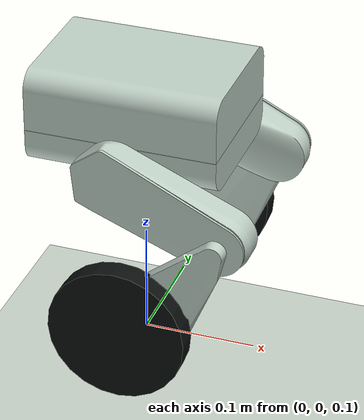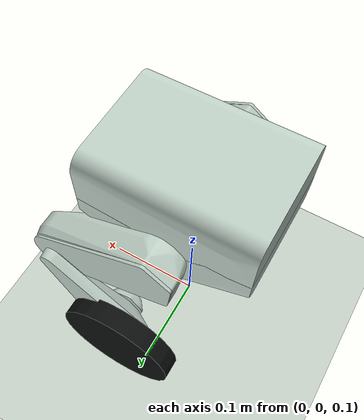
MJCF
<mujoco model="clanky_v2_drivetrain_cad_armature"><compiler angle="radian" autolimits="true" inertiafromgeom="false" /><option timestep="0.00025" integrator="RK4" iterations="100" tolerance="1e-10" gravity="0 0 -9.81"><flag energy="enable" /></option><default><joint damping=".0001" frictionloss=".001" /><geom friction="0.8 0.002 0.0001" solref="0.003 1" solimp=".95 .99 .001" contype="2" conaffinity="1" mass="0" /></default><asset><mesh name="D435i_native_front_face_outer" vertex="0.07755 -0.032 0.0216 0.07815 -0.032 0.0216 0.07755 0.042 0.0216 0.07815 0.042 0.0216 0.07815 0.0425903677 0.02162209 0.07815 0.0443285659 0.0219509748 0.07815 0.0448861941 0.0221460974 0.07815 0.04595 0.0226583993 0.07815 0.0464502285 0.0229727137 0.07815 0.0469255694 0.0233235313 0.07815 0.0473733646 0.0237088902 0.07815 0.0477911098 0.0241266354 0.07815 0.0495490252 0.0271714341 0.07815 0.0497019305 0.0277420846 0.07815 0.0498117635 0.0283225661 0.07815 0.04987791 0.0289096323 0.07815 0.0499 0.0295 0.07755 0.0425903677 0.02162209 0.07755 0.0431774339 0.0216882365 0.07755 0.0437579154 0.0217980695 0.07755 0.0448861941 0.0221460974 0.07755 0.0454276815 0.0223823459 0.07755 0.04595 0.0226583993 0.07755 0.0464502285 0.0229727137 0.07755 0.0473733646 0.0237088902 0.07755 0.0477911098 0.0241266354 0.07755 0.0481764687 0.0245744306 0.07755 0.0485272863 0.0250497715 0.07755 0.0491176541 0.0260723185 0.07755 0.0493539026 0.0266138059 0.07755 0.04987791 0.0289096323 0.07755 0.0499 0.0295 0.07755 0.0499 0.0385 0.07815 0.0499 0.0385 0.07815 0.04987791 0.0390903677 0.07815 0.0495490252 0.0408285659 0.07815 0.0493539026 0.0413861941 0.07815 0.0491176541 0.0419276815 0.07815 0.0488416007 0.04245 0.07815 0.0485272863 0.0429502285 0.07815 0.0477911098 0.0438733646 0.07815 0.0473733646 0.0442911098 0.07815 0.0464502285 0.0450272863 0.07815 0.04595 0.0453416007 0.07815 0.0454276815 0.0456176541 0.07815 0.0448861941 0.0458539026 0.07815 0.0437579154 0.0462019305 0.07815 0.0431774339 0.0463117635 0.07815 0.0425903677 0.04637791 0.07815 0.042 0.0464 0.07755 0.0497019305 0.0402579154 0.07755 0.0495490252 0.0408285659 0.07755 0.0491176541 0.0419276815 0.07755 0.0481764687 0.0434255694 0.07755 0.0477911098 0.0438733646 0.07755 0.0473733646 0.0442911098 0.07755 0.0464502285 0.0450272863 0.07755 0.0448861941 0.0458539026 0.07755 0.0443285659 0.0460490252 0.07755 0.0425903677 0.04637791 0.07755 0.042 0.0464 0.07755 -0.032 0.0464 0.07815 -0.032 0.0464 0.07815 -0.0325903677 0.04637791 0.07815 -0.0331774339 0.0463117635 0.07815 -0.0337579154 0.0462019305 0.07815 -0.0343285659 0.0460490252 0.07815 -0.0348861941 0.0458539026 0.07815 -0.0354276815 0.0456176541 0.07815 -0.03595 0.0453416007 0.07815 -0.0364502285 0.0450272863 0.07815 -0.0369255694 0.0446764687 0.07815 -0.0373733646 0.0442911098 0.07815 -0.0377911098 0.0438733646 0.07815 -0.0381764687 0.0434255694 0.07815 -0.0385272863 0.0429502285 0.07815 -0.0388416007 0.04245 0.07815 -0.0391176541 0.0419276815 0.07815 -0.0393539026 0.0413861941 0.07815 -0.0395490252 0.0408285659 0.07815 -0.0397019305 0.0402579154 0.07815 -0.0398117635 0.0396774339 0.07815 -0.03987791 0.0390903677 0.07815 -0.0399 0.0385 0.07755 -0.0399 0.0385 0.07755 -0.0337579154 0.0462019305 0.07755 -0.0343285659 0.0460490252 0.07755 -0.0348861941 0.0458539026 0.07755 -0.0354276815 0.0456176541 0.07755 -0.0364502285 0.0450272863 0.07755 -0.0377911098 0.0438733646 0.07755 -0.0381764687 0.0434255694 0.07755 -0.0388416007 0.04245 0.07755 -0.0391176541 0.0419276815 0.07755 -0.0397019305 0.0402579154 0.07755 -0.0398117635 0.0396774339 0.07755 -0.03987791 0.0390903677 0.07755 -0.0399 0.0295 0.07815 -0.0399 0.0295 0.07815 -0.03987791 0.0289096323 0.07815 -0.0395490252 0.0271714341 0.07815 -0.0393539026 0.0266138059 0.07815 -0.0391176541 0.0260723185 0.07815 -0.0388416007 0.02555 0.07815 -0.0381764687 0.0245744306 0.07815 -0.0377911098 0.0241266354 0.07815 -0.0373733646 0.0237088902 0.07815 -0.0364502285 0.0229727137 0.07815 -0.03595 0.0226583993 0.07815 -0.0354276815 0.0223823459 0.07815 -0.0348861941 0.0221460974 0.07815 -0.0343285659 0.0219509748 0.07815 -0.0337579154 0.0217980695 0.07815 -0.0331774339 0.0216882365 0.07815 -0.0325903677 0.02162209 0.07755 -0.0398117635 0.0283225661 0.07755 -0.0395490252 0.0271714341 0.07755 -0.0393539026 0.0266138059 0.07755 -0.0391176541 0.0260723185 0.07755 -0.0381764687 0.0245744306 0.07755 -0.0377911098 0.0241266354 0.07755 -0.0369255694 0.0233235313 0.07755 -0.03595 0.0226583993 0.07755 -0.0325903677 0.02162209 0.07755 0.0443285659 0.0219509748 0.07755 0.0469255694 0.0233235313 0.07755 0.0488416007 0.02555 0.07755 0.0495490252 0.0271714341 0.07755 0.0497019305 0.0277420846 0.07755 0.0498117635 0.0283225661 0.07755 0.04987791 0.0390903677 0.07755 0.0498117635 0.0396774339 0.07755 0.0493539026 0.0413861941 0.07755 0.0488416007 0.04245 0.07755 0.0485272863 0.0429502285 0.07755 0.0469255694 0.0446764687 0.07755 0.04595 0.0453416007 0.07755 0.0454276815 0.0456176541 0.07755 0.0437579154 0.0462019305 0.07755 0.0431774339 0.0463117635 0.07755 -0.0325903677 0.04637791 0.07755 -0.0331774339 0.0463117635 0.07755 -0.03595 0.0453416007 0.07755 -0.0369255694 0.0446764687 0.07755 -0.0373733646 0.0442911098 0.07755 -0.0385272863 0.0429502285 0.07755 -0.0393539026 0.0413861941 0.07755 -0.0395490252 0.0408285659 0.07755 -0.03987791 0.0289096323 0.07755 -0.0397019305 0.0277420846 0.07755 -0.0388416007 0.02555 0.07755 -0.0385272863 0.0250497715 0.07755 -0.0373733646 0.0237088902 0.07755 -0.0364502285 0.0229727137 0.07755 -0.0354276815 0.0223823459 0.07755 -0.0348861941 0.0221460974 0.07755 -0.0343285659 0.0219509748 0.07755 -0.0337579154 0.0217980695 0.07755 -0.0331774339 0.0216882365 0.07815 0.0431774339 0.0216882365 0.07815 0.0437579154 0.0217980695 0.07815 0.0454276815 0.0223823459 0.07815 0.0481764687 0.0245744306 0.07815 0.0485272863 0.0250497715 0.07815 0.0488416007 0.02555 0.07815 0.0491176541 0.0260723185 0.07815 0.0493539026 0.0266138059 0.07815 0.0498117635 0.0396774339 0.07815 0.0497019305 0.0402579154 0.07815 0.0481764687 0.0434255694 0.07815 0.0469255694 0.0446764687 0.07815 0.0443285659 0.0460490252 0.07815 -0.0398117635 0.0283225661 0.07815 -0.0397019305 0.0277420846 0.07815 -0.0385272863 0.0250497715 0.07815 -0.0369255694 0.0233235313" /><mesh name="left_drive_encoder_service_cap_outer" vertex="0.1128322389 0.0635 0.044 0.1138784603 0.0635 0.0439608532 0.1149188307 0.0635 0.0438436316 0.1169588114 0.0635 0.0433780193 0.1179470133 0.0635 0.0430322325 0.1189066113 0.0635 0.0426135642 0.1198322389 0.0635 0.0421243557 0.1215610962 0.0635 0.0409456408 0.1223546573 0.0635 0.0402627262 0.1230949651 0.0635 0.0395224183 0.1258644714 0.0635 0.0351147743 0.1262102582 0.0635 0.0341265724 0.1264812297 0.0635 0.0331152931 0.1267930921 0.0635 0.0310462213 0.1268322389 0.0635 0.03 0.1267930921 0.0635 0.0289537787 0.1266758705 0.0635 0.0279134083 0.1264812297 0.0635 0.0268847069 0.1262102582 0.0635 0.0258734276 0.1258644714 0.0635 0.0248852257 0.1254458031 0.0635 0.0239256277 0.1249565946 0.0635 0.023 0.1243995818 0.0635 0.0221135192 0.1237778797 0.0635 0.0212711428 0.1215610962 0.0635 0.0190543592 0.1198322389 0.0635 0.0178756443 0.1169588114 0.0635 0.0166219807 0.115947532 0.0635 0.0163510092 0.1138784603 0.0635 0.0160391468 0.1128322389 0.0635 0.016 0.1107456472 0.0635 0.0161563684 0.1097169459 0.0635 0.0163510092 0.1087056665 0.0635 0.0166219807 0.1077174646 0.0635 0.0169677675 0.1067578666 0.0635 0.0173864358 0.1041033817 0.0635 0.0190543592 0.1025695127 0.0635 0.0204775817 0.1018865982 0.0635 0.0212711428 0.1012648961 0.0635 0.0221135192 0.1007078833 0.0635 0.023 0.1002186748 0.0635 0.0239256277 0.0998000065 0.0635 0.0248852257 0.0988713858 0.0635 0.0289537787 0.0988322389 0.0635 0.03 0.0989886074 0.0635 0.0320865917 0.1007078833 0.0635 0.037 0.1012648961 0.0635 0.0378864808 0.1018865982 0.0635 0.0387288572 0.1025695127 0.0635 0.0395224183 0.1033098206 0.0635 0.0402627262 0.1049457581 0.0635 0.0415673428 0.1067578666 0.0635 0.0426135642 0.1077174646 0.0635 0.0430322325 0.1107456472 0.0635 0.0438436316 0.0942698032 0.072 0.021300231 0.0928224922 0.072 0.0255435402 0.0925506145 0.072 0.0270157564 0.0923869057 0.072 0.0285038885 0.0923322389 0.072 0.03 0.0923869057 0.072 0.0314961115 0.0925506145 0.072 0.0329842436 0.0928224922 0.072 0.0344564598 0.0936843849 0.072 0.0373218636 0.1296476778 0.072 0.0182743436 0.125557482 0.072 0.0139277198 0.1243505761 0.072 0.0130418778 0.1203886204 0.072 0.0109434762 0.1175340136 0.072 0.0100464711 0.1160652461 0.072 0.0097565402 0.1145792358 0.072 0.0095745746 0.1130839083 0.072 0.0095015449 0.1143409003 0.072 0.050444411 0.118785331 0.072 0.0496165923 0.1202128368 0.072 0.0491252915 0.1216003153 0.072 0.0485302681 0.1229402417 0.072 0.0478347492 0.1242253492 0.072 0.0470425068 0.1254486683 0.072 0.0461578375 0.1266035644 0.072 0.045185539 0.1286834395 0.072 0.0429995938 0.1295971387 0.072 0.0417978022 0.1304199165 0.072 0.0405320273 0.115947532 0.0635 0.0436489908 0.1207187198 0.0635 0.0415673428 0.1237778797 0.0635 0.0387288572 0.1243995818 0.0635 0.0378864808 0.1249565946 0.0635 0.037 0.1254458031 0.0635 0.0360743723 0.1266758705 0.0635 0.0320865917 0.1230949651 0.0635 0.0204775817 0.1223546573 0.0635 0.0197372738 0.1207187198 0.0635 0.0184326572 0.1189066113 0.0635 0.0173864358 0.1179470133 0.0635 0.0169677675 0.1149188307 0.0635 0.0161563684 0.1117860176 0.0635 0.0160391468 0.1058322389 0.0635 0.0178756443 0.1049457581 0.0635 0.0184326572 0.1033098206 0.0635 0.0197372738 0.0994542197 0.0635 0.0258734276 0.0991832482 0.0635 0.0268847069 0.0989886074 0.0635 0.0279134083 0.0988713858 0.0635 0.0310462213 0.0991832482 0.0635 0.0331152931 0.0994542197 0.0635 0.0341265724 0.0998000065 0.0635 0.0351147743 0.1002186748 0.0635 0.0360743723 0.1041033817 0.0635 0.0409456408 0.1058322389 0.0635 0.0421243557 0.1087056665 0.0635 0.0433780193 0.1097169459 0.0635 0.0436489908 0.1117860176 0.0635 0.0439608532 0.1296459536 0.0745 0.0417281286 0.1277602374 0.0745 0.044050084 0.1266954096 0.0745 0.0451017383 0.1243501605 0.0745 0.0469584045 0.1230822389 0.0745 0.0477535208 0.1217596872 0.0745 0.0484540149 0.1189791426 0.0745 0.0495567271 0.1175359694 0.0745 0.0499530679 0.1160677264 0.0745 0.0502430635 0.1128322389 0.072 0.0505 0.1158413798 0.072 0.0502779454 0.1173255397 0.072 0.0500015062 0.1276837743 0.072 0.0441308846 0.0949542214 0.072 0.0199687245 0.0936843849 0.072 0.0226781364 0.0932010887 0.072 0.0240950919 0.0932010887 0.072 0.0359049081 0.0942698032 0.072 0.038699769 0.0949542214 0.072 0.0400312755 0.0942685243 0.0745 0.0213029603 0.093683488 0.0745 0.0226804825 0.09320051 0.0745 0.0240970161 0.0928221646 0.0745 0.0255450112 0.0925504683 0.0745 0.0270167504 0.0923868691 0.0745 0.0285043896 0.0923322389 0.0745 0.03 0.0928221646 0.0745 0.0344549888 0.093683488 0.0745 0.0373195175 0.1304585872 0.072 0.0195328204 0.1287470858 0.072 0.0170784038 0.1277616145 0.072 0.0159513793 0.1266965197 0.072 0.0148992809 0.1230822389 0.072 0.0122464792 0.121759235 0.072 0.0115457663 0.1189777049 0.072 0.0104428211 0.1296459536 0.0745 0.0182718714 0.1287455025 0.0745 0.0170764539 0.1277602374 0.0745 0.015949916 0.1266954096 0.0745 0.0148982617 0.1243501605 0.0745 0.0130415955 0.1230822389 0.0745 0.0122464792 0.1203895543 0.0745 0.0109438465 0.1145822389 0.0745 0.0095748317 0.1287455025 0.0745 0.0429235461 0.1255566942 0.0745 0.0460729038 0.1203895543 0.0745 0.0490561535 0.1145822389 0.0745 0.0504251683 0.1363122471 0.0745 0.0318356337 0.1364391792 0.0745 0.0316114968 0.1365492834 0.0745 0.0313786316 0.1366419632 0.0745 0.0311382994 0.136773139 0.0745 0.030640474 0.1368109245 0.0745 0.0303856773 0.1368298685 0.0745 0.0301287916 0.1368298685 0.0745 0.0298712084 0.1368109245 0.0745 0.0296143227 0.1367167167 0.0745 0.0291081982 0.1366419632 0.0745 0.0288617006 0.1365492834 0.0745 0.0286213684 0.1363122471 0.0745 0.0281643663 0.1361691745 0.0745 0.0279501716 0.1255566942 0.0745 0.0139270962 0.1217596872 0.0745 0.0115459851 0.1189791426 0.0745 0.0104432729 0.1175359694 0.0745 0.0100469321 0.1160677264 0.0745 0.0097569365 0.1029389746 0.0745 0.0087647067 0.1026819403 0.0745 0.0087478996 0.1021676467 0.0745 0.0087711212 0.1016623231 0.0745 0.0088695346 0.1014164557 0.0745 0.0089463354 0.1007218873 0.0745 0.009281839 0.1005088898 0.0745 0.0094266878 0.1003071221 0.0745 0.0095868094 0.0997797867 0.0745 0.0101497528 0.0995025294 0.0745 0.0105835333 0.0923868691 0.0745 0.0314956104 0.0925504683 0.0745 0.0329832496 0.09320051 0.0745 0.0359029839 0.0942685243 0.0745 0.0386970397 0.0995025294 0.0745 0.0494164667 0.0996331716 0.0745 0.0496384616 0.0997797867 0.0745 0.0498502472 0.0999415806 0.0745 0.0500506764 0.100117677 0.0745 0.0502386636 0.1003071221 0.0745 0.0504131906 0.1005088898 0.0745 0.0505733122 0.1007218873 0.0745 0.050718161 0.1011769025 0.0745 0.0509589895 0.1016623231 0.0745 0.0511304654 0.101913173 0.0745 0.0511889757 0.102424366 0.0745 0.0512499584 0.1026819403 0.0745 0.0512521004 0.1029389746 0.0745 0.0512352933 0.0995025294 0.0725 0.0494164667 0.0996331716 0.0725 0.0496384616 0.0997797867 0.0725 0.0498502472 0.100117677 0.0725 0.0502386636 0.100944961 0.0725 0.0508469527 0.1011769025 0.0725 0.0509589895 0.1014164557 0.0725 0.0510536646 0.1016623231 0.0725 0.0511304654 0.101913173 0.0725 0.0511889757 0.1021676467 0.0725 0.0512288788 0.102424366 0.0725 0.0512499584 0.1026819403 0.0725 0.0512521004 0.1029389746 0.0725 0.0512352933 0.0993885677 0.0745 0.0491854648 0.100944961 0.0745 0.0508469527 0.1014164557 0.0745 0.0510536646 0.1021676467 0.0745 0.0512288788 0.0993885677 0.0725 0.0491854648 0.0999415806 0.0725 0.0500506764 0.1003071221 0.0725 0.0504131906 0.1005088898 0.0725 0.0505733122 0.1007218873 0.0725 0.050718161 0.1361691745 0.0725 0.0320498284 0.1363122471 0.0725 0.0318356337 0.1366419632 0.0725 0.0311382994 0.1368109245 0.0725 0.0303856773 0.1368298685 0.0725 0.0301287916 0.1368109245 0.0725 0.0296143227 0.1361691745 0.0725 0.0279501716 0.1364391792 0.0725 0.0316114968 0.1365492834 0.0725 0.0313786316 0.1367167167 0.0725 0.0308918018 0.136773139 0.0725 0.030640474 0.1368298685 0.0725 0.0298712084 0.136773139 0.0725 0.029359526 0.1367167167 0.0725 0.0291081982 0.1366419632 0.0725 0.0288617006 0.1365492834 0.0725 0.0286213684 0.1364391792 0.0725 0.0283885032 0.1363122471 0.0725 0.0281643663 0.1361691745 0.0745 0.0320498284 0.1367167167 0.0745 0.0308918018 0.136773139 0.0745 0.029359526 0.1364391792 0.0745 0.0283885032 0.1029389746 0.0725 0.0087647067 0.1026819403 0.0725 0.0087478996 0.102424366 0.0725 0.0087500416 0.1021676467 0.0725 0.0087711212 0.101913173 0.0725 0.0088110243 0.1016623231 0.0725 0.0088695346 0.1014164557 0.0725 0.0089463354 0.1011769025 0.0725 0.0090410105 0.1005088898 0.0725 0.0094266878 0.0999415806 0.0725 0.0099493236 0.0997797867 0.0725 0.0101497528 0.0996331716 0.0725 0.0103615384 0.0995025294 0.0725 0.0105835333 0.102424366 0.0745 0.0087500416 0.101913173 0.0745 0.0088110243 0.1011769025 0.0745 0.0090410105 0.100944961 0.0745 0.0091530473 0.100117677 0.0745 0.0097613364 0.0999415806 0.0745 0.0099493236 0.0996331716 0.0745 0.0103615384 0.0993885677 0.0745 0.0108145352 0.100944961 0.0725 0.0091530473 0.1007218873 0.0725 0.009281839 0.1003071221 0.0725 0.0095868094 0.100117677 0.0725 0.0097613364 0.0993885677 0.0725 0.0108145352" /><mesh name="left_drive_shin_case_outer" vertex="0.1083654305 0.1 -0.0276414114 0.1406517652 0.0977 0.0031739504 0.1408160858 0.0977 -0.0009509546 0.1406698445 0.0977 -0.0030112648 0.1399245334 0.0977 -0.0070716039 0.1377109456 0.0977 -0.0128471769 0.1366961939 0.0977 -0.0146462164 0.1355515825 0.0977 -0.0163655562 0.13428334 0.0977 -0.0179958401 0.1263505581 0.0977 -0.0245205026 0.1245061884 0.0977 -0.0254503223 0.1225982929 0.0977 -0.0262416499 0.1206372539 0.0977 -0.0268901793 0.1186337425 0.0977 -0.0273923813 0.1165986614 0.0977 -0.0277455233 0.1145430846 0.0977 -0.0279476834 0.1341103968 0.11 0.0182 0.1398956276 0.11 0.0071814338 0.1403561142 0.11 0.0051416234 0.1406630823 0.11 0.0030731347 0.1408104804 0.11 -0.0011036322 0.140334538 0.11 -0.0052558108 0.1384788021 0.11 -0.0112362715 0.137568698 0.11 -0.0131189784 0.1365206226 0.11 -0.0149285122 0.1353404219 0.11 -0.0166547801 0.1326106753 0.11 -0.0198195221 0.131076355 0.11 -0.0212403444 0.1294402755 0.11 -0.0225426955 0.1277115622 0.11 -0.0237193115 0.124015266 0.11 -0.0256698248 0.1200698177 0.11 -0.0270484279 0.1180309672 0.11 -0.0275131464 0.1138778099 0.11 -0.0279804714 0.111786668 0.11 -0.0279804714 0.1097013578 0.11 -0.0278244063 0.1076335107 0.11 -0.0275131464 0.1055946602 0.11 -0.0270484279 0.1035961783 0.11 -0.0264328429 0.1016492119 0.11 -0.0256698248 0.0997646205 0.11 -0.0247636295 0.0979529156 0.11 -0.0237193115 0.0916297995 0.11 -0.0182881535 0.090324056 0.11 -0.0166547801 0.0891438552 0.11 -0.0149285122 0.0880957799 0.11 -0.0131189784 0.0864186191 0.11 -0.0092908927 0.0857988883 0.11 -0.0072936926 0.084849658 0.11 0.0009875052 0.0850013956 0.11 0.0030731347 0.0857688502 0.11 0.0071814338 0.0890821018 0.11 0.0148300703 0.0902551279 0.11 0.0165612215 0.0915540811 0.11 0.0182 0.1083654305 0.0977 -0.0276414114 -0.0015952887 0.0977 -0.0098719326 -0.0023231254 0.0977 -0.0097264119 -0.0030381635 0.0977 -0.0095273061 -0.0037364637 0.0977 -0.0092757123 -0.0044141788 0.0977 -0.0089730165 -0.0050675753 0.0977 -0.0086208863 -0.0056930533 0.0977 -0.0082212617 -0.0068466433 0.0977 -0.0072885853 -0.0078495622 0.0977 -0.0061955123 -0.0082874796 0.0977 -0.0055962203 -0.0086797394 0.0977 -0.0049660974 -0.0090241806 0.0977 -0.0043086152 -0.0093189055 0.0977 -0.0036273959 -0.0095622904 0.0977 -0.0029261924 -0.0097529946 0.0977 -0.0022088678 -0.01 0.0977 0 -0.0099724539 0.0977 0.0007417303 -0.0098899672 0.0977 0.0014793742 -0.0097529946 0.0977 0.0022088678 -0.0095622904 0.0977 0.0029261924 -0.0073683998 0.0977 0.0067606719 -0.0068466433 0.0977 0.0072885853 -0.006287167 0.0977 0.0077763443 -0.0056930533 0.0977 0.0082212617 -0.0050675753 0.0977 0.0086208863 -0.0044141788 0.0977 0.0089730165 0.1408100484 0.0977 0.0011145303 0.1403721203 0.0977 -0.0050551887 0.1393295193 0.0977 -0.0090495379 0.1385903158 0.0977 -0.0109782273 0.1328983679 0.0977 -0.0195281967 0.1314042027 0.0977 -0.0209542875 0.1298089751 0.0977 -0.022266352 0.1281213657 0.0977 -0.0234572505 0.112478198 0.0977 -0.0279977616 0.110415238 0.0977 -0.0278954854 0.1128322389 0.1 0.0505 0.1158678918 0.1 0.0502739935 0.1173647608 0.1 0.0499926548 0.1188366103 0.1 0.0496009572 0.1230217556 0.1 0.0477883038 0.1243143294 0.1 0.0469826853 0.1255435223 0.1 0.0460833229 0.1267025494 0.1 0.045095181 0.1287849371 0.1 0.0428748367 0.1296968031 0.1 0.0416548906 0.1305155772 0.1 0.0403706098 0.1312367398 0.1 0.0390290835 0.1143412444 0.077 0.0504443856 0.1173265496 0.077 0.0500012792 0.1229423429 0.077 0.0478335582 0.1295997197 0.077 0.0417941337 0.1266954096 0.077 0.0148982617 0.1255566942 0.077 0.0139270962 0.1217596872 0.077 0.0115459851 0.1203895543 0.077 0.0109438465 0.1175359694 0.077 0.0100469321 0.1160677264 0.077 0.0097569365 0.1145822389 0.077 0.0095748317 0.0941707606 0.077 0.0215147642 0.093588004 0.077 0.02293534 0.0931132093 0.077 0.0243955492 0.0924975395 0.077 0.0274019238 0.0924975395 0.077 0.0325980762 0.0927490401 0.077 0.0341128001 0.0931132093 0.077 0.0356044508 0.093588004 0.077 0.03706466 0.0941707606 0.077 0.0384852358 0.1069783562 0.1 0.0496464261 0.1084147795 0.1 0.0500183928 0.1098743456 0.1 0.0502854842 0.1113494081 0.1 0.0504463007 0.1192916797 0.11 0.035525 0.1063727982 0.11 0.035525 0.1067865978 0.11 0.0359749664 0.1077057049 0.11 0.0367800183 0.108730739 0.11 0.037444978 0.1092764338 0.11 0.0377205084 0.1104200811 0.11 0.0381505518 0.1116135696 0.11 0.0384121843 0.1122213244 0.11 0.0384780177 0.1128322389 0.11 0.0385 0.1134431535 0.11 0.0384780177 0.1140509082 0.11 0.0384121843 0.1152443968 0.11 0.0381505518 0.1158239575 0.11 0.0379561058 0.1163880441 0.11 0.0377205084 0.1169337389 0.11 0.037444978 0.1174582195 0.11 0.0371309399 0.117958773 0.11 0.0367800183 0.1184328105 0.11 0.0363940283 0.1188778801 0.11 0.0359749664 0.13540935 0.11 0.0165612215 0.1365823761 0.11 0.0148300703 0.1376229324 0.11 0.0130162022 0.1385252149 0.11 0.0111297344 0.1392841911 0.11 0.0091811888 0.1408148198 0.11 0.0009875052 0.1406500883 0.11 -0.003188614 0.1398655896 0.11 -0.0072936926 0.1392458588 0.11 -0.0092908927 0.1340346784 0.11 -0.0182881535 0.1258998574 0.11 -0.0247636295 0.1220682996 0.11 -0.0264328429 0.11596312 0.11 -0.0278244063 0.0962242024 0.11 -0.0225426955 0.0945881229 0.11 -0.0212403444 0.0930538026 0.11 -0.0198195221 0.0871856758 0.11 -0.0112362715 0.0853299399 0.11 -0.0052558108 0.0850143896 0.11 -0.003188614 0.0848539975 0.11 -0.0011036322 0.0853083637 0.11 0.0051416234 0.0863802868 0.11 0.0091811888 0.087139263 0.11 0.0111297344 0.0880415455 0.11 0.0130162022 -0.0015952887 0.1 -0.0098719326 -0.0023231254 0.1 -0.0097264119 -0.0050675753 0.1 -0.0086208863 -0.0056930533 0.1 -0.0082212617 -0.0068466433 0.1 -0.0072885853 -0.0073683998 0.1 -0.0067606719 -0.0078495622 0.1 -0.0061955123 -0.0093189055 0.1 -0.0036273959 -0.0098899672 0.1 -0.0014793742 -0.0099724539 0.1 -0.0007417303 -0.0093189055 0.1 0.0036273959 -0.0086797394 0.1 0.0049660974 -0.0082874796 0.1 0.0055962203 -0.0078495622 0.1 0.0061955123 -0.0068466433 0.1 0.0072885853 -0.0056930533 0.1 0.0082212617 -0.0050675753 0.1 0.0086208863 0.1143542662 0.1 0.0504434203 0.1202753159 0.1 0.0491010629 0.121672936 0.1 0.0484957313 0.1277850127 0.1 0.0440237141 0.13185631 0.1 0.037637717 0.1323708679 0.1 0.0362041905 -0.0030381635 0.1 -0.0095273061 -0.0037364637 0.1 -0.0092757123 -0.0044141788 0.1 -0.0089730165 -0.006287167 0.1 -0.0077763443 -0.0082874796 0.1 -0.0055962203 -0.0086797394 0.1 -0.0049660974 -0.0090241806 0.1 -0.0043086152 -0.0095622904 0.1 -0.0029261924 -0.0097529946 0.1 -0.0022088678 -0.01 0.1 0 -0.0099724539 0.1 0.0007417303 -0.0098899672 0.1 0.0014793742 -0.0097529946 0.1 0.0022088678 -0.0095622904 0.1 0.0029261924 -0.0090241806 0.1 0.0043086152 -0.0073683998 0.1 0.0067606719 -0.006287167 0.1 0.0077763443 -0.006287167 0.0977 -0.0077763443 -0.0073683998 0.0977 -0.0067606719 -0.0098899672 0.0977 -0.0014793742 -0.0099724539 0.0977 -0.0007417303 -0.0093189055 0.0977 0.0036273959 -0.0090241806 0.0977 0.0043086152 -0.0086797394 0.0977 0.0049660974 -0.0082874796 0.0977 0.0055962203 -0.0078495622 0.0977 0.0061955123 0.1029389746 0.077 0.0512352933 0.1026819403 0.077 0.0512521004 0.1016623231 0.077 0.0511304654 0.100944961 0.077 0.0508469527 0.100117677 0.077 0.0502386636 0.0997797867 0.077 0.0498502472 0.0996331716 0.077 0.0496384616 0.0993885677 0.077 0.0491854648 0.1158420624 0.077 0.0502778441 0.1187866517 0.077 0.0496161915 0.1202144463 0.077 0.0491246703 0.1216021865 0.077 0.0485293826 0.1242276438 0.077 0.0470409726 0.1254511157 0.077 0.0461559262 0.1266061201 0.077 0.045183221 0.1276863902 0.077 0.0441281347 0.1286860647 0.077 0.0429963921 0.1363269907 0.077 0.0318114806 0.1364516789 0.077 0.0315871655 0.1365595949 0.077 0.0313543167 0.1366501584 0.077 0.0311141862 0.136777376 0.077 0.0306172765 0.1368305996 0.077 0.0301071091 0.1368290434 0.077 0.0298504732 0.1367696368 0.077 0.0293409888 0.1367121058 0.077 0.0290908797 0.1366364023 0.077 0.0288456585 0.1364322016 0.077 0.028375121 0.1363048022 0.077 0.0281523346 0.1361614203 0.077 0.0279394824 0.1296459536 0.077 0.0182718714 0.1287455025 0.077 0.0170764539 0.1277602374 0.077 0.015949916 0.1243501605 0.077 0.0130415955 0.1230822389 0.077 0.0122464792 0.1189791426 0.077 0.0104432729 0.1029389746 0.077 0.0087647067 0.1026819403 0.077 0.0087478996 0.102424366 0.077 0.0087500416 0.1021676467 0.077 0.0087711212 0.101913173 0.077 0.0088110243 0.100944961 0.077 0.0091530473 0.0996331716 0.077 0.0103615384 0.0993885677 0.077 0.0108145352 0.0927490401 0.077 0.0258871999 0.1029389746 0.083 0.0512352933 0.1026819403 0.083 0.0512521004 0.102424366 0.083 0.0512499584 0.1021676467 0.083 0.0512288788 0.102424366 0.077 0.0512499584 0.1021676467 0.077 0.0512288788 0.101913173 0.077 0.0511889757 0.1014164557 0.077 0.0510536646 0.1011769025 0.077 0.0509589895 0.1007218873 0.077 0.050718161 0.1005088898 0.077 0.0505733122 0.1003071221 0.077 0.0504131906 0.0999415806 0.077 0.0500506764 0.0995025294 0.077 0.0494164667 0.102521671 0.0795 0.0512529967 0.1020178502 0.0795 0.0512077161 0.1017697101 0.0795 0.0511578999 0.1015258187 0.0795 0.0510902821 0.1015258187 0.0811 0.0510902821 0.1017697101 0.0811 0.0511578999 0.1020178502 0.0811 0.0512077161 0.1022689415 0.0811 0.0512394704 0.1027747172 0.0811 0.0512482242 0.101913173 0.083 0.0511889757 0.1016623231 0.083 0.0511304654 0.1014164557 0.083 0.0510536646 0.1016623231 0.077 0.0088695346 0.1014164557 0.077 0.0089463354 0.1011769025 0.077 0.0090410105 0.1007218873 0.077 0.009281839 0.1005088898 0.077 0.0094266878 0.1003071221 0.077 0.0095868094 0.100117677 0.077 0.0097613364 0.0999415806 0.077 0.0099493236 0.0997797867 0.077 0.0101497528 0.0995025294 0.077 0.0105835333 0.1361862007 0.083 0.0320260559 0.1365595949 0.083 0.0313543167 0.1366501584 0.083 0.0311141862 0.1361862007 0.077 0.0320260559 0.1367228824 0.077 0.030868065 0.1368133463 0.077 0.0303631692 0.136808686 0.077 0.0295946413 0.1365429334 0.077 0.028606644 0.1362625018 0.0795 0.0319140428 0.1365078086 0.0795 0.0314716513 0.1362625018 0.0811 0.0319140428 0.1363931579 0.0811 0.0316972846 0.1365078086 0.0811 0.0314716513 0.1366058542 0.0811 0.0312383227 0.1366867821 0.0811 0.0309985189 0.1367501691 0.0811 0.0307534939 0.1367956838 0.0811 0.0305045289 0.1363269907 0.083 0.0318114806 0.1364516789 0.083 0.0315871655 0.1367228824 0.083 0.030868065 0.136777376 0.083 0.0306172765 0.1072316674 0.11 0.0363940283 0.1082062584 0.11 0.0371309399 0.1098405204 0.11 0.0379561058 0.1110121183 0.11 0.0383028405 0.1146523596 0.11 0.0383028405 0.014 0.1055 0.0195 0.014 0.099 0.0195 -0.0020026884 0.1085 -0.0087743512 -0.0026527966 0.1085 -0.0086001553 -0.0032880692 0.1085 -0.0083778637 -0.0039049537 0.1085 -0.0081087198 -0.0045 0.1085 -0.0077942286 -0.0061215546 0.1085 -0.0065974668 -0.0065974668 0.1085 -0.0061215546 -0.0070364833 0.1085 -0.0056114082 -0.007436149 0.1085 -0.0050698805 -0.0077942286 0.1085 -0.0045 -0.0081087198 0.1085 -0.0039049537 -0.0086001553 0.1085 -0.0026527966 -0.0087743512 0.1085 -0.0020026884 -0.0088994774 0.1085 -0.0013413804 -0.0089748342 0.1085 -0.0006725708 -0.0089748342 0.1085 0.0006725708 -0.0081087198 0.1085 0.0039049537 -0.0077942286 0.1085 0.0045 -0.007436149 0.1085 0.0050698805 -0.0065974668 0.1085 0.0061215546 -0.0050698805 0.1085 0.007436149 -0.0045 0.1085 0.0077942286 -0.0039049537 0.1085 0.0081087198 -0.0032880692 0.1085 0.0083778637 -0.0013413804 0.1085 -0.0088994774 -0.0050698805 0.1085 -0.007436149 -0.0056114082 0.1085 -0.0070364833 -0.0083778637 0.1085 -0.0032880692 -0.009 0.1085 -0 -0.0088994774 0.1085 0.0013413804 -0.0087743512 0.1085 0.0020026884 -0.0086001553 0.1085 0.0026527966 -0.0083778637 0.1085 0.0032880692 -0.0070364833 0.1085 0.0056114082 -0.0061215546 0.1085 0.0065974668 -0.0056114082 0.1085 0.0070364833 -0.0026527966 0.1085 0.0086001553 0.1027747172 0.0795 0.0512482242 0.1022689415 0.0795 0.0512394704 0.102521671 0.0811 0.0512529967 0.1363931579 0.0795 0.0316972846 0.1366058542 0.0795 0.0312383227 0.1366867821 0.0795 0.0309985189 0.1367501691 0.0795 0.0307534939 0.1367956838 0.0795 0.0305045289" /><mesh name="left_drive_bearing_service_lid_outer" vertex="0.0915540811 0.11 0.0182 0.1341103968 0.11 0.0182 0.13540935 0.112 0.0165612215 0.1376229324 0.112 0.0130162022 0.1398956276 0.112 0.0071814338 0.1403561142 0.112 0.0051416234 0.1408148198 0.112 0.0009875052 0.1406500883 0.112 -0.003188614 0.1398655896 0.112 -0.0072936926 0.1392458588 0.112 -0.0092908927 0.1365206226 0.112 -0.0149285122 0.1353404219 0.112 -0.0166547801 0.131076355 0.112 -0.0212403444 0.1277115622 0.112 -0.0237193115 0.124015266 0.112 -0.0256698248 0.1180309672 0.112 -0.0275131464 0.11596312 0.112 -0.0278244063 0.1138778099 0.112 -0.0279804714 0.1097013578 0.112 -0.0278244063 0.1076335107 0.112 -0.0275131464 0.1055946602 0.112 -0.0270484279 0.1016492119 0.112 -0.0256698248 0.090324056 0.112 -0.0166547801 0.0871856758 0.112 -0.0112362715 0.0864186191 0.112 -0.0092908927 0.0850143896 0.112 -0.003188614 0.0848539975 0.112 -0.0011036322 0.084849658 0.112 0.0009875052 0.0850013956 0.112 0.0030731347 0.0853083637 0.112 0.0051416234 0.087139263 0.112 0.0111297344 0.0880415455 0.112 0.0130162022 0.0890821018 0.112 0.0148300703 0.0902551279 0.112 0.0165612215 0.0915540811 0.112 0.0182 0.1365823761 0.11 0.0148300703 0.1385252149 0.11 0.0111297344 0.1408148198 0.11 0.0009875052 0.1408104804 0.11 -0.0011036322 0.1406500883 0.11 -0.003188614 0.140334538 0.11 -0.0052558108 0.1398655896 0.11 -0.0072936926 0.1392458588 0.11 -0.0092908927 0.137568698 0.11 -0.0131189784 0.1353404219 0.11 -0.0166547801 0.1326106753 0.11 -0.0198195221 0.131076355 0.11 -0.0212403444 0.1294402755 0.11 -0.0225426955 0.1277115622 0.11 -0.0237193115 0.1258998574 0.11 -0.0247636295 0.11596312 0.11 -0.0278244063 0.1138778099 0.11 -0.0279804714 0.1097013578 0.11 -0.0278244063 0.1076335107 0.11 -0.0275131464 0.1055946602 0.11 -0.0270484279 0.1016492119 0.11 -0.0256698248 0.0997646205 0.11 -0.0247636295 0.0979529156 0.11 -0.0237193115 0.0962242024 0.11 -0.0225426955 0.0945881229 0.11 -0.0212403444 0.0930538026 0.11 -0.0198195221 0.0891438552 0.11 -0.0149285122 0.0880957799 0.11 -0.0131189784 0.0871856758 0.11 -0.0112362715 0.0853299399 0.11 -0.0052558108 0.0850143896 0.11 -0.003188614 0.0850013956 0.11 0.0030731347 0.0857688502 0.11 0.0071814338 0.0880415455 0.11 0.0130162022 0.1063727982 0.112 0.035525 0.1067865978 0.112 0.0359749664 0.1082062584 0.112 0.0371309399 0.108730739 0.112 0.037444978 0.1116135696 0.112 0.0384121843 0.1122213244 0.112 0.0384780177 0.1128322389 0.112 0.0385 0.1134431535 0.112 0.0384780177 0.1140509082 0.112 0.0384121843 0.1146523596 0.112 0.0383028405 0.1158239575 0.112 0.0379561058 0.1163880441 0.112 0.0377205084 0.1169337389 0.112 0.037444978 0.1184328105 0.112 0.0363940283 0.1188778801 0.112 0.0359749664 0.1192916797 0.11 0.035525 0.1072316674 0.11 0.0363940283 0.108730739 0.11 0.037444978 0.1092764338 0.11 0.0377205084 0.1110121183 0.11 0.0383028405 0.1116135696 0.11 0.0384121843 0.1122213244 0.11 0.0384780177 0.1128322389 0.11 0.0385 0.1134431535 0.11 0.0384780177 0.1158239575 0.11 0.0379561058 0.1163880441 0.11 0.0377205084 0.117958773 0.11 0.0367800183 0.1184328105 0.11 0.0363940283 0.1188778801 0.11 0.0359749664 0.1063727982 0.11 0.035525 0.1067865978 0.11 0.0359749664 0.1077057049 0.11 0.0367800183 0.1082062584 0.11 0.0371309399 0.1098405204 0.11 0.0379561058 0.1104200811 0.11 0.0381505518 0.1140509082 0.11 0.0384121843 0.1146523596 0.11 0.0383028405 0.1152443968 0.11 0.0381505518 0.1169337389 0.11 0.037444978 0.1174582195 0.11 0.0371309399 0.13540935 0.11 0.0165612215 0.1376229324 0.11 0.0130162022 0.1392841911 0.11 0.0091811888 0.1398956276 0.11 0.0071814338 0.1403561142 0.11 0.0051416234 0.1406630823 0.11 0.0030731347 0.1384788021 0.11 -0.0112362715 0.1365206226 0.11 -0.0149285122 0.1340346784 0.11 -0.0182881535 0.124015266 0.11 -0.0256698248 0.1220682996 0.11 -0.0264328429 0.1200698177 0.11 -0.0270484279 0.1180309672 0.11 -0.0275131464 0.111786668 0.11 -0.0279804714 0.1035961783 0.11 -0.0264328429 0.0916297995 0.11 -0.0182881535 0.090324056 0.11 -0.0166547801 0.0864186191 0.11 -0.0092908927 0.0857988883 0.11 -0.0072936926 0.0848539975 0.11 -0.0011036322 0.084849658 0.11 0.0009875052 0.0853083637 0.11 0.0051416234 0.0863802868 0.11 0.0091811888 0.087139263 0.11 0.0111297344 0.0890821018 0.11 0.0148300703 0.0902551279 0.11 0.0165612215 0.1072316674 0.112 0.0363940283 0.1077057049 0.112 0.0367800183 0.1092764338 0.112 0.0377205084 0.1098405204 0.112 0.0379561058 0.1104200811 0.112 0.0381505518 0.1110121183 0.112 0.0383028405 0.1152443968 0.112 0.0381505518 0.1174582195 0.112 0.0371309399 0.117958773 0.112 0.0367800183 0.1192916797 0.112 0.035525 0.1341103968 0.112 0.0182 0.1365823761 0.112 0.0148300703 0.1385252149 0.112 0.0111297344 0.1392841911 0.112 0.0091811888 0.1406630823 0.112 0.0030731347 0.1408104804 0.112 -0.0011036322 0.140334538 0.112 -0.0052558108 0.1384788021 0.112 -0.0112362715 0.137568698 0.112 -0.0131189784 0.1340346784 0.112 -0.0182881535 0.1326106753 0.112 -0.0198195221 0.1294402755 0.112 -0.0225426955 0.1258998574 0.112 -0.0247636295 0.1220682996 0.112 -0.0264328429 0.1200698177 0.112 -0.0270484279 0.111786668 0.112 -0.0279804714 0.1035961783 0.112 -0.0264328429 0.0997646205 0.112 -0.0247636295 0.0979529156 0.112 -0.0237193115 0.0962242024 0.112 -0.0225426955 0.0945881229 0.112 -0.0212403444 0.0930538026 0.112 -0.0198195221 0.0916297995 0.112 -0.0182881535 0.0891438552 0.112 -0.0149285122 0.0880957799 0.112 -0.0131189784 0.0857988883 0.112 -0.0072936926 0.0853299399 0.112 -0.0052558108 0.0857688502 0.112 0.0071814338 0.0863802868 0.112 0.0091811888 0.1128322389 0.1188 0.01 0.1135795399 0.1188 0.009972038 0.1143226616 0.1188 0.0098883083 0.1150574483 0.1188 0.0097492791 0.1164856492 0.1188 0.0093087375 0.1178322389 0.1188 0.008660254 0.1184654395 0.1188 0.0082623877 0.1196339663 0.1188 0.0073305187 0.1201627577 0.1188 0.0068017274 0.1206505538 0.1188 0.006234898 0.1210946267 0.1188 0.0056332006 0.1218419276 0.1188 0.0043388374 0.1221409764 0.1188 0.0036534102 0.122387967 0.1188 0.0029475517 0.1225815181 0.1188 0.0022252093 0.1227205472 0.1188 0.0014904227 0.1228042769 0.1188 0.0007473009 0.1228322389 0.1188 -0 0.122387967 0.1188 -0.0029475517 0.1221409764 0.1188 -0.0036534102 0.1218419276 0.1188 -0.0043388374 0.121492493 0.1188 -0.005 0.1210946267 0.1188 -0.0056332006 0.1206505538 0.1188 -0.006234898 0.1201627577 0.1188 -0.0068017274 0.119067137 0.1188 -0.0078183148 0.1184654395 0.1188 -0.0082623877 0.1178322389 0.1188 -0.008660254 0.1171710763 0.1188 -0.0090096887 0.1113418163 0.1188 -0.0098883083 0.1106070296 0.1188 -0.0097492791 0.1098846872 0.1188 -0.0095557281 0.1084934016 0.1188 -0.0090096887 0.1065973409 0.1188 -0.0078183148 0.1050139241 0.1188 -0.006234898 0.1045698512 0.1188 -0.0056332006 0.1038225503 0.1188 -0.0043388374 0.1030829598 0.1188 -0.0022252093 0.102860201 0.1188 -0.0007473009 0.1028322389 0.1188 -0 0.1035235015 0.1188 0.0036534102 0.1038225503 0.1188 0.0043388374 0.1050139241 0.1188 0.006234898 0.1055017202 0.1188 0.0068017274 0.1078322389 0.1188 0.008660254 0.1084934016 0.1188 0.0090096887 0.1091788287 0.1188 0.0093087375 0.1106070296 0.1188 0.0097492791 0.1113418163 0.1188 0.0098883083 0.112084938 0.1188 0.009972038 0.1157797907 0.1188 0.0095557281 0.1171710763 0.1188 0.0090096887 0.119067137 0.1188 0.0078183148 0.121492493 0.1188 0.005 0.1228042769 0.1188 -0.0007473009 0.1227205472 0.1188 -0.0014904227 0.1225815181 0.1188 -0.0022252093 0.1196339663 0.1188 -0.0073305187 0.1164856492 0.1188 -0.0093087375 0.1157797907 0.1188 -0.0095557281 0.1150574483 0.1188 -0.0097492791 0.1143226616 0.1188 -0.0098883083 0.1135795399 0.1188 -0.009972038 0.1128322389 0.1188 -0.01 0.112084938 0.1188 -0.009972038 0.1091788287 0.1188 -0.0093087375 0.1078322389 0.1188 -0.008660254 0.1071990384 0.1188 -0.0082623877 0.1060305116 0.1188 -0.0073305187 0.1055017202 0.1188 -0.0068017274 0.1041719849 0.1188 -0.005 0.1035235015 0.1188 -0.0036534102 0.1032765109 0.1188 -0.0029475517 0.1029439307 0.1188 -0.0014904227 0.102860201 0.1188 0.0007473009 0.1029439307 0.1188 0.0014904227 0.1030829598 0.1188 0.0022252093 0.1032765109 0.1188 0.0029475517 0.1041719849 0.1188 0.005 0.1045698512 0.1188 0.0056332006 0.1060305116 0.1188 0.0073305187 0.1065973409 0.1188 0.0078183148 0.1071990384 0.1188 0.0082623877 0.1098846872 0.1188 0.0095557281" /><mesh name="left_supported_thigh_lid_outer" vertex="0.00107456052616 0.0943 0.0279793731108 0.105149708408 0.0943 0.0239823198093 0.000716471438285 0.0943 0.0279908318683 0.000716471438285 0.0965 0.0279908318683 0.105149708408 0.0965 0.0239823198093 0.106103291567 0.0965 0.0239266743086 0.107053905196 0.0965 0.0238331275741 0.108940207646 0.0965 0.0235329829404 0.109872908454 0.0965 0.0233268604875 0.111710024318 0.0965 0.022804147342 0.112611529277 0.0965 0.0224883846572 0.113499755281 0.0965 0.0221369990724 0.114373295329 0.0965 0.0217505472027 0.115230765683 0.0965 0.0213296412101 0.116070808061 0.0965 0.0208749478341 0.116892091788 0.0965 0.0203871873353 0.118473211217 0.0965 0.0193156066884 0.1199641096 0.0965 0.0181216863633 0.120672750998 0.0965 0.0174811829428 0.121355344001 0.0965 0.016812988319 0.122010807342 0.0965 0.0161181609508 0.123236236491 0.0965 0.0146530510121 0.124846433134 0.0965 0.012284432744 0.125318929602 0.0965 0.0114542735117 0.127844707789 0.0965 0.00427575991475 0.128185894027 0.0965 0.00143205147681 0.128223903885 0.0965 0.000477602675676 0.128223903885 0.0965 -0.000477602675676 0.127996145693 0.0965 -0.0033326354137 0.127429903559 0.0965 -0.00614020653019 0.127167194307 0.0965 -0.00705857525349 0.126868149086 0.0965 -0.00796576278595 0.125318929602 0.0965 -0.0114542735117 0.124846433134 0.0965 -0.012284432744 0.124341276917 0.0965 -0.0130951327254 0.123236236491 0.0965 -0.0146530510121 0.12263810273 0.0965 -0.0153978014848 0.122010807342 0.0965 -0.0161181609508 0.120672750998 0.0965 -0.0174811829428 0.119230542335 0.0965 -0.0187334839861 0.118473211217 0.0965 -0.0193156066884 0.117693315901 0.0965 -0.0198671323543 0.115230765683 0.0965 -0.0213296412101 0.114373295329 0.0965 -0.0217505472027 0.113499755281 0.0965 -0.0221369990724 0.108940207646 0.0965 -0.0235329829404 0.108000043468 0.0965 -0.0237018277892 0.106103291567 0.0943 0.0239266743086 0.109872908454 0.0943 0.0233268604875 0.110796668441 0.0943 0.0230837869405 0.111710024318 0.0943 0.022804147342 0.113499755281 0.0943 0.0221369990724 0.114373295329 0.0943 0.0217505472027 0.115230765683 0.0943 0.0213296412101 0.116070808061 0.0943 0.0208749478341 0.117693315901 0.0943 0.0198671323543 0.118473211217 0.0943 0.0193156066884 0.1199641096 0.0943 0.0181216863633 0.120672750998 0.0943 0.0174811829428 0.122010807342 0.0943 0.0161181609508 0.12263810273 0.0943 0.0153978014848 0.123236236491 0.0943 0.0146530510121 0.123804261148 0.0943 0.0138850892604 0.124341276917 0.0943 0.0130951327254 0.124846433134 0.0943 0.012284432744 0.125318929602 0.0943 0.0114542735117 0.126163002366 0.0943 0.00974086611666 0.126533241601 0.0943 0.00886033209016 0.127167194307 0.0943 0.00705857525349 0.127844707789 0.0943 0.00427575991475 0.128109934522 0.0943 0.0023842318257 0.128185894027 0.0943 0.00143205147681 0.128223903885 0.0943 -0.000477602675676 0.128109934522 0.0943 -0.0023842318257 0.127996145693 0.0943 -0.0033326354137 0.127844707789 0.0943 -0.00427575991475 0.127429903559 0.0943 -0.00614020653019 0.126868149086 0.0943 -0.00796576278595 0.126533241601 0.0943 -0.00886033209016 0.126163002366 0.0943 -0.00974086611666 0.12575801786 0.0943 -0.0106059700487 0.125318929602 0.0943 -0.0114542735117 0.124341276917 0.0943 -0.0130951327254 0.123804261148 0.0943 -0.0138850892604 0.12263810273 0.0943 -0.0153978014848 0.122010807342 0.0943 -0.0161181609508 0.121355344001 0.0943 -0.016812988319 0.119230542335 0.0943 -0.0187334839861 0.118473211217 0.0943 -0.0193156066884 0.116892091788 0.0943 -0.0203871873353 0.116070808061 0.0943 -0.0208749478341 0.113499755281 0.0943 -0.0221369990724 0.111710024318 0.0943 -0.022804147342 0.109872908454 0.0943 -0.0233268604875 0.108940207646 0.0943 -0.0235329829404 0.108000043468 0.0943 -0.0237018277892 0.107053905196 0.0943 0.0238331275741 0.108000043468 0.0943 0.0237018277892 0.108940207646 0.0943 0.0235329829404 0.112611529277 0.0943 0.0224883846572 0.116892091788 0.0943 0.0203871873353 0.119230542335 0.0943 0.0187334839861 0.121355344001 0.0943 0.016812988319 0.12575801786 0.0943 0.0106059700487 0.126868149086 0.0943 0.00796576278595 0.127429903559 0.0943 0.00614020653019 0.127655860696 0.0943 0.00521211136517 0.127996145693 0.0943 0.0033326354137 0.128223903885 0.0943 0.000477602675676 0.128185894027 0.0943 -0.00143205147681 0.127655860696 0.0943 -0.00521211136517 0.127167194307 0.0943 -0.00705857525349 0.124846433134 0.0943 -0.012284432744 0.123236236491 0.0943 -0.0146530510121 0.120672750998 0.0943 -0.0174811829428 0.1199641096 0.0943 -0.0181216863633 0.117693315901 0.0943 -0.0198671323543 0.115230765683 0.0943 -0.0213296412101 0.114373295329 0.0943 -0.0217505472027 0.112611529277 0.0943 -0.0224883846572 0.110796668441 0.0943 -0.0230837869405 0.107053905196 0.0943 -0.0238331275741 0.106103291567 0.0943 -0.0239266743086 0.105149708408 0.0943 -0.0239823198093 0.00107456052616 0.0965 0.0279793731108 0.108000043468 0.0965 0.0237018277892 0.110796668441 0.0965 0.0230837869405 0.117693315901 0.0965 0.0198671323543 0.119230542335 0.0965 0.0187334839861 0.12263810273 0.0965 0.0153978014848 0.123804261148 0.0965 0.0138850892604 0.124341276917 0.0965 0.0130951327254 0.12575801786 0.0965 0.0106059700487 0.126163002366 0.0965 0.00974086611666 0.126533241601 0.0965 0.00886033209016 0.126868149086 0.0965 0.00796576278595 0.127167194307 0.0965 0.00705857525349 0.127429903559 0.0965 0.00614020653019 0.127655860696 0.0965 0.00521211136517 0.127996145693 0.0965 0.0033326354137 0.128109934522 0.0965 0.0023842318257 0.128185894027 0.0965 -0.00143205147681 0.128109934522 0.0965 -0.0023842318257 0.127844707789 0.0965 -0.00427575991475 0.127655860696 0.0965 -0.00521211136517 0.126533241601 0.0965 -0.00886033209016 0.126163002366 0.0965 -0.00974086611666 0.12575801786 0.0965 -0.0106059700487 0.123804261148 0.0965 -0.0138850892604 0.121355344001 0.0965 -0.016812988319 0.1199641096 0.0965 -0.0181216863633 0.116892091788 0.0965 -0.0203871873353 0.116070808061 0.0965 -0.0208749478341 0.112611529277 0.0965 -0.0224883846572 0.111710024318 0.0965 -0.022804147342 0.110796668441 0.0965 -0.0230837869405 0.109872908454 0.0965 -0.0233268604875 0.107053905196 0.0965 -0.0238331275741 0.106103291567 0.0965 -0.0239266743086 0.105149708408 0.0965 -0.0239823198093 0.000358265047317 0.0943 0.0279977078733 0.00107456052616 0.0943 -0.0279793731108 8.26256239944e-06 0.0943 -0.0279999987809 -6.85802207523e-18 0.0973 0.028 0.000358265047318 0.0965 0.0279977078733 0.00110782257295 0.0973 0.0279780758657 0.00331653099257 0.0973 0.027802888738 0.00441395798065 0.0973 0.0276499000892 0.00550447266819 0.0973 0.0274536114317 0.00658636729873 0.0973 0.0272143301554 0.0076579476149 0.0973 0.0269324309769 0.00976347166415 0.0973 0.0262426107898 0.0118078608961 0.0973 0.0253884702387 0.0128031124423 0.0973 0.0249014118433 0.0137783141917 0.0973 0.0243753575981 0.0156624933882 0.0973 0.02320961656 0.0183013562028 0.0973 0.0211910443617 0.0191254517706 0.0973 0.0204503568324 0.0199195966974 0.0973 0.0196776438481 0.0214131089244 0.0973 0.0180410300757 0.0221101373702 0.0973 0.0171796922403 0.0233992828694 0.0973 0.0153776968756 0.025056009516 0.0973 0.0124978553014 0.0267128988536 0.0973 0.00839172418736 0.0270240018643 0.0973 0.00732825512925 0.0275188274301 0.0973 0.00516857203399 0.027937308092 0.0973 0.00187264961228 0.0279895245998 0.0973 0.000765841156801 0.0279979092435 0.0973 -0.00034216661328 0.0279624488928 0.0973 -0.00144963854716 0.0278831990789 0.0973 -0.00255484033317 0.0277602839077 0.0973 -0.00365604121472 0.0275938958656 0.0973 -0.00475151670064 0.0273842955179 0.0973 -0.00583955126584 0.0271318111008 0.0973 -0.00691844103773 0.0268368380071 0.0973 -0.00798649646459 0.0264998381677 0.0973 -0.00904204496138 0.0257019342194 0.0973 -0.011109031343 0.0242051632395 0.0973 -0.0140751579937 0.0230164841324 0.0973 -0.015944950868 0.0223675986686 0.0973 -0.0168431152047 0.0216836853308 0.0973 -0.0177149030614 0.020215112269 0.0973 -0.0193739318661 0.0194327523445 0.0973 -0.0201585747591 0.0186199605435 0.0973 -0.0209116491305 0.016908218334 0.0973 -0.0223184263058 0.0121907317339 0.0973 -0.0252068653306 0.0111838743893 0.0973 -0.0256694556554 0.0101595029903 0.0973 -0.0260918473664 0.00911922171202 0.0973 -0.0264733789941 0.0080646596451 0.0973 -0.0268134530564 0.00699746824382 0.0973 -0.027111536994 0.00373691351192 0.0973 -0.0277495131021 0.00263607545489 0.0973 -0.0278756364267 0.00153110927842 0.0973 -0.0279581062373 0.00107456052616 0.0965 -0.0279793731108 0.104228656529 0.0905 0.0125 0.105221783616 0.0905 0.0124604854877 0.105716383926 0.0905 0.0124111509213 0.106208631834 0.0905 0.0123421917742 0.106697748993 0.0905 0.0122537170851 0.10718296201 0.0905 0.0121458667505 0.107663503663 0.0905 0.0120188113041 0.109523895859 0.0905 0.0113230049208 0.112799978967 0.0905 0.00909848512962 0.114132951022 0.0905 0.00762593932513 0.114707524105 0.0905 0.00681493465203 0.114970177536 0.0905 0.00639294348879 0.115444142286 0.0905 0.0055193187277 0.115654704171 0.0905 0.00506906651016 0.115847199125 0.0905 0.00461079905655 0.116176799796 0.0905 0.00367312842922 0.116430860459 0.0905 0.00271223510133 0.116529042378 0.0905 0.00222497369597 0.11660777486 0.0905 0.00173419414986 0.116706424488 0.0905 0.000745189064623 0.116726185651 0.0905 0.000248527345813 0.116726185651 0.0905 -0.000248527345813 0.116706424488 0.0905 -0.000745189064623 0.11666693341 0.0905 -0.00124067248635 0.11660777486 0.0905 -0.00173419414986 0.116529042378 0.0905 -0.00222497369597 0.116430860459 0.0905 -0.00271223510133 0.116313384347 0.0905 -0.00319520790551 0.116176799796 0.0905 -0.00367312842922 0.116021322775 0.0905 -0.0041452409819 0.115654704171 0.0905 -0.00506906651016 0.115215846414 0.0905 -0.00596084376786 0.114970177536 0.0905 -0.00639294348879 0.114707524105 0.0905 -0.00681493465203 0.114428301431 0.0905 -0.00722615000281 0.114132951022 0.0905 -0.00762593932513 0.113821939887 0.0905 -0.0080136704699 0.1134957598 0.0905 -0.00838873035449 0.113154926517 0.0905 -0.00875052593212 0.112799978967 0.0905 -0.00909848512962 0.111656169391 0.0905 -0.0100539570659 0.110406771386 0.0905 -0.0108665034305 0.109523895859 0.0905 -0.0113230049208 0.109069546212 0.0905 -0.0115245731841 0.106697748993 0.0905 -0.0122537170851 0.106208631834 0.0905 -0.0123421917742 0.105716383926 0.0905 -0.0124111509213 0.104725612967 0.0905 -0.0124901174653 0.104228656529 0.0905 -0.0125 0.10373170009 0.0905 -0.0124901174653 0.103235529442 0.0905 -0.0124604854877 0.101759564064 0.0905 -0.0122537170851 0.101274351047 0.0905 -0.0121458667505 0.100793809394 0.0905 -0.0120188113041 0.0998497709341 0.0905 -0.0117079187284 0.0993877668455 0.0905 -0.0115245731841 0.0989334171986 0.0905 -0.0113230049208 0.0984874404134 0.0905 -0.0111035326594 0.0972067261747 0.0905 -0.0103413004068 0.0968011436665 0.0905 -0.0100539570659 0.0964073055829 0.0905 -0.00975071635232 0.0960258346628 0.0905 -0.00943205775198 0.09530238654 0.0905 -0.00875052593212 0.0943243620354 0.0905 -0.00762593932513 0.0940290116262 0.0905 -0.00722615000281 0.093749788952 0.0905 -0.00681493465203 0.0932414666434 0.0905 -0.00596084376786 0.0930131707709 0.0905 -0.0055193187277 0.0920264525984 0.0905 -0.00271223510133 0.0918495381978 0.0905 -0.00173419414986 0.0917508885689 0.0905 -0.000745189064623 0.0917311274065 0.0905 -0.000248527345813 0.0917311274065 0.0905 0.000248527345813 0.0917508885689 0.0905 0.000745189064623 0.0920264525984 0.0905 0.00271223510133 0.0922805132611 0.0905 0.00367312842922 0.0926101139325 0.0905 0.00461079905655 0.0928026088867 0.0905 0.00506906651016 0.0932414666434 0.0905 0.00596084376786 0.093749788952 0.0905 0.00681493465203 0.0943243620354 0.0905 0.00762593932513 0.0949615532574 0.0905 0.00838873035449 0.09530238654 0.0905 0.00875052593212 0.0960258346628 0.0905 0.00943205775198 0.0964073055829 0.0905 0.00975071635232 0.0968011436665 0.0905 0.0100539570659 0.097623411798 0.0905 0.0106122920261 0.098050541671 0.0905 0.0108665034305 0.0993877668455 0.0905 0.0115245731841 0.0998497709341 0.0905 0.0117079187284 0.100318698941 0.0905 0.0118727516466 0.100793809394 0.0905 0.0120188113041 0.101274351047 0.0905 0.0121458667505 0.101759564064 0.0905 0.0122537170851 0.102248681224 0.0905 0.0123421917742 0.103235529442 0.0905 0.0124604854877 -0.014 0.0973 0.028248711306 -0.014 0.0943 0.028248711306 0.00221391028513 0.0973 0.0279123377962 0.00871753551165 0.0973 0.0266083553532 0.0107941181264 0.0973 0.0258357700461 0.0147319389688 0.0973 0.0238111313091 0.0165685201927 0.0973 0.0225717553288 0.0174486005357 0.0973 0.0218985465122 0.0206825473447 0.0973 0.0188741154849 0.0227725411287 0.0973 0.0162914508421 0.0239893811086 0.0973 0.0144398612883 0.0245419117469 0.0973 0.0134794127396 0.0255308693338 0.0973 0.0114967261018 0.0259657475653 0.0973 0.0104775929189 0.0263599631871 0.0973 0.0094420517249 0.0272927850288 0.0973 0.00625330995331 0.0277017750837 0.0973 0.00407574008128 0.0278413414918 0.0973 0.00297652548051 0.0261213393276 0.0973 -0.010083433529 0.0252422796358 0.0973 -0.0121172323074 0.0247430954 0.0973 -0.0131064575697 0.0236293255612 0.0973 -0.0150218165853 0.0209658151337 0.0973 -0.01855894921 0.0177780097056 0.0973 -0.0216319756589 0.0160119485303 0.0973 -0.0229699260831 0.0150906038616 0.0973 -0.0235854547358 0.0141456271625 0.0973 -0.02416404834 0.0131784982755 0.0973 -0.0247048008128 0.00591931874014 0.0973 -0.0273671640046 0.00483189952654 0.0973 -0.0275799337738 0.000423745370123 0.0973 -0.0279967933853 -0.0139574457379 0.0973 -0.0282484849414 -0.0141157213916 0.0973 -0.0282470370255 -0.0145884716278 0.0973 -0.0282051871549 -0.0147445402592 0.0973 -0.0281788079718 -0.0152047832123 0.0973 -0.0280629605652 -0.0155025803688 0.0973 -0.0279557656939 -0.0156480655136 0.0973 -0.027893417064 -0.0157909700681 0.0973 -0.0278253614447 -0.0160681467403 0.0973 -0.0276725642614 -0.0164591130888 0.0973 -0.0274035112706 -0.0167008451487 0.0973 -0.0271992088034 -0.0170312934223 0.0973 -0.0268585504174 -0.0171321727808 0.0973 -0.0267365806095 -0.0172281476893 0.0973 -0.0266107152213 -0.0173190678675 0.0973 -0.0264811513367 -0.0174047909499 0.0973 -0.0263480918306 -0.0174851827087 0.0973 -0.0262117450517 -0.0139574457379 0.0943 -0.0282484849414 -0.0142738158453 0.0943 -0.0282393284115 -0.0144314815499 0.0943 -0.0282253711697 -0.0150529375002 0.0943 -0.0281076389576 -0.0155025803688 0.0943 -0.0279557656939 -0.0156480655136 0.0943 -0.027893417064 -0.0157909700681 0.0943 -0.0278253614447 -0.0160681467403 0.0943 -0.0276725642614 -0.0165820006057 0.0943 -0.027303751874 -0.0169256675739 0.0943 -0.0269764336612 -0.0170312934223 0.0943 -0.0268585504174 -0.0171321727808 0.0943 -0.0267365806095 -0.0172281476893 0.0943 -0.0266107152213 -0.0174047909499 0.0943 -0.0263480918306 0.104725612967 0.0905 0.0124901174653 0.108138614116 0.0905 0.0118727516466 0.108607542123 0.0905 0.0117079187284 0.109069546212 0.0905 0.0115245731841 0.109969872644 0.0905 0.0111035326594 0.110406771386 0.0905 0.0108665034305 0.110833901259 0.0905 0.0106122920261 0.111250586883 0.0905 0.0103413004068 0.111656169391 0.0905 0.0100539570659 0.112050007474 0.0905 0.00975071635232 0.112431478395 0.0905 0.00943205775198 0.113154926517 0.0905 0.00875052593212 0.1134957598 0.0905 0.00838873035449 0.113821939887 0.0905 0.0080136704699 0.114428301431 0.0905 0.00722615000281 0.115215846414 0.0905 0.00596084376786 0.116021322775 0.0905 0.0041452409819 0.116313384347 0.0905 0.00319520790551 0.11666693341 0.0905 0.00124067248635 0.115847199125 0.0905 -0.00461079905655 0.115444142286 0.0905 -0.0055193187277 0.112431478395 0.0905 -0.00943205775198 0.112050007474 0.0905 -0.00975071635232 0.111250586883 0.0905 -0.0103413004068 0.110833901259 0.0905 -0.0106122920261 0.109969872644 0.0905 -0.0111035326594 0.108607542123 0.0905 -0.0117079187284 0.108138614116 0.0905 -0.0118727516466 0.107663503663 0.0905 -0.0120188113041 0.10718296201 0.0905 -0.0121458667505 0.105221783616 0.0905 -0.0124604854877 0.102740929131 0.0905 -0.0124111509213 0.102248681224 0.0905 -0.0123421917742 0.100318698941 0.0905 -0.0118727516466 0.098050541671 0.0905 -0.0108665034305 0.097623411798 0.0905 -0.0106122920261 0.0956573340901 0.0905 -0.00909848512962 0.0949615532574 0.0905 -0.00838873035449 0.09463537317 0.0905 -0.0080136704699 0.0934871355214 0.0905 -0.00639294348879 0.0928026088867 0.0905 -0.00506906651016 0.0926101139325 0.0905 -0.00461079905655 0.0924359902821 0.0905 -0.0041452409819 0.0922805132611 0.0905 -0.00367312842922 0.0921439287104 0.0905 -0.00319520790551 0.0919282706789 0.0905 -0.00222497369597 0.0917903796471 0.0905 -0.00124067248635 0.0917903796471 0.0905 0.00124067248635 0.0918495381978 0.0905 0.00173419414986 0.0919282706789 0.0905 0.00222497369597 0.0921439287104 0.0905 0.00319520790551 0.0924359902821 0.0905 0.0041452409819 0.0930131707709 0.0905 0.0055193187277 0.0934871355214 0.0905 0.00639294348879 0.0940290116262 0.0905 0.00722615000281 0.09463537317 0.0905 0.0080136704699 0.0956573340901 0.0905 0.00909848512962 0.0972067261747 0.0905 0.0103413004068 0.0984874404134 0.0905 0.0111035326594 0.0989334171986 0.0905 0.0113230049208 0.102740929131 0.0905 0.0124111509213 0.10373170009 0.0905 0.0124901174653 -0.0174957635249 0.0943 0.0261928402569 -0.017331966679 0.0943 0.0264618534275 -0.0171475121618 0.0943 0.0267171454638 -0.0170478908337 0.0943 0.0268391478455 -0.0169435435624 0.0943 0.0269571335951 -0.0164822355546 0.0943 0.0273853506941 -0.0162277561836 0.0943 0.0275709247829 -0.0160952350243 0.0943 0.0276560548744 -0.0158206568506 0.0943 0.0278103413587 -0.0156790255867 0.0943 0.0278792585208 -0.0155347908898 0.0943 0.0279425462948 -0.0153881764045 0.0943 0.0280001065491 -0.0152394094659 0.0943 0.0280518500328 -0.0150887207462 0.0943 0.0280976965147 -0.0147825151898 0.0943 0.0281714233751 -0.0144714581619 0.0943 0.0282208300355 -0.014314712155 0.0943 0.0282363116194 -0.0141574781673 0.0943 0.0282456101822 -0.0141157213916 0.0943 -0.0282470370255 -0.0145884716278 0.0943 -0.0282051871549 -0.0147445402592 0.0943 -0.0281788079718 -0.0148994430671 0.0943 -0.0281462749256 -0.0152047832123 0.0943 -0.0280629605652 -0.0153547424387 0.0943 -0.0280123097071 -0.015931070268 0.0943 -0.0277517053996 -0.0162019848466 0.0943 -0.0275880619517 -0.016332375019 0.0943 -0.0274983307869 -0.0164591130888 0.0943 -0.0274035112706 -0.0167008451487 0.0943 -0.0271992088034 -0.0168154606276 0.0943 -0.0270900457556 -0.0173190678675 0.0943 -0.0264811513367 -0.0174851827087 0.0943 -0.0262117450517 -0.01741651386 0.0973 0.0263289596191 -0.017331966679 0.0973 0.0264618534275 -0.0172422530774 0.0973 0.0265913156222 -0.0171475121618 0.0973 0.0267171454638 -0.0169435435624 0.0973 0.0269571335951 -0.0168346321446 0.0973 0.0270709197683 -0.0167213254542 0.0973 0.0271803299327 -0.0166037991803 0.0973 0.0272851944409 -0.0164822355546 0.0973 0.0273853506941 -0.0163568230691 0.0973 0.0274806433939 -0.0162277561836 0.0973 0.0275709247829 -0.0160952350243 0.0973 0.0276560548744 -0.0159594650734 0.0973 0.0277359016687 -0.0158206568506 0.0973 0.0278103413587 -0.0155347908898 0.0973 0.0279425462948 -0.0152394094659 0.0973 0.0280518500328 -0.0150887207462 0.0973 0.0280976965147 -0.0147825151898 0.0973 0.0281714233751 -0.0144714581619 0.0973 0.0282208300355 -0.014314712155 0.0973 0.0282363116194 -0.0141574781673 0.0973 0.0282456101822 -0.0174957635249 0.0973 0.0261928402569 -0.0170478908337 0.0973 0.0268391478455 -0.0156790255867 0.0973 0.0278792585208 -0.0153881764045 0.0973 0.0280001065491 -0.0149363438976 0.0973 0.0281375749067 -0.0146274731439 0.0973 0.0281991894357 -0.01741651386 0.0943 0.0263289596191 -0.0172422530774 0.0943 0.0265913156222 -0.0168346321446 0.0943 0.0270709197683 -0.0167213254542 0.0943 0.0271803299327 -0.0166037991803 0.0943 0.0272851944409 -0.0163568230691 0.0943 0.0274806433939 -0.0159594650734 0.0943 0.0277359016687 -0.0149363438976 0.0943 0.0281375749067 -0.0146274731439 0.0943 0.0281991894357 -0.0142738158453 0.0973 -0.0282393284115 -0.0144314815499 0.0973 -0.0282253711697 -0.0148994430671 0.0973 -0.0281462749256 -0.0150529375002 0.0973 -0.0281076389576 -0.0153547424387 0.0973 -0.0280123097071 -0.015931070268 0.0973 -0.0277517053996 -0.0162019848466 0.0973 -0.0275880619517 -0.016332375019 0.0973 -0.0274983307869 -0.0165820006057 0.0973 -0.027303751874 -0.0168154606276 0.0973 -0.0270900457556 -0.0169256675739 0.0973 -0.0269764336612 -0.0315257047655 0.0973 -0.00188928714237 -0.0316643451077 0.0973 -0.00160392485214 -0.0317250698106 0.0973 -0.00145734515682 -0.0318717436734 0.0973 -0.00100478899669 -0.0319391971941 0.0973 -0.000694784474595 -0.0319636516492 0.0973 -0.000538020077352 -0.0319938236363 0.0973 -0.000222199824091 -0.0319994936982 0.0973 -6.3640853932e-05 -0.0319988712824 0.0973 9.50182435622e-05 -0.0319919573684 0.0973 0.000253527847092 -0.0319787628337 0.0973 0.000411638570561 -0.0319593084378 0.0973 0.000569101655434 -0.0318196510123 0.0973 0.00118754627042 -0.0317695513957 0.0973 0.00133808903855 -0.031713521074 0.0973 0.0014865265664 -0.0316516482008 0.0973 0.00163262531444 -0.0315107732217 0.0973 0.00191689107292 -0.0314319927571 0.0973 0.00205461084278 -0.0314480072516 0.0943 -0.0020276207715 -0.0315257047655 0.0943 -0.00188928714237 -0.0315978552228 0.0943 -0.00174798106277 -0.0318288507336 0.0943 -0.00115754138567 -0.0318717436734 0.0943 -0.00100478899669 -0.031908545127 0.0943 -0.000850455754544 -0.0319391971941 0.0943 -0.000694784474595 -0.0319636516492 0.0943 -0.000538020077352 -0.0319818700177 0.0943 -0.000380409203147 -0.0319938236363 0.0943 -0.000222199824091 -0.0319994936982 0.0943 -6.3640853932e-05 -0.0319988712824 0.0943 9.50182435622e-05 -0.0319919573684 0.0943 0.000253527847092 -0.0319787628337 0.0943 0.000411638570561 -0.0319336247885 0.0943 0.000725669362123 -0.0319017522944 0.0943 0.000881095359752 -0.031713521074 0.0943 0.0014865265664 -0.0316516482008 0.0943 0.00163262531444 -0.0315107732217 0.0943 0.00191689107292 -0.0314319927571 0.0943 0.00205461084278 -0.0316643451077 0.0943 -0.00160392485214 -0.0317250698106 0.0943 -0.00145734515682 -0.0317799337921 0.0943 -0.00130847259334 -0.0319593084378 0.0943 0.000569101655434 -0.0318637411011 0.0943 0.00103513511372 -0.0318196510123 0.0943 0.00118754627042 -0.0317695513957 0.0943 0.00133808903855 -0.0315840301218 0.0943 0.00177615542281 -0.0314480072516 0.0973 -0.0020276207715 -0.0315978552228 0.0973 -0.00174798106277 -0.0317799337921 0.0973 -0.00130847259334 -0.0318288507336 0.0973 -0.00115754138567 -0.031908545127 0.0973 -0.000850455754544 -0.0319818700177 0.0973 -0.000380409203147 -0.0319336247885 0.0973 0.000725669362123 -0.0319017522944 0.0973 0.000881095359752 -0.0318637411011 0.0973 0.00103513511372 -0.0315840301218 0.0973 0.00177615542281" /><mesh name="right_drive_encoder_service_cap_outer" vertex="0.1128322389 -0.0635 0.044 0.1138784603 -0.0635 0.0439608532 0.1149188307 -0.0635 0.0438436316 0.1169588114 -0.0635 0.0433780193 0.1179470133 -0.0635 0.0430322325 0.1189066113 -0.0635 0.0426135642 0.1198322389 -0.0635 0.0421243557 0.1215610962 -0.0635 0.0409456408 0.1223546573 -0.0635 0.0402627262 0.1230949651 -0.0635 0.0395224183 0.1258644714 -0.0635 0.0351147743 0.1262102582 -0.0635 0.0341265724 0.1264812297 -0.0635 0.0331152931 0.1267930921 -0.0635 0.0310462213 0.1268322389 -0.0635 0.03 0.1267930921 -0.0635 0.0289537787 0.1266758705 -0.0635 0.0279134083 0.1264812297 -0.0635 0.0268847069 0.1262102582 -0.0635 0.0258734276 0.1258644714 -0.0635 0.0248852257 0.1254458031 -0.0635 0.0239256277 0.1249565946 -0.0635 0.023 0.1243995818 -0.0635 0.0221135192 0.1237778797 -0.0635 0.0212711428 0.1215610962 -0.0635 0.0190543592 0.1198322389 -0.0635 0.0178756443 0.1169588114 -0.0635 0.0166219807 0.115947532 -0.0635 0.0163510092 0.1138784603 -0.0635 0.0160391468 0.1128322389 -0.0635 0.016 0.1107456472 -0.0635 0.0161563684 0.1097169459 -0.0635 0.0163510092 0.1087056665 -0.0635 0.0166219807 0.1077174646 -0.0635 0.0169677675 0.1067578666 -0.0635 0.0173864358 0.1041033817 -0.0635 0.0190543592 0.1025695127 -0.0635 0.0204775817 0.1018865982 -0.0635 0.0212711428 0.1012648961 -0.0635 0.0221135192 0.1007078833 -0.0635 0.023 0.1002186748 -0.0635 0.0239256277 0.0998000065 -0.0635 0.0248852257 0.0988713858 -0.0635 0.0289537787 0.0988322389 -0.0635 0.03 0.0989886074 -0.0635 0.0320865917 0.1007078833 -0.0635 0.037 0.1012648961 -0.0635 0.0378864808 0.1018865982 -0.0635 0.0387288572 0.1025695127 -0.0635 0.0395224183 0.1033098206 -0.0635 0.0402627262 0.1049457581 -0.0635 0.0415673428 0.1067578666 -0.0635 0.0426135642 0.1077174646 -0.0635 0.0430322325 0.1107456472 -0.0635 0.0438436316 0.0942698032 -0.072 0.021300231 0.0928224922 -0.072 0.0255435402 0.0925506145 -0.072 0.0270157564 0.0923869057 -0.072 0.0285038885 0.0923322389 -0.072 0.03 0.0923869057 -0.072 0.0314961115 0.0925506145 -0.072 0.0329842436 0.0928224922 -0.072 0.0344564598 0.0936843849 -0.072 0.0373218636 0.1296476778 -0.072 0.0182743436 0.125557482 -0.072 0.0139277198 0.1243505761 -0.072 0.0130418778 0.1203886204 -0.072 0.0109434762 0.1175340136 -0.072 0.0100464711 0.1160652461 -0.072 0.0097565402 0.1145792358 -0.072 0.0095745746 0.1130839083 -0.072 0.0095015449 0.1143409003 -0.072 0.050444411 0.118785331 -0.072 0.0496165923 0.1202128368 -0.072 0.0491252915 0.1216003153 -0.072 0.0485302681 0.1229402417 -0.072 0.0478347492 0.1242253492 -0.072 0.0470425068 0.1254486683 -0.072 0.0461578375 0.1266035644 -0.072 0.045185539 0.1286834395 -0.072 0.0429995938 0.1295971387 -0.072 0.0417978022 0.1304199165 -0.072 0.0405320273 0.115947532 -0.0635 0.0436489908 0.1207187198 -0.0635 0.0415673428 0.1237778797 -0.0635 0.0387288572 0.1243995818 -0.0635 0.0378864808 0.1249565946 -0.0635 0.037 0.1254458031 -0.0635 0.0360743723 0.1266758705 -0.0635 0.0320865917 0.1230949651 -0.0635 0.0204775817 0.1223546573 -0.0635 0.0197372738 0.1207187198 -0.0635 0.0184326572 0.1189066113 -0.0635 0.0173864358 0.1179470133 -0.0635 0.0169677675 0.1149188307 -0.0635 0.0161563684 0.1117860176 -0.0635 0.0160391468 0.1058322389 -0.0635 0.0178756443 0.1049457581 -0.0635 0.0184326572 0.1033098206 -0.0635 0.0197372738 0.0994542197 -0.0635 0.0258734276 0.0991832482 -0.0635 0.0268847069 0.0989886074 -0.0635 0.0279134083 0.0988713858 -0.0635 0.0310462213 0.0991832482 -0.0635 0.0331152931 0.0994542197 -0.0635 0.0341265724 0.0998000065 -0.0635 0.0351147743 0.1002186748 -0.0635 0.0360743723 0.1041033817 -0.0635 0.0409456408 0.1058322389 -0.0635 0.0421243557 0.1087056665 -0.0635 0.0433780193 0.1097169459 -0.0635 0.0436489908 0.1117860176 -0.0635 0.0439608532 0.1296459536 -0.0745 0.0417281286 0.1277602374 -0.0745 0.044050084 0.1266954096 -0.0745 0.0451017383 0.1243501605 -0.0745 0.0469584045 0.1230822389 -0.0745 0.0477535208 0.1217596872 -0.0745 0.0484540149 0.1189791426 -0.0745 0.0495567271 0.1175359694 -0.0745 0.0499530679 0.1160677264 -0.0745 0.0502430635 0.1128322389 -0.072 0.0505 0.1158413798 -0.072 0.0502779454 0.1173255397 -0.072 0.0500015062 0.1276837743 -0.072 0.0441308846 0.0949542214 -0.072 0.0199687245 0.0936843849 -0.072 0.0226781364 0.0932010887 -0.072 0.0240950919 0.0932010887 -0.072 0.0359049081 0.0942698032 -0.072 0.038699769 0.0949542214 -0.072 0.0400312755 0.0942685243 -0.0745 0.0213029603 0.093683488 -0.0745 0.0226804825 0.09320051 -0.0745 0.0240970161 0.0928221646 -0.0745 0.0255450112 0.0925504683 -0.0745 0.0270167504 0.0923868691 -0.0745 0.0285043896 0.0923322389 -0.0745 0.03 0.0928221646 -0.0745 0.0344549888 0.093683488 -0.0745 0.0373195175 0.1304585872 -0.072 0.0195328204 0.1287470858 -0.072 0.0170784038 0.1277616145 -0.072 0.0159513793 0.1266965197 -0.072 0.0148992809 0.1230822389 -0.072 0.0122464792 0.121759235 -0.072 0.0115457663 0.1189777049 -0.072 0.0104428211 0.1296459536 -0.0745 0.0182718714 0.1287455025 -0.0745 0.0170764539 0.1277602374 -0.0745 0.015949916 0.1266954096 -0.0745 0.0148982617 0.1243501605 -0.0745 0.0130415955 0.1230822389 -0.0745 0.0122464792 0.1203895543 -0.0745 0.0109438465 0.1145822389 -0.0745 0.0095748317 0.1287455025 -0.0745 0.0429235461 0.1255566942 -0.0745 0.0460729038 0.1203895543 -0.0745 0.0490561535 0.1145822389 -0.0745 0.0504251683 0.1363122471 -0.0745 0.0318356337 0.1364391792 -0.0745 0.0316114968 0.1365492834 -0.0745 0.0313786316 0.1366419632 -0.0745 0.0311382994 0.136773139 -0.0745 0.030640474 0.1368109245 -0.0745 0.0303856773 0.1368298685 -0.0745 0.0301287916 0.1368298685 -0.0745 0.0298712084 0.1368109245 -0.0745 0.0296143227 0.1367167167 -0.0745 0.0291081982 0.1366419632 -0.0745 0.0288617006 0.1365492834 -0.0745 0.0286213684 0.1363122471 -0.0745 0.0281643663 0.1361691745 -0.0745 0.0279501716 0.1255566942 -0.0745 0.0139270962 0.1217596872 -0.0745 0.0115459851 0.1189791426 -0.0745 0.0104432729 0.1175359694 -0.0745 0.0100469321 0.1160677264 -0.0745 0.0097569365 0.1029389746 -0.0745 0.0087647067 0.1026819403 -0.0745 0.0087478996 0.1021676467 -0.0745 0.0087711212 0.1016623231 -0.0745 0.0088695346 0.1014164557 -0.0745 0.0089463354 0.1007218873 -0.0745 0.009281839 0.1005088898 -0.0745 0.0094266878 0.1003071221 -0.0745 0.0095868094 0.0997797867 -0.0745 0.0101497528 0.0995025294 -0.0745 0.0105835333 0.0923868691 -0.0745 0.0314956104 0.0925504683 -0.0745 0.0329832496 0.09320051 -0.0745 0.0359029839 0.0942685243 -0.0745 0.0386970397 0.0995025294 -0.0745 0.0494164667 0.0996331716 -0.0745 0.0496384616 0.0997797867 -0.0745 0.0498502472 0.0999415806 -0.0745 0.0500506764 0.100117677 -0.0745 0.0502386636 0.1003071221 -0.0745 0.0504131906 0.1005088898 -0.0745 0.0505733122 0.1007218873 -0.0745 0.050718161 0.1011769025 -0.0745 0.0509589895 0.1016623231 -0.0745 0.0511304654 0.101913173 -0.0745 0.0511889757 0.102424366 -0.0745 0.0512499584 0.1026819403 -0.0745 0.0512521004 0.1029389746 -0.0745 0.0512352933 0.0995025294 -0.0725 0.0494164667 0.0996331716 -0.0725 0.0496384616 0.0997797867 -0.0725 0.0498502472 0.100117677 -0.0725 0.0502386636 0.100944961 -0.0725 0.0508469527 0.1011769025 -0.0725 0.0509589895 0.1014164557 -0.0725 0.0510536646 0.1016623231 -0.0725 0.0511304654 0.101913173 -0.0725 0.0511889757 0.1021676467 -0.0725 0.0512288788 0.102424366 -0.0725 0.0512499584 0.1026819403 -0.0725 0.0512521004 0.1029389746 -0.0725 0.0512352933 0.0993885677 -0.0745 0.0491854648 0.100944961 -0.0745 0.0508469527 0.1014164557 -0.0745 0.0510536646 0.1021676467 -0.0745 0.0512288788 0.0993885677 -0.0725 0.0491854648 0.0999415806 -0.0725 0.0500506764 0.1003071221 -0.0725 0.0504131906 0.1005088898 -0.0725 0.0505733122 0.1007218873 -0.0725 0.050718161 0.1361691745 -0.0725 0.0320498284 0.1363122471 -0.0725 0.0318356337 0.1366419632 -0.0725 0.0311382994 0.1368109245 -0.0725 0.0303856773 0.1368298685 -0.0725 0.0301287916 0.1368109245 -0.0725 0.0296143227 0.1361691745 -0.0725 0.0279501716 0.1364391792 -0.0725 0.0316114968 0.1365492834 -0.0725 0.0313786316 0.1367167167 -0.0725 0.0308918018 0.136773139 -0.0725 0.030640474 0.1368298685 -0.0725 0.0298712084 0.136773139 -0.0725 0.029359526 0.1367167167 -0.0725 0.0291081982 0.1366419632 -0.0725 0.0288617006 0.1365492834 -0.0725 0.0286213684 0.1364391792 -0.0725 0.0283885032 0.1363122471 -0.0725 0.0281643663 0.1361691745 -0.0745 0.0320498284 0.1367167167 -0.0745 0.0308918018 0.136773139 -0.0745 0.029359526 0.1364391792 -0.0745 0.0283885032 0.1029389746 -0.0725 0.0087647067 0.1026819403 -0.0725 0.0087478996 0.102424366 -0.0725 0.0087500416 0.1021676467 -0.0725 0.0087711212 0.101913173 -0.0725 0.0088110243 0.1016623231 -0.0725 0.0088695346 0.1014164557 -0.0725 0.0089463354 0.1011769025 -0.0725 0.0090410105 0.1005088898 -0.0725 0.0094266878 0.0999415806 -0.0725 0.0099493236 0.0997797867 -0.0725 0.0101497528 0.0996331716 -0.0725 0.0103615384 0.0995025294 -0.0725 0.0105835333 0.102424366 -0.0745 0.0087500416 0.101913173 -0.0745 0.0088110243 0.1011769025 -0.0745 0.0090410105 0.100944961 -0.0745 0.0091530473 0.100117677 -0.0745 0.0097613364 0.0999415806 -0.0745 0.0099493236 0.0996331716 -0.0745 0.0103615384 0.0993885677 -0.0745 0.0108145352 0.100944961 -0.0725 0.0091530473 0.1007218873 -0.0725 0.009281839 0.1003071221 -0.0725 0.0095868094 0.100117677 -0.0725 0.0097613364 0.0993885677 -0.0725 0.0108145352" /><mesh name="right_drive_shin_case_outer" vertex="0.1083654305 -0.1 -0.0276414114 0.1406517652 -0.0977 0.0031739504 0.1408160858 -0.0977 -0.0009509546 0.1406698445 -0.0977 -0.0030112648 0.1399245334 -0.0977 -0.0070716039 0.1377109456 -0.0977 -0.0128471769 0.1366961939 -0.0977 -0.0146462164 0.1355515825 -0.0977 -0.0163655562 0.13428334 -0.0977 -0.0179958401 0.1263505581 -0.0977 -0.0245205026 0.1245061884 -0.0977 -0.0254503223 0.1225982929 -0.0977 -0.0262416499 0.1206372539 -0.0977 -0.0268901793 0.1186337425 -0.0977 -0.0273923813 0.1165986614 -0.0977 -0.0277455233 0.1145430846 -0.0977 -0.0279476834 0.1341103968 -0.11 0.0182 0.1398956276 -0.11 0.0071814338 0.1403561142 -0.11 0.0051416234 0.1406630823 -0.11 0.0030731347 0.1408104804 -0.11 -0.0011036322 0.140334538 -0.11 -0.0052558108 0.1384788021 -0.11 -0.0112362715 0.137568698 -0.11 -0.0131189784 0.1365206226 -0.11 -0.0149285122 0.1353404219 -0.11 -0.0166547801 0.1326106753 -0.11 -0.0198195221 0.131076355 -0.11 -0.0212403444 0.1294402755 -0.11 -0.0225426955 0.1277115622 -0.11 -0.0237193115 0.124015266 -0.11 -0.0256698248 0.1200698177 -0.11 -0.0270484279 0.1180309672 -0.11 -0.0275131464 0.1138778099 -0.11 -0.0279804714 0.111786668 -0.11 -0.0279804714 0.1097013578 -0.11 -0.0278244063 0.1076335107 -0.11 -0.0275131464 0.1055946602 -0.11 -0.0270484279 0.1035961783 -0.11 -0.0264328429 0.1016492119 -0.11 -0.0256698248 0.0997646205 -0.11 -0.0247636295 0.0979529156 -0.11 -0.0237193115 0.0916297995 -0.11 -0.0182881535 0.090324056 -0.11 -0.0166547801 0.0891438552 -0.11 -0.0149285122 0.0880957799 -0.11 -0.0131189784 0.0864186191 -0.11 -0.0092908927 0.0857988883 -0.11 -0.0072936926 0.084849658 -0.11 0.0009875052 0.0850013956 -0.11 0.0030731347 0.0857688502 -0.11 0.0071814338 0.0890821018 -0.11 0.0148300703 0.0902551279 -0.11 0.0165612215 0.0915540811 -0.11 0.0182 0.1083654305 -0.0977 -0.0276414114 -0.0015952887 -0.0977 -0.0098719326 -0.0023231254 -0.0977 -0.0097264119 -0.0030381635 -0.0977 -0.0095273061 -0.0037364637 -0.0977 -0.0092757123 -0.0044141788 -0.0977 -0.0089730165 -0.0050675753 -0.0977 -0.0086208863 -0.0056930533 -0.0977 -0.0082212617 -0.0068466433 -0.0977 -0.0072885853 -0.0078495622 -0.0977 -0.0061955123 -0.0082874796 -0.0977 -0.0055962203 -0.0086797394 -0.0977 -0.0049660974 -0.0090241806 -0.0977 -0.0043086152 -0.0093189055 -0.0977 -0.0036273959 -0.0095622904 -0.0977 -0.0029261924 -0.0097529946 -0.0977 -0.0022088678 -0.01 -0.0977 0 -0.0099724539 -0.0977 0.0007417303 -0.0098899672 -0.0977 0.0014793742 -0.0097529946 -0.0977 0.0022088678 -0.0095622904 -0.0977 0.0029261924 -0.0073683998 -0.0977 0.0067606719 -0.0068466433 -0.0977 0.0072885853 -0.006287167 -0.0977 0.0077763443 -0.0056930533 -0.0977 0.0082212617 -0.0050675753 -0.0977 0.0086208863 -0.0044141788 -0.0977 0.0089730165 0.1408100484 -0.0977 0.0011145303 0.1403721203 -0.0977 -0.0050551887 0.1393295193 -0.0977 -0.0090495379 0.1385903158 -0.0977 -0.0109782273 0.1328983679 -0.0977 -0.0195281967 0.1314042027 -0.0977 -0.0209542875 0.1298089751 -0.0977 -0.022266352 0.1281213657 -0.0977 -0.0234572505 0.112478198 -0.0977 -0.0279977616 0.110415238 -0.0977 -0.0278954854 0.1128322389 -0.1 0.0505 0.1158678918 -0.1 0.0502739935 0.1173647608 -0.1 0.0499926548 0.1188366103 -0.1 0.0496009572 0.1230217556 -0.1 0.0477883038 0.1243143294 -0.1 0.0469826853 0.1255435223 -0.1 0.0460833229 0.1267025494 -0.1 0.045095181 0.1287849371 -0.1 0.0428748367 0.1296968031 -0.1 0.0416548906 0.1305155772 -0.1 0.0403706098 0.1312367398 -0.1 0.0390290835 0.1143412444 -0.077 0.0504443856 0.1173265496 -0.077 0.0500012792 0.1229423429 -0.077 0.0478335582 0.1295997197 -0.077 0.0417941337 0.1266954096 -0.077 0.0148982617 0.1255566942 -0.077 0.0139270962 0.1217596872 -0.077 0.0115459851 0.1203895543 -0.077 0.0109438465 0.1175359694 -0.077 0.0100469321 0.1160677264 -0.077 0.0097569365 0.1145822389 -0.077 0.0095748317 0.0941707606 -0.077 0.0215147642 0.093588004 -0.077 0.02293534 0.0931132093 -0.077 0.0243955492 0.0924975395 -0.077 0.0274019238 0.0924975395 -0.077 0.0325980762 0.0927490401 -0.077 0.0341128001 0.0931132093 -0.077 0.0356044508 0.093588004 -0.077 0.03706466 0.0941707606 -0.077 0.0384852358 0.1069783562 -0.1 0.0496464261 0.1084147795 -0.1 0.0500183928 0.1098743456 -0.1 0.0502854842 0.1113494081 -0.1 0.0504463007 0.1192916797 -0.11 0.035525 0.1063727982 -0.11 0.035525 0.1067865978 -0.11 0.0359749664 0.1077057049 -0.11 0.0367800183 0.108730739 -0.11 0.037444978 0.1092764338 -0.11 0.0377205084 0.1104200811 -0.11 0.0381505518 0.1116135696 -0.11 0.0384121843 0.1122213244 -0.11 0.0384780177 0.1128322389 -0.11 0.0385 0.1134431535 -0.11 0.0384780177 0.1140509082 -0.11 0.0384121843 0.1152443968 -0.11 0.0381505518 0.1158239575 -0.11 0.0379561058 0.1163880441 -0.11 0.0377205084 0.1169337389 -0.11 0.037444978 0.1174582195 -0.11 0.0371309399 0.117958773 -0.11 0.0367800183 0.1184328105 -0.11 0.0363940283 0.1188778801 -0.11 0.0359749664 0.13540935 -0.11 0.0165612215 0.1365823761 -0.11 0.0148300703 0.1376229324 -0.11 0.0130162022 0.1385252149 -0.11 0.0111297344 0.1392841911 -0.11 0.0091811888 0.1408148198 -0.11 0.0009875052 0.1406500883 -0.11 -0.003188614 0.1398655896 -0.11 -0.0072936926 0.1392458588 -0.11 -0.0092908927 0.1340346784 -0.11 -0.0182881535 0.1258998574 -0.11 -0.0247636295 0.1220682996 -0.11 -0.0264328429 0.11596312 -0.11 -0.0278244063 0.0962242024 -0.11 -0.0225426955 0.0945881229 -0.11 -0.0212403444 0.0930538026 -0.11 -0.0198195221 0.0871856758 -0.11 -0.0112362715 0.0853299399 -0.11 -0.0052558108 0.0850143896 -0.11 -0.003188614 0.0848539975 -0.11 -0.0011036322 0.0853083637 -0.11 0.0051416234 0.0863802868 -0.11 0.0091811888 0.087139263 -0.11 0.0111297344 0.0880415455 -0.11 0.0130162022 -0.0015952887 -0.1 -0.0098719326 -0.0023231254 -0.1 -0.0097264119 -0.0050675753 -0.1 -0.0086208863 -0.0056930533 -0.1 -0.0082212617 -0.0068466433 -0.1 -0.0072885853 -0.0073683998 -0.1 -0.0067606719 -0.0078495622 -0.1 -0.0061955123 -0.0093189055 -0.1 -0.0036273959 -0.0098899672 -0.1 -0.0014793742 -0.0099724539 -0.1 -0.0007417303 -0.0093189055 -0.1 0.0036273959 -0.0086797394 -0.1 0.0049660974 -0.0082874796 -0.1 0.0055962203 -0.0078495622 -0.1 0.0061955123 -0.0068466433 -0.1 0.0072885853 -0.0056930533 -0.1 0.0082212617 -0.0050675753 -0.1 0.0086208863 0.1143542662 -0.1 0.0504434203 0.1202753159 -0.1 0.0491010629 0.121672936 -0.1 0.0484957313 0.1277850127 -0.1 0.0440237141 0.13185631 -0.1 0.037637717 0.1323708679 -0.1 0.0362041905 -0.0030381635 -0.1 -0.0095273061 -0.0037364637 -0.1 -0.0092757123 -0.0044141788 -0.1 -0.0089730165 -0.006287167 -0.1 -0.0077763443 -0.0082874796 -0.1 -0.0055962203 -0.0086797394 -0.1 -0.0049660974 -0.0090241806 -0.1 -0.0043086152 -0.0095622904 -0.1 -0.0029261924 -0.0097529946 -0.1 -0.0022088678 -0.01 -0.1 0 -0.0099724539 -0.1 0.0007417303 -0.0098899672 -0.1 0.0014793742 -0.0097529946 -0.1 0.0022088678 -0.0095622904 -0.1 0.0029261924 -0.0090241806 -0.1 0.0043086152 -0.0073683998 -0.1 0.0067606719 -0.006287167 -0.1 0.0077763443 -0.006287167 -0.0977 -0.0077763443 -0.0073683998 -0.0977 -0.0067606719 -0.0098899672 -0.0977 -0.0014793742 -0.0099724539 -0.0977 -0.0007417303 -0.0093189055 -0.0977 0.0036273959 -0.0090241806 -0.0977 0.0043086152 -0.0086797394 -0.0977 0.0049660974 -0.0082874796 -0.0977 0.0055962203 -0.0078495622 -0.0977 0.0061955123 0.1029389746 -0.077 0.0512352933 0.1026819403 -0.077 0.0512521004 0.1016623231 -0.077 0.0511304654 0.100944961 -0.077 0.0508469527 0.100117677 -0.077 0.0502386636 0.0997797867 -0.077 0.0498502472 0.0996331716 -0.077 0.0496384616 0.0993885677 -0.077 0.0491854648 0.1158420624 -0.077 0.0502778441 0.1187866517 -0.077 0.0496161915 0.1202144463 -0.077 0.0491246703 0.1216021865 -0.077 0.0485293826 0.1242276438 -0.077 0.0470409726 0.1254511157 -0.077 0.0461559262 0.1266061201 -0.077 0.045183221 0.1276863902 -0.077 0.0441281347 0.1286860647 -0.077 0.0429963921 0.1363269907 -0.077 0.0318114806 0.1364516789 -0.077 0.0315871655 0.1365595949 -0.077 0.0313543167 0.1366501584 -0.077 0.0311141862 0.136777376 -0.077 0.0306172765 0.1368305996 -0.077 0.0301071091 0.1368290434 -0.077 0.0298504732 0.1367696368 -0.077 0.0293409888 0.1367121058 -0.077 0.0290908797 0.1366364023 -0.077 0.0288456585 0.1364322016 -0.077 0.028375121 0.1363048022 -0.077 0.0281523346 0.1361614203 -0.077 0.0279394824 0.1296459536 -0.077 0.0182718714 0.1287455025 -0.077 0.0170764539 0.1277602374 -0.077 0.015949916 0.1243501605 -0.077 0.0130415955 0.1230822389 -0.077 0.0122464792 0.1189791426 -0.077 0.0104432729 0.1029389746 -0.077 0.0087647067 0.1026819403 -0.077 0.0087478996 0.102424366 -0.077 0.0087500416 0.1021676467 -0.077 0.0087711212 0.101913173 -0.077 0.0088110243 0.100944961 -0.077 0.0091530473 0.0996331716 -0.077 0.0103615384 0.0993885677 -0.077 0.0108145352 0.0927490401 -0.077 0.0258871999 0.1029389746 -0.083 0.0512352933 0.1026819403 -0.083 0.0512521004 0.102424366 -0.083 0.0512499584 0.1021676467 -0.083 0.0512288788 0.102424366 -0.077 0.0512499584 0.1021676467 -0.077 0.0512288788 0.101913173 -0.077 0.0511889757 0.1014164557 -0.077 0.0510536646 0.1011769025 -0.077 0.0509589895 0.1007218873 -0.077 0.050718161 0.1005088898 -0.077 0.0505733122 0.1003071221 -0.077 0.0504131906 0.0999415806 -0.077 0.0500506764 0.0995025294 -0.077 0.0494164667 0.102521671 -0.0795 0.0512529967 0.1020178502 -0.0795 0.0512077161 0.1017697101 -0.0795 0.0511578999 0.1015258187 -0.0795 0.0510902821 0.1015258187 -0.0811 0.0510902821 0.1017697101 -0.0811 0.0511578999 0.1020178502 -0.0811 0.0512077161 0.1022689415 -0.0811 0.0512394704 0.1027747172 -0.0811 0.0512482242 0.101913173 -0.083 0.0511889757 0.1016623231 -0.083 0.0511304654 0.1014164557 -0.083 0.0510536646 0.1016623231 -0.077 0.0088695346 0.1014164557 -0.077 0.0089463354 0.1011769025 -0.077 0.0090410105 0.1007218873 -0.077 0.009281839 0.1005088898 -0.077 0.0094266878 0.1003071221 -0.077 0.0095868094 0.100117677 -0.077 0.0097613364 0.0999415806 -0.077 0.0099493236 0.0997797867 -0.077 0.0101497528 0.0995025294 -0.077 0.0105835333 0.1361862007 -0.083 0.0320260559 0.1365595949 -0.083 0.0313543167 0.1366501584 -0.083 0.0311141862 0.1361862007 -0.077 0.0320260559 0.1367228824 -0.077 0.030868065 0.1368133463 -0.077 0.0303631692 0.136808686 -0.077 0.0295946413 0.1365429334 -0.077 0.028606644 0.1362625018 -0.0795 0.0319140428 0.1365078086 -0.0795 0.0314716513 0.1362625018 -0.0811 0.0319140428 0.1363931579 -0.0811 0.0316972846 0.1365078086 -0.0811 0.0314716513 0.1366058542 -0.0811 0.0312383227 0.1366867821 -0.0811 0.0309985189 0.1367501691 -0.0811 0.0307534939 0.1367956838 -0.0811 0.0305045289 0.1363269907 -0.083 0.0318114806 0.1364516789 -0.083 0.0315871655 0.1367228824 -0.083 0.030868065 0.136777376 -0.083 0.0306172765 0.1072316674 -0.11 0.0363940283 0.1082062584 -0.11 0.0371309399 0.1098405204 -0.11 0.0379561058 0.1110121183 -0.11 0.0383028405 0.1146523596 -0.11 0.0383028405 0.014 -0.1055 0.0195 0.014 -0.099 0.0195 -0.0020026884 -0.1085 -0.0087743512 -0.0026527966 -0.1085 -0.0086001553 -0.0032880692 -0.1085 -0.0083778637 -0.0039049537 -0.1085 -0.0081087198 -0.0045 -0.1085 -0.0077942286 -0.0061215546 -0.1085 -0.0065974668 -0.0065974668 -0.1085 -0.0061215546 -0.0070364833 -0.1085 -0.0056114082 -0.007436149 -0.1085 -0.0050698805 -0.0077942286 -0.1085 -0.0045 -0.0081087198 -0.1085 -0.0039049537 -0.0086001553 -0.1085 -0.0026527966 -0.0087743512 -0.1085 -0.0020026884 -0.0088994774 -0.1085 -0.0013413804 -0.0089748342 -0.1085 -0.0006725708 -0.0089748342 -0.1085 0.0006725708 -0.0081087198 -0.1085 0.0039049537 -0.0077942286 -0.1085 0.0045 -0.007436149 -0.1085 0.0050698805 -0.0065974668 -0.1085 0.0061215546 -0.0050698805 -0.1085 0.007436149 -0.0045 -0.1085 0.0077942286 -0.0039049537 -0.1085 0.0081087198 -0.0032880692 -0.1085 0.0083778637 -0.0013413804 -0.1085 -0.0088994774 -0.0050698805 -0.1085 -0.007436149 -0.0056114082 -0.1085 -0.0070364833 -0.0083778637 -0.1085 -0.0032880692 -0.009 -0.1085 -0 -0.0088994774 -0.1085 0.0013413804 -0.0087743512 -0.1085 0.0020026884 -0.0086001553 -0.1085 0.0026527966 -0.0083778637 -0.1085 0.0032880692 -0.0070364833 -0.1085 0.0056114082 -0.0061215546 -0.1085 0.0065974668 -0.0056114082 -0.1085 0.0070364833 -0.0026527966 -0.1085 0.0086001553 0.1027747172 -0.0795 0.0512482242 0.1022689415 -0.0795 0.0512394704 0.102521671 -0.0811 0.0512529967 0.1363931579 -0.0795 0.0316972846 0.1366058542 -0.0795 0.0312383227 0.1366867821 -0.0795 0.0309985189 0.1367501691 -0.0795 0.0307534939 0.1367956838 -0.0795 0.0305045289" /><mesh name="right_drive_bearing_service_lid_outer" vertex="0.0915540811 -0.11 0.0182 0.1341103968 -0.11 0.0182 0.13540935 -0.112 0.0165612215 0.1376229324 -0.112 0.0130162022 0.1398956276 -0.112 0.0071814338 0.1403561142 -0.112 0.0051416234 0.1408148198 -0.112 0.0009875052 0.1406500883 -0.112 -0.003188614 0.1398655896 -0.112 -0.0072936926 0.1392458588 -0.112 -0.0092908927 0.1365206226 -0.112 -0.0149285122 0.1353404219 -0.112 -0.0166547801 0.131076355 -0.112 -0.0212403444 0.1277115622 -0.112 -0.0237193115 0.124015266 -0.112 -0.0256698248 0.1180309672 -0.112 -0.0275131464 0.11596312 -0.112 -0.0278244063 0.1138778099 -0.112 -0.0279804714 0.1097013578 -0.112 -0.0278244063 0.1076335107 -0.112 -0.0275131464 0.1055946602 -0.112 -0.0270484279 0.1016492119 -0.112 -0.0256698248 0.090324056 -0.112 -0.0166547801 0.0871856758 -0.112 -0.0112362715 0.0864186191 -0.112 -0.0092908927 0.0850143896 -0.112 -0.003188614 0.0848539975 -0.112 -0.0011036322 0.084849658 -0.112 0.0009875052 0.0850013956 -0.112 0.0030731347 0.0853083637 -0.112 0.0051416234 0.087139263 -0.112 0.0111297344 0.0880415455 -0.112 0.0130162022 0.0890821018 -0.112 0.0148300703 0.0902551279 -0.112 0.0165612215 0.0915540811 -0.112 0.0182 0.1365823761 -0.11 0.0148300703 0.1385252149 -0.11 0.0111297344 0.1408148198 -0.11 0.0009875052 0.1408104804 -0.11 -0.0011036322 0.1406500883 -0.11 -0.003188614 0.140334538 -0.11 -0.0052558108 0.1398655896 -0.11 -0.0072936926 0.1392458588 -0.11 -0.0092908927 0.137568698 -0.11 -0.0131189784 0.1353404219 -0.11 -0.0166547801 0.1326106753 -0.11 -0.0198195221 0.131076355 -0.11 -0.0212403444 0.1294402755 -0.11 -0.0225426955 0.1277115622 -0.11 -0.0237193115 0.1258998574 -0.11 -0.0247636295 0.11596312 -0.11 -0.0278244063 0.1138778099 -0.11 -0.0279804714 0.1097013578 -0.11 -0.0278244063 0.1076335107 -0.11 -0.0275131464 0.1055946602 -0.11 -0.0270484279 0.1016492119 -0.11 -0.0256698248 0.0997646205 -0.11 -0.0247636295 0.0979529156 -0.11 -0.0237193115 0.0962242024 -0.11 -0.0225426955 0.0945881229 -0.11 -0.0212403444 0.0930538026 -0.11 -0.0198195221 0.0891438552 -0.11 -0.0149285122 0.0880957799 -0.11 -0.0131189784 0.0871856758 -0.11 -0.0112362715 0.0853299399 -0.11 -0.0052558108 0.0850143896 -0.11 -0.003188614 0.0850013956 -0.11 0.0030731347 0.0857688502 -0.11 0.0071814338 0.0880415455 -0.11 0.0130162022 0.1063727982 -0.112 0.035525 0.1067865978 -0.112 0.0359749664 0.1082062584 -0.112 0.0371309399 0.108730739 -0.112 0.037444978 0.1116135696 -0.112 0.0384121843 0.1122213244 -0.112 0.0384780177 0.1128322389 -0.112 0.0385 0.1134431535 -0.112 0.0384780177 0.1140509082 -0.112 0.0384121843 0.1146523596 -0.112 0.0383028405 0.1158239575 -0.112 0.0379561058 0.1163880441 -0.112 0.0377205084 0.1169337389 -0.112 0.037444978 0.1184328105 -0.112 0.0363940283 0.1188778801 -0.112 0.0359749664 0.1192916797 -0.11 0.035525 0.1072316674 -0.11 0.0363940283 0.108730739 -0.11 0.037444978 0.1092764338 -0.11 0.0377205084 0.1110121183 -0.11 0.0383028405 0.1116135696 -0.11 0.0384121843 0.1122213244 -0.11 0.0384780177 0.1128322389 -0.11 0.0385 0.1134431535 -0.11 0.0384780177 0.1158239575 -0.11 0.0379561058 0.1163880441 -0.11 0.0377205084 0.117958773 -0.11 0.0367800183 0.1184328105 -0.11 0.0363940283 0.1188778801 -0.11 0.0359749664 0.1063727982 -0.11 0.035525 0.1067865978 -0.11 0.0359749664 0.1077057049 -0.11 0.0367800183 0.1082062584 -0.11 0.0371309399 0.1098405204 -0.11 0.0379561058 0.1104200811 -0.11 0.0381505518 0.1140509082 -0.11 0.0384121843 0.1146523596 -0.11 0.0383028405 0.1152443968 -0.11 0.0381505518 0.1169337389 -0.11 0.037444978 0.1174582195 -0.11 0.0371309399 0.13540935 -0.11 0.0165612215 0.1376229324 -0.11 0.0130162022 0.1392841911 -0.11 0.0091811888 0.1398956276 -0.11 0.0071814338 0.1403561142 -0.11 0.0051416234 0.1406630823 -0.11 0.0030731347 0.1384788021 -0.11 -0.0112362715 0.1365206226 -0.11 -0.0149285122 0.1340346784 -0.11 -0.0182881535 0.124015266 -0.11 -0.0256698248 0.1220682996 -0.11 -0.0264328429 0.1200698177 -0.11 -0.0270484279 0.1180309672 -0.11 -0.0275131464 0.111786668 -0.11 -0.0279804714 0.1035961783 -0.11 -0.0264328429 0.0916297995 -0.11 -0.0182881535 0.090324056 -0.11 -0.0166547801 0.0864186191 -0.11 -0.0092908927 0.0857988883 -0.11 -0.0072936926 0.0848539975 -0.11 -0.0011036322 0.084849658 -0.11 0.0009875052 0.0853083637 -0.11 0.0051416234 0.0863802868 -0.11 0.0091811888 0.087139263 -0.11 0.0111297344 0.0890821018 -0.11 0.0148300703 0.0902551279 -0.11 0.0165612215 0.1072316674 -0.112 0.0363940283 0.1077057049 -0.112 0.0367800183 0.1092764338 -0.112 0.0377205084 0.1098405204 -0.112 0.0379561058 0.1104200811 -0.112 0.0381505518 0.1110121183 -0.112 0.0383028405 0.1152443968 -0.112 0.0381505518 0.1174582195 -0.112 0.0371309399 0.117958773 -0.112 0.0367800183 0.1192916797 -0.112 0.035525 0.1341103968 -0.112 0.0182 0.1365823761 -0.112 0.0148300703 0.1385252149 -0.112 0.0111297344 0.1392841911 -0.112 0.0091811888 0.1406630823 -0.112 0.0030731347 0.1408104804 -0.112 -0.0011036322 0.140334538 -0.112 -0.0052558108 0.1384788021 -0.112 -0.0112362715 0.137568698 -0.112 -0.0131189784 0.1340346784 -0.112 -0.0182881535 0.1326106753 -0.112 -0.0198195221 0.1294402755 -0.112 -0.0225426955 0.1258998574 -0.112 -0.0247636295 0.1220682996 -0.112 -0.0264328429 0.1200698177 -0.112 -0.0270484279 0.111786668 -0.112 -0.0279804714 0.1035961783 -0.112 -0.0264328429 0.0997646205 -0.112 -0.0247636295 0.0979529156 -0.112 -0.0237193115 0.0962242024 -0.112 -0.0225426955 0.0945881229 -0.112 -0.0212403444 0.0930538026 -0.112 -0.0198195221 0.0916297995 -0.112 -0.0182881535 0.0891438552 -0.112 -0.0149285122 0.0880957799 -0.112 -0.0131189784 0.0857988883 -0.112 -0.0072936926 0.0853299399 -0.112 -0.0052558108 0.0857688502 -0.112 0.0071814338 0.0863802868 -0.112 0.0091811888 0.1128322389 -0.1188 0.01 0.1135795399 -0.1188 0.009972038 0.1143226616 -0.1188 0.0098883083 0.1150574483 -0.1188 0.0097492791 0.1164856492 -0.1188 0.0093087375 0.1178322389 -0.1188 0.008660254 0.1184654395 -0.1188 0.0082623877 0.1196339663 -0.1188 0.0073305187 0.1201627577 -0.1188 0.0068017274 0.1206505538 -0.1188 0.006234898 0.1210946267 -0.1188 0.0056332006 0.1218419276 -0.1188 0.0043388374 0.1221409764 -0.1188 0.0036534102 0.122387967 -0.1188 0.0029475517 0.1225815181 -0.1188 0.0022252093 0.1227205472 -0.1188 0.0014904227 0.1228042769 -0.1188 0.0007473009 0.1228322389 -0.1188 -0 0.122387967 -0.1188 -0.0029475517 0.1221409764 -0.1188 -0.0036534102 0.1218419276 -0.1188 -0.0043388374 0.121492493 -0.1188 -0.005 0.1210946267 -0.1188 -0.0056332006 0.1206505538 -0.1188 -0.006234898 0.1201627577 -0.1188 -0.0068017274 0.119067137 -0.1188 -0.0078183148 0.1184654395 -0.1188 -0.0082623877 0.1178322389 -0.1188 -0.008660254 0.1171710763 -0.1188 -0.0090096887 0.1113418163 -0.1188 -0.0098883083 0.1106070296 -0.1188 -0.0097492791 0.1098846872 -0.1188 -0.0095557281 0.1084934016 -0.1188 -0.0090096887 0.1065973409 -0.1188 -0.0078183148 0.1050139241 -0.1188 -0.006234898 0.1045698512 -0.1188 -0.0056332006 0.1038225503 -0.1188 -0.0043388374 0.1030829598 -0.1188 -0.0022252093 0.102860201 -0.1188 -0.0007473009 0.1028322389 -0.1188 -0 0.1035235015 -0.1188 0.0036534102 0.1038225503 -0.1188 0.0043388374 0.1050139241 -0.1188 0.006234898 0.1055017202 -0.1188 0.0068017274 0.1078322389 -0.1188 0.008660254 0.1084934016 -0.1188 0.0090096887 0.1091788287 -0.1188 0.0093087375 0.1106070296 -0.1188 0.0097492791 0.1113418163 -0.1188 0.0098883083 0.112084938 -0.1188 0.009972038 0.1157797907 -0.1188 0.0095557281 0.1171710763 -0.1188 0.0090096887 0.119067137 -0.1188 0.0078183148 0.121492493 -0.1188 0.005 0.1228042769 -0.1188 -0.0007473009 0.1227205472 -0.1188 -0.0014904227 0.1225815181 -0.1188 -0.0022252093 0.1196339663 -0.1188 -0.0073305187 0.1164856492 -0.1188 -0.0093087375 0.1157797907 -0.1188 -0.0095557281 0.1150574483 -0.1188 -0.0097492791 0.1143226616 -0.1188 -0.0098883083 0.1135795399 -0.1188 -0.009972038 0.1128322389 -0.1188 -0.01 0.112084938 -0.1188 -0.009972038 0.1091788287 -0.1188 -0.0093087375 0.1078322389 -0.1188 -0.008660254 0.1071990384 -0.1188 -0.0082623877 0.1060305116 -0.1188 -0.0073305187 0.1055017202 -0.1188 -0.0068017274 0.1041719849 -0.1188 -0.005 0.1035235015 -0.1188 -0.0036534102 0.1032765109 -0.1188 -0.0029475517 0.1029439307 -0.1188 -0.0014904227 0.102860201 -0.1188 0.0007473009 0.1029439307 -0.1188 0.0014904227 0.1030829598 -0.1188 0.0022252093 0.1032765109 -0.1188 0.0029475517 0.1041719849 -0.1188 0.005 0.1045698512 -0.1188 0.0056332006 0.1060305116 -0.1188 0.0073305187 0.1065973409 -0.1188 0.0078183148 0.1071990384 -0.1188 0.0082623877 0.1098846872 -0.1188 0.0095557281" /><mesh name="right_supported_thigh_lid_outer" vertex="0.00107456052616 -0.0943 0.0279793731108 0.105149708408 -0.0943 0.0239823198093 0.000716471438285 -0.0943 0.0279908318683 0.000716471438285 -0.0965 0.0279908318683 0.105149708408 -0.0965 0.0239823198093 0.106103291567 -0.0965 0.0239266743086 0.107053905196 -0.0965 0.0238331275741 0.108940207646 -0.0965 0.0235329829404 0.109872908454 -0.0965 0.0233268604875 0.111710024318 -0.0965 0.022804147342 0.112611529277 -0.0965 0.0224883846572 0.113499755281 -0.0965 0.0221369990724 0.114373295329 -0.0965 0.0217505472027 0.115230765683 -0.0965 0.0213296412101 0.116070808061 -0.0965 0.0208749478341 0.116892091788 -0.0965 0.0203871873353 0.118473211217 -0.0965 0.0193156066884 0.1199641096 -0.0965 0.0181216863633 0.120672750998 -0.0965 0.0174811829428 0.121355344001 -0.0965 0.016812988319 0.122010807342 -0.0965 0.0161181609508 0.123236236491 -0.0965 0.0146530510121 0.124846433134 -0.0965 0.012284432744 0.125318929602 -0.0965 0.0114542735117 0.127844707789 -0.0965 0.00427575991475 0.128185894027 -0.0965 0.00143205147681 0.128223903885 -0.0965 0.000477602675676 0.128223903885 -0.0965 -0.000477602675676 0.127996145693 -0.0965 -0.0033326354137 0.127429903559 -0.0965 -0.00614020653019 0.127167194307 -0.0965 -0.00705857525349 0.126868149086 -0.0965 -0.00796576278595 0.125318929602 -0.0965 -0.0114542735117 0.124846433134 -0.0965 -0.012284432744 0.124341276917 -0.0965 -0.0130951327254 0.123236236491 -0.0965 -0.0146530510121 0.12263810273 -0.0965 -0.0153978014848 0.122010807342 -0.0965 -0.0161181609508 0.120672750998 -0.0965 -0.0174811829428 0.119230542335 -0.0965 -0.0187334839861 0.118473211217 -0.0965 -0.0193156066884 0.117693315901 -0.0965 -0.0198671323543 0.115230765683 -0.0965 -0.0213296412101 0.114373295329 -0.0965 -0.0217505472027 0.113499755281 -0.0965 -0.0221369990724 0.108940207646 -0.0965 -0.0235329829404 0.108000043468 -0.0965 -0.0237018277892 0.106103291567 -0.0943 0.0239266743086 0.109872908454 -0.0943 0.0233268604875 0.110796668441 -0.0943 0.0230837869405 0.111710024318 -0.0943 0.022804147342 0.113499755281 -0.0943 0.0221369990724 0.114373295329 -0.0943 0.0217505472027 0.115230765683 -0.0943 0.0213296412101 0.116070808061 -0.0943 0.0208749478341 0.117693315901 -0.0943 0.0198671323543 0.118473211217 -0.0943 0.0193156066884 0.1199641096 -0.0943 0.0181216863633 0.120672750998 -0.0943 0.0174811829428 0.122010807342 -0.0943 0.0161181609508 0.12263810273 -0.0943 0.0153978014848 0.123236236491 -0.0943 0.0146530510121 0.123804261148 -0.0943 0.0138850892604 0.124341276917 -0.0943 0.0130951327254 0.124846433134 -0.0943 0.012284432744 0.125318929602 -0.0943 0.0114542735117 0.126163002366 -0.0943 0.00974086611666 0.126533241601 -0.0943 0.00886033209016 0.127167194307 -0.0943 0.00705857525349 0.127844707789 -0.0943 0.00427575991475 0.128109934522 -0.0943 0.0023842318257 0.128185894027 -0.0943 0.00143205147681 0.128223903885 -0.0943 -0.000477602675676 0.128109934522 -0.0943 -0.0023842318257 0.127996145693 -0.0943 -0.0033326354137 0.127844707789 -0.0943 -0.00427575991475 0.127429903559 -0.0943 -0.00614020653019 0.126868149086 -0.0943 -0.00796576278595 0.126533241601 -0.0943 -0.00886033209016 0.126163002366 -0.0943 -0.00974086611666 0.12575801786 -0.0943 -0.0106059700487 0.125318929602 -0.0943 -0.0114542735117 0.124341276917 -0.0943 -0.0130951327254 0.123804261148 -0.0943 -0.0138850892604 0.12263810273 -0.0943 -0.0153978014848 0.122010807342 -0.0943 -0.0161181609508 0.121355344001 -0.0943 -0.016812988319 0.119230542335 -0.0943 -0.0187334839861 0.118473211217 -0.0943 -0.0193156066884 0.116892091788 -0.0943 -0.0203871873353 0.116070808061 -0.0943 -0.0208749478341 0.113499755281 -0.0943 -0.0221369990724 0.111710024318 -0.0943 -0.022804147342 0.109872908454 -0.0943 -0.0233268604875 0.108940207646 -0.0943 -0.0235329829404 0.108000043468 -0.0943 -0.0237018277892 0.107053905196 -0.0943 0.0238331275741 0.108000043468 -0.0943 0.0237018277892 0.108940207646 -0.0943 0.0235329829404 0.112611529277 -0.0943 0.0224883846572 0.116892091788 -0.0943 0.0203871873353 0.119230542335 -0.0943 0.0187334839861 0.121355344001 -0.0943 0.016812988319 0.12575801786 -0.0943 0.0106059700487 0.126868149086 -0.0943 0.00796576278595 0.127429903559 -0.0943 0.00614020653019 0.127655860696 -0.0943 0.00521211136517 0.127996145693 -0.0943 0.0033326354137 0.128223903885 -0.0943 0.000477602675676 0.128185894027 -0.0943 -0.00143205147681 0.127655860696 -0.0943 -0.00521211136517 0.127167194307 -0.0943 -0.00705857525349 0.124846433134 -0.0943 -0.012284432744 0.123236236491 -0.0943 -0.0146530510121 0.120672750998 -0.0943 -0.0174811829428 0.1199641096 -0.0943 -0.0181216863633 0.117693315901 -0.0943 -0.0198671323543 0.115230765683 -0.0943 -0.0213296412101 0.114373295329 -0.0943 -0.0217505472027 0.112611529277 -0.0943 -0.0224883846572 0.110796668441 -0.0943 -0.0230837869405 0.107053905196 -0.0943 -0.0238331275741 0.106103291567 -0.0943 -0.0239266743086 0.105149708408 -0.0943 -0.0239823198093 0.00107456052616 -0.0965 0.0279793731108 0.108000043468 -0.0965 0.0237018277892 0.110796668441 -0.0965 0.0230837869405 0.117693315901 -0.0965 0.0198671323543 0.119230542335 -0.0965 0.0187334839861 0.12263810273 -0.0965 0.0153978014848 0.123804261148 -0.0965 0.0138850892604 0.124341276917 -0.0965 0.0130951327254 0.12575801786 -0.0965 0.0106059700487 0.126163002366 -0.0965 0.00974086611666 0.126533241601 -0.0965 0.00886033209016 0.126868149086 -0.0965 0.00796576278595 0.127167194307 -0.0965 0.00705857525349 0.127429903559 -0.0965 0.00614020653019 0.127655860696 -0.0965 0.00521211136517 0.127996145693 -0.0965 0.0033326354137 0.128109934522 -0.0965 0.0023842318257 0.128185894027 -0.0965 -0.00143205147681 0.128109934522 -0.0965 -0.0023842318257 0.127844707789 -0.0965 -0.00427575991475 0.127655860696 -0.0965 -0.00521211136517 0.126533241601 -0.0965 -0.00886033209016 0.126163002366 -0.0965 -0.00974086611666 0.12575801786 -0.0965 -0.0106059700487 0.123804261148 -0.0965 -0.0138850892604 0.121355344001 -0.0965 -0.016812988319 0.1199641096 -0.0965 -0.0181216863633 0.116892091788 -0.0965 -0.0203871873353 0.116070808061 -0.0965 -0.0208749478341 0.112611529277 -0.0965 -0.0224883846572 0.111710024318 -0.0965 -0.022804147342 0.110796668441 -0.0965 -0.0230837869405 0.109872908454 -0.0965 -0.0233268604875 0.107053905196 -0.0965 -0.0238331275741 0.106103291567 -0.0965 -0.0239266743086 0.105149708408 -0.0965 -0.0239823198093 0.000358265047317 -0.0943 0.0279977078733 0.00107456052616 -0.0943 -0.0279793731108 8.26256239944e-06 -0.0943 -0.0279999987809 -6.85802207523e-18 -0.0973 0.028 0.000358265047318 -0.0965 0.0279977078733 0.00110782257295 -0.0973 0.0279780758657 0.00331653099257 -0.0973 0.027802888738 0.00441395798065 -0.0973 0.0276499000892 0.00550447266819 -0.0973 0.0274536114317 0.00658636729873 -0.0973 0.0272143301554 0.0076579476149 -0.0973 0.0269324309769 0.00976347166415 -0.0973 0.0262426107898 0.0118078608961 -0.0973 0.0253884702387 0.0128031124423 -0.0973 0.0249014118433 0.0137783141917 -0.0973 0.0243753575981 0.0156624933882 -0.0973 0.02320961656 0.0183013562028 -0.0973 0.0211910443617 0.0191254517706 -0.0973 0.0204503568324 0.0199195966974 -0.0973 0.0196776438481 0.0214131089244 -0.0973 0.0180410300757 0.0221101373702 -0.0973 0.0171796922403 0.0233992828694 -0.0973 0.0153776968756 0.025056009516 -0.0973 0.0124978553014 0.0267128988536 -0.0973 0.00839172418736 0.0270240018643 -0.0973 0.00732825512925 0.0275188274301 -0.0973 0.00516857203399 0.027937308092 -0.0973 0.00187264961228 0.0279895245998 -0.0973 0.000765841156801 0.0279979092435 -0.0973 -0.00034216661328 0.0279624488928 -0.0973 -0.00144963854716 0.0278831990789 -0.0973 -0.00255484033317 0.0277602839077 -0.0973 -0.00365604121472 0.0275938958656 -0.0973 -0.00475151670064 0.0273842955179 -0.0973 -0.00583955126584 0.0271318111008 -0.0973 -0.00691844103773 0.0268368380071 -0.0973 -0.00798649646459 0.0264998381677 -0.0973 -0.00904204496138 0.0257019342194 -0.0973 -0.011109031343 0.0242051632395 -0.0973 -0.0140751579937 0.0230164841324 -0.0973 -0.015944950868 0.0223675986686 -0.0973 -0.0168431152047 0.0216836853308 -0.0973 -0.0177149030614 0.020215112269 -0.0973 -0.0193739318661 0.0194327523445 -0.0973 -0.0201585747591 0.0186199605435 -0.0973 -0.0209116491305 0.016908218334 -0.0973 -0.0223184263058 0.0121907317339 -0.0973 -0.0252068653306 0.0111838743893 -0.0973 -0.0256694556554 0.0101595029903 -0.0973 -0.0260918473664 0.00911922171202 -0.0973 -0.0264733789941 0.0080646596451 -0.0973 -0.0268134530564 0.00699746824382 -0.0973 -0.027111536994 0.00373691351192 -0.0973 -0.0277495131021 0.00263607545489 -0.0973 -0.0278756364267 0.00153110927842 -0.0973 -0.0279581062373 0.00107456052616 -0.0965 -0.0279793731108 0.104228656529 -0.0905 0.0125 0.105221783616 -0.0905 0.0124604854877 0.105716383926 -0.0905 0.0124111509213 0.106208631834 -0.0905 0.0123421917742 0.106697748993 -0.0905 0.0122537170851 0.10718296201 -0.0905 0.0121458667505 0.107663503663 -0.0905 0.0120188113041 0.109523895859 -0.0905 0.0113230049208 0.112799978967 -0.0905 0.00909848512962 0.114132951022 -0.0905 0.00762593932513 0.114707524105 -0.0905 0.00681493465203 0.114970177536 -0.0905 0.00639294348879 0.115444142286 -0.0905 0.0055193187277 0.115654704171 -0.0905 0.00506906651016 0.115847199125 -0.0905 0.00461079905655 0.116176799796 -0.0905 0.00367312842922 0.116430860459 -0.0905 0.00271223510133 0.116529042378 -0.0905 0.00222497369597 0.11660777486 -0.0905 0.00173419414986 0.116706424488 -0.0905 0.000745189064623 0.116726185651 -0.0905 0.000248527345813 0.116726185651 -0.0905 -0.000248527345813 0.116706424488 -0.0905 -0.000745189064623 0.11666693341 -0.0905 -0.00124067248635 0.11660777486 -0.0905 -0.00173419414986 0.116529042378 -0.0905 -0.00222497369597 0.116430860459 -0.0905 -0.00271223510133 0.116313384347 -0.0905 -0.00319520790551 0.116176799796 -0.0905 -0.00367312842922 0.116021322775 -0.0905 -0.0041452409819 0.115654704171 -0.0905 -0.00506906651016 0.115215846414 -0.0905 -0.00596084376786 0.114970177536 -0.0905 -0.00639294348879 0.114707524105 -0.0905 -0.00681493465203 0.114428301431 -0.0905 -0.00722615000281 0.114132951022 -0.0905 -0.00762593932513 0.113821939887 -0.0905 -0.0080136704699 0.1134957598 -0.0905 -0.00838873035449 0.113154926517 -0.0905 -0.00875052593212 0.112799978967 -0.0905 -0.00909848512962 0.111656169391 -0.0905 -0.0100539570659 0.110406771386 -0.0905 -0.0108665034305 0.109523895859 -0.0905 -0.0113230049208 0.109069546212 -0.0905 -0.0115245731841 0.106697748993 -0.0905 -0.0122537170851 0.106208631834 -0.0905 -0.0123421917742 0.105716383926 -0.0905 -0.0124111509213 0.104725612967 -0.0905 -0.0124901174653 0.104228656529 -0.0905 -0.0125 0.10373170009 -0.0905 -0.0124901174653 0.103235529442 -0.0905 -0.0124604854877 0.101759564064 -0.0905 -0.0122537170851 0.101274351047 -0.0905 -0.0121458667505 0.100793809394 -0.0905 -0.0120188113041 0.0998497709341 -0.0905 -0.0117079187284 0.0993877668455 -0.0905 -0.0115245731841 0.0989334171986 -0.0905 -0.0113230049208 0.0984874404134 -0.0905 -0.0111035326594 0.0972067261747 -0.0905 -0.0103413004068 0.0968011436665 -0.0905 -0.0100539570659 0.0964073055829 -0.0905 -0.00975071635232 0.0960258346628 -0.0905 -0.00943205775198 0.09530238654 -0.0905 -0.00875052593212 0.0943243620354 -0.0905 -0.00762593932513 0.0940290116262 -0.0905 -0.00722615000281 0.093749788952 -0.0905 -0.00681493465203 0.0932414666434 -0.0905 -0.00596084376786 0.0930131707709 -0.0905 -0.0055193187277 0.0920264525984 -0.0905 -0.00271223510133 0.0918495381978 -0.0905 -0.00173419414986 0.0917508885689 -0.0905 -0.000745189064623 0.0917311274065 -0.0905 -0.000248527345813 0.0917311274065 -0.0905 0.000248527345813 0.0917508885689 -0.0905 0.000745189064623 0.0920264525984 -0.0905 0.00271223510133 0.0922805132611 -0.0905 0.00367312842922 0.0926101139325 -0.0905 0.00461079905655 0.0928026088867 -0.0905 0.00506906651016 0.0932414666434 -0.0905 0.00596084376786 0.093749788952 -0.0905 0.00681493465203 0.0943243620354 -0.0905 0.00762593932513 0.0949615532574 -0.0905 0.00838873035449 0.09530238654 -0.0905 0.00875052593212 0.0960258346628 -0.0905 0.00943205775198 0.0964073055829 -0.0905 0.00975071635232 0.0968011436665 -0.0905 0.0100539570659 0.097623411798 -0.0905 0.0106122920261 0.098050541671 -0.0905 0.0108665034305 0.0993877668455 -0.0905 0.0115245731841 0.0998497709341 -0.0905 0.0117079187284 0.100318698941 -0.0905 0.0118727516466 0.100793809394 -0.0905 0.0120188113041 0.101274351047 -0.0905 0.0121458667505 0.101759564064 -0.0905 0.0122537170851 0.102248681224 -0.0905 0.0123421917742 0.103235529442 -0.0905 0.0124604854877 -0.014 -0.0973 0.028248711306 -0.014 -0.0943 0.028248711306 0.00221391028513 -0.0973 0.0279123377962 0.00871753551165 -0.0973 0.0266083553532 0.0107941181264 -0.0973 0.0258357700461 0.0147319389688 -0.0973 0.0238111313091 0.0165685201927 -0.0973 0.0225717553288 0.0174486005357 -0.0973 0.0218985465122 0.0206825473447 -0.0973 0.0188741154849 0.0227725411287 -0.0973 0.0162914508421 0.0239893811086 -0.0973 0.0144398612883 0.0245419117469 -0.0973 0.0134794127396 0.0255308693338 -0.0973 0.0114967261018 0.0259657475653 -0.0973 0.0104775929189 0.0263599631871 -0.0973 0.0094420517249 0.0272927850288 -0.0973 0.00625330995331 0.0277017750837 -0.0973 0.00407574008128 0.0278413414918 -0.0973 0.00297652548051 0.0261213393276 -0.0973 -0.010083433529 0.0252422796358 -0.0973 -0.0121172323074 0.0247430954 -0.0973 -0.0131064575697 0.0236293255612 -0.0973 -0.0150218165853 0.0209658151337 -0.0973 -0.01855894921 0.0177780097056 -0.0973 -0.0216319756589 0.0160119485303 -0.0973 -0.0229699260831 0.0150906038616 -0.0973 -0.0235854547358 0.0141456271625 -0.0973 -0.02416404834 0.0131784982755 -0.0973 -0.0247048008128 0.00591931874014 -0.0973 -0.0273671640046 0.00483189952654 -0.0973 -0.0275799337738 0.000423745370123 -0.0973 -0.0279967933853 -0.0139574457379 -0.0973 -0.0282484849414 -0.0141157213916 -0.0973 -0.0282470370255 -0.0145884716278 -0.0973 -0.0282051871549 -0.0147445402592 -0.0973 -0.0281788079718 -0.0152047832123 -0.0973 -0.0280629605652 -0.0155025803688 -0.0973 -0.0279557656939 -0.0156480655136 -0.0973 -0.027893417064 -0.0157909700681 -0.0973 -0.0278253614447 -0.0160681467403 -0.0973 -0.0276725642614 -0.0164591130888 -0.0973 -0.0274035112706 -0.0167008451487 -0.0973 -0.0271992088034 -0.0170312934223 -0.0973 -0.0268585504174 -0.0171321727808 -0.0973 -0.0267365806095 -0.0172281476893 -0.0973 -0.0266107152213 -0.0173190678675 -0.0973 -0.0264811513367 -0.0174047909499 -0.0973 -0.0263480918306 -0.0174851827087 -0.0973 -0.0262117450517 -0.0139574457379 -0.0943 -0.0282484849414 -0.0142738158453 -0.0943 -0.0282393284115 -0.0144314815499 -0.0943 -0.0282253711697 -0.0150529375002 -0.0943 -0.0281076389576 -0.0155025803688 -0.0943 -0.0279557656939 -0.0156480655136 -0.0943 -0.027893417064 -0.0157909700681 -0.0943 -0.0278253614447 -0.0160681467403 -0.0943 -0.0276725642614 -0.0165820006057 -0.0943 -0.027303751874 -0.0169256675739 -0.0943 -0.0269764336612 -0.0170312934223 -0.0943 -0.0268585504174 -0.0171321727808 -0.0943 -0.0267365806095 -0.0172281476893 -0.0943 -0.0266107152213 -0.0174047909499 -0.0943 -0.0263480918306 0.104725612967 -0.0905 0.0124901174653 0.108138614116 -0.0905 0.0118727516466 0.108607542123 -0.0905 0.0117079187284 0.109069546212 -0.0905 0.0115245731841 0.109969872644 -0.0905 0.0111035326594 0.110406771386 -0.0905 0.0108665034305 0.110833901259 -0.0905 0.0106122920261 0.111250586883 -0.0905 0.0103413004068 0.111656169391 -0.0905 0.0100539570659 0.112050007474 -0.0905 0.00975071635232 0.112431478395 -0.0905 0.00943205775198 0.113154926517 -0.0905 0.00875052593212 0.1134957598 -0.0905 0.00838873035449 0.113821939887 -0.0905 0.0080136704699 0.114428301431 -0.0905 0.00722615000281 0.115215846414 -0.0905 0.00596084376786 0.116021322775 -0.0905 0.0041452409819 0.116313384347 -0.0905 0.00319520790551 0.11666693341 -0.0905 0.00124067248635 0.115847199125 -0.0905 -0.00461079905655 0.115444142286 -0.0905 -0.0055193187277 0.112431478395 -0.0905 -0.00943205775198 0.112050007474 -0.0905 -0.00975071635232 0.111250586883 -0.0905 -0.0103413004068 0.110833901259 -0.0905 -0.0106122920261 0.109969872644 -0.0905 -0.0111035326594 0.108607542123 -0.0905 -0.0117079187284 0.108138614116 -0.0905 -0.0118727516466 0.107663503663 -0.0905 -0.0120188113041 0.10718296201 -0.0905 -0.0121458667505 0.105221783616 -0.0905 -0.0124604854877 0.102740929131 -0.0905 -0.0124111509213 0.102248681224 -0.0905 -0.0123421917742 0.100318698941 -0.0905 -0.0118727516466 0.098050541671 -0.0905 -0.0108665034305 0.097623411798 -0.0905 -0.0106122920261 0.0956573340901 -0.0905 -0.00909848512962 0.0949615532574 -0.0905 -0.00838873035449 0.09463537317 -0.0905 -0.0080136704699 0.0934871355214 -0.0905 -0.00639294348879 0.0928026088867 -0.0905 -0.00506906651016 0.0926101139325 -0.0905 -0.00461079905655 0.0924359902821 -0.0905 -0.0041452409819 0.0922805132611 -0.0905 -0.00367312842922 0.0921439287104 -0.0905 -0.00319520790551 0.0919282706789 -0.0905 -0.00222497369597 0.0917903796471 -0.0905 -0.00124067248635 0.0917903796471 -0.0905 0.00124067248635 0.0918495381978 -0.0905 0.00173419414986 0.0919282706789 -0.0905 0.00222497369597 0.0921439287104 -0.0905 0.00319520790551 0.0924359902821 -0.0905 0.0041452409819 0.0930131707709 -0.0905 0.0055193187277 0.0934871355214 -0.0905 0.00639294348879 0.0940290116262 -0.0905 0.00722615000281 0.09463537317 -0.0905 0.0080136704699 0.0956573340901 -0.0905 0.00909848512962 0.0972067261747 -0.0905 0.0103413004068 0.0984874404134 -0.0905 0.0111035326594 0.0989334171986 -0.0905 0.0113230049208 0.102740929131 -0.0905 0.0124111509213 0.10373170009 -0.0905 0.0124901174653 -0.0174957635249 -0.0943 0.0261928402569 -0.017331966679 -0.0943 0.0264618534275 -0.0171475121618 -0.0943 0.0267171454638 -0.0170478908337 -0.0943 0.0268391478455 -0.0169435435624 -0.0943 0.0269571335951 -0.0164822355546 -0.0943 0.0273853506941 -0.0162277561836 -0.0943 0.0275709247829 -0.0160952350243 -0.0943 0.0276560548744 -0.0158206568506 -0.0943 0.0278103413587 -0.0156790255867 -0.0943 0.0278792585208 -0.0155347908898 -0.0943 0.0279425462948 -0.0153881764045 -0.0943 0.0280001065491 -0.0152394094659 -0.0943 0.0280518500328 -0.0150887207462 -0.0943 0.0280976965147 -0.0147825151898 -0.0943 0.0281714233751 -0.0144714581619 -0.0943 0.0282208300355 -0.014314712155 -0.0943 0.0282363116194 -0.0141574781673 -0.0943 0.0282456101822 -0.0141157213916 -0.0943 -0.0282470370255 -0.0145884716278 -0.0943 -0.0282051871549 -0.0147445402592 -0.0943 -0.0281788079718 -0.0148994430671 -0.0943 -0.0281462749256 -0.0152047832123 -0.0943 -0.0280629605652 -0.0153547424387 -0.0943 -0.0280123097071 -0.015931070268 -0.0943 -0.0277517053996 -0.0162019848466 -0.0943 -0.0275880619517 -0.016332375019 -0.0943 -0.0274983307869 -0.0164591130888 -0.0943 -0.0274035112706 -0.0167008451487 -0.0943 -0.0271992088034 -0.0168154606276 -0.0943 -0.0270900457556 -0.0173190678675 -0.0943 -0.0264811513367 -0.0174851827087 -0.0943 -0.0262117450517 -0.01741651386 -0.0973 0.0263289596191 -0.017331966679 -0.0973 0.0264618534275 -0.0172422530774 -0.0973 0.0265913156222 -0.0171475121618 -0.0973 0.0267171454638 -0.0169435435624 -0.0973 0.0269571335951 -0.0168346321446 -0.0973 0.0270709197683 -0.0167213254542 -0.0973 0.0271803299327 -0.0166037991803 -0.0973 0.0272851944409 -0.0164822355546 -0.0973 0.0273853506941 -0.0163568230691 -0.0973 0.0274806433939 -0.0162277561836 -0.0973 0.0275709247829 -0.0160952350243 -0.0973 0.0276560548744 -0.0159594650734 -0.0973 0.0277359016687 -0.0158206568506 -0.0973 0.0278103413587 -0.0155347908898 -0.0973 0.0279425462948 -0.0152394094659 -0.0973 0.0280518500328 -0.0150887207462 -0.0973 0.0280976965147 -0.0147825151898 -0.0973 0.0281714233751 -0.0144714581619 -0.0973 0.0282208300355 -0.014314712155 -0.0973 0.0282363116194 -0.0141574781673 -0.0973 0.0282456101822 -0.0174957635249 -0.0973 0.0261928402569 -0.0170478908337 -0.0973 0.0268391478455 -0.0156790255867 -0.0973 0.0278792585208 -0.0153881764045 -0.0973 0.0280001065491 -0.0149363438976 -0.0973 0.0281375749067 -0.0146274731439 -0.0973 0.0281991894357 -0.01741651386 -0.0943 0.0263289596191 -0.0172422530774 -0.0943 0.0265913156222 -0.0168346321446 -0.0943 0.0270709197683 -0.0167213254542 -0.0943 0.0271803299327 -0.0166037991803 -0.0943 0.0272851944409 -0.0163568230691 -0.0943 0.0274806433939 -0.0159594650734 -0.0943 0.0277359016687 -0.0149363438976 -0.0943 0.0281375749067 -0.0146274731439 -0.0943 0.0281991894357 -0.0142738158453 -0.0973 -0.0282393284115 -0.0144314815499 -0.0973 -0.0282253711697 -0.0148994430671 -0.0973 -0.0281462749256 -0.0150529375002 -0.0973 -0.0281076389576 -0.0153547424387 -0.0973 -0.0280123097071 -0.015931070268 -0.0973 -0.0277517053996 -0.0162019848466 -0.0973 -0.0275880619517 -0.016332375019 -0.0973 -0.0274983307869 -0.0165820006057 -0.0973 -0.027303751874 -0.0168154606276 -0.0973 -0.0270900457556 -0.0169256675739 -0.0973 -0.0269764336612 -0.0315257047655 -0.0973 -0.00188928714237 -0.0316643451077 -0.0973 -0.00160392485214 -0.0317250698106 -0.0973 -0.00145734515682 -0.0318717436734 -0.0973 -0.00100478899669 -0.0319391971941 -0.0973 -0.000694784474595 -0.0319636516492 -0.0973 -0.000538020077352 -0.0319938236363 -0.0973 -0.000222199824091 -0.0319994936982 -0.0973 -6.3640853932e-05 -0.0319988712824 -0.0973 9.50182435622e-05 -0.0319919573684 -0.0973 0.000253527847092 -0.0319787628337 -0.0973 0.000411638570561 -0.0319593084378 -0.0973 0.000569101655434 -0.0318196510123 -0.0973 0.00118754627042 -0.0317695513957 -0.0973 0.00133808903855 -0.031713521074 -0.0973 0.0014865265664 -0.0316516482008 -0.0973 0.00163262531444 -0.0315107732217 -0.0973 0.00191689107292 -0.0314319927571 -0.0973 0.00205461084278 -0.0314480072516 -0.0943 -0.0020276207715 -0.0315257047655 -0.0943 -0.00188928714237 -0.0315978552228 -0.0943 -0.00174798106277 -0.0318288507336 -0.0943 -0.00115754138567 -0.0318717436734 -0.0943 -0.00100478899669 -0.031908545127 -0.0943 -0.000850455754544 -0.0319391971941 -0.0943 -0.000694784474595 -0.0319636516492 -0.0943 -0.000538020077352 -0.0319818700177 -0.0943 -0.000380409203147 -0.0319938236363 -0.0943 -0.000222199824091 -0.0319994936982 -0.0943 -6.3640853932e-05 -0.0319988712824 -0.0943 9.50182435622e-05 -0.0319919573684 -0.0943 0.000253527847092 -0.0319787628337 -0.0943 0.000411638570561 -0.0319336247885 -0.0943 0.000725669362123 -0.0319017522944 -0.0943 0.000881095359752 -0.031713521074 -0.0943 0.0014865265664 -0.0316516482008 -0.0943 0.00163262531444 -0.0315107732217 -0.0943 0.00191689107292 -0.0314319927571 -0.0943 0.00205461084278 -0.0316643451077 -0.0943 -0.00160392485214 -0.0317250698106 -0.0943 -0.00145734515682 -0.0317799337921 -0.0943 -0.00130847259334 -0.0319593084378 -0.0943 0.000569101655434 -0.0318637411011 -0.0943 0.00103513511372 -0.0318196510123 -0.0943 0.00118754627042 -0.0317695513957 -0.0943 0.00133808903855 -0.0315840301218 -0.0943 0.00177615542281 -0.0314480072516 -0.0973 -0.0020276207715 -0.0315978552228 -0.0973 -0.00174798106277 -0.0317799337921 -0.0973 -0.00130847259334 -0.0318288507336 -0.0973 -0.00115754138567 -0.031908545127 -0.0973 -0.000850455754544 -0.0319818700177 -0.0973 -0.000380409203147 -0.0319336247885 -0.0973 0.000725669362123 -0.0319017522944 -0.0973 0.000881095359752 -0.0318637411011 -0.0973 0.00103513511372 -0.0315840301218 -0.0973 0.00177615542281" /><mesh name="right_coaxial_thigh_frame_outer" vertex="-0.00114989509959 -0.071 -0.0279763782727 -0.00226027805466 -0.071 -0.0279086213045 -0.00336709316857 -0.071 -0.0277968106731 -0.00446859333745 -0.071 -0.0276411228713 -0.00878685363048 -0.071 -0.0265855450062 -0.00983596181325 -0.071 -0.026215526987 -0.012883631229 -0.071 -0.0248598480758 -0.0138609571135 -0.071 -0.0243284579844 -0.0148164035246 -0.071 -0.0237586655054 -0.0157484622935 -0.071 -0.0231513700543 -0.0166556621687 -0.071 -0.0225075302449 -0.0175365711382 -0.071 -0.0218281623761 -0.0183897986902 -0.071 -0.0211143388278 -0.0200078680958 -0.071 -0.0195878843743 -0.0207701558324 -0.071 -0.0187776629722 -0.0214996579491 -0.071 -0.0179378010935 -0.0221952229295 -0.071 -0.0170696244572 -0.023480204996 -0.071 -0.0152538510989 -0.0240675937423 -0.071 -0.0143091205689 -0.0251275321692 -0.071 -0.0123534257227 -0.0255984087405 -0.071 -0.0113455484642 -0.0260288783114 -0.071 -0.0103197622963 -0.026418261387 -0.071 -0.00927768641902 -0.0270713753182 -0.071 -0.00715126830567 -0.0277296882746 -0.071 -0.00388128692504 -0.0278619769221 -0.071 -0.00277673225123 -0.0279502855344 -0.071 -0.00166779451509 -0.0279944747168 -0.071 0.000556224171011 -0.0279502855344 -0.071 0.00166779451509 -0.0277296882746 -0.071 0.00388128692504 -0.0275536284092 -0.071 0.00497971500073 -0.0270713753182 -0.071 0.00715126830567 -0.026418261387 -0.071 0.00927768641902 -0.0260288783114 -0.071 0.0103197622963 -0.0255984087405 -0.071 0.0113455484642 -0.0251275321692 -0.071 0.0123534257227 -0.0240675937423 -0.071 0.0143091205689 -0.0221952229295 -0.071 0.0170696244572 -0.0214996579491 -0.071 0.0179378010935 -0.0200078680958 -0.071 0.0195878843743 -0.019213998008 -0.071 0.020367186368 -0.0183897986902 -0.071 0.0211143388278 -0.0175365711382 -0.071 0.0218281623761 -0.0166556621687 -0.071 0.0225075302449 -0.0138609571135 -0.071 0.0243284579844 -0.012883631229 -0.071 0.0248598480758 -0.010869543964 -0.071 0.0258041278484 -0.00983596181325 -0.071 0.026215526987 -0.00878685363048 -0.071 0.0265855450062 -0.00664870511733 -0.071 0.0271991676392 -0.00336709316857 -0.071 0.0277968106731 -0.00226027805466 -0.071 0.0279086213045 -0.00114989509959 -0.071 0.0279763782727 -3.76970390388e-05 -0.071 0.0279999746238 0.101884679543 -0.0668 0.02639613176 0.102937961225 -0.0668 0.0264685493678 0.103993291565 -0.0668 0.0264989547593 0.107154823482 -0.0668 0.0263379487994 0.108201605078 -0.0668 0.0262004900684 0.10924208061 -0.0668 0.0260214445983 0.110274598582 -0.0668 0.0258010965791 0.11129752013 -0.0668 0.0255397957584 0.114292561498 -0.0668 0.0245146449448 0.115261051825 -0.0668 0.0240943199535 0.117143989516 -0.0668 0.0231396666751 0.118055448185 -0.0668 0.022606853662 0.119811113902 -0.0668 0.0214344820839 0.121467885829 -0.0668 0.0201260769437 0.122255874414 -0.0668 0.0194234243969 0.123015249291 -0.0668 0.0186899420114 0.12374480514 -0.0668 0.0179267940075 0.125109876973 -0.0668 0.0163163915364 0.125743226246 -0.0668 0.0154716931812 0.126342426509 -0.0668 0.0146024373745 0.126906526681 -0.0668 0.0137100038427 0.127434631394 -0.0668 0.0127958091015 0.127925902413 -0.0668 0.0118613042069 0.128379559969 -0.0668 0.010907972452 0.128794883993 -0.0668 0.00993732701326 0.129171215262 -0.0668 0.00895090854793 0.129507956444 -0.0668 0.00795028274919 0.129804573046 -0.0668 0.00693703786075 0.130060594264 -0.0668 0.005912782156 0.130275613728 -0.0668 0.00487914138524 0.130449290148 -0.0668 0.00383775619524 0.130581347856 -0.0668 0.00279027952507 0.130671577243 -0.0668 0.00173837398254 0.130719835093 -0.0668 0.000683709205158 0.130726044808 -0.0668 -0.000372040789953 0.130690196533 -0.0668 -0.00142720026316 0.130612347167 -0.0668 -0.00248009441214 0.130492620277 -0.0668 -0.0035290520302 0.130331205899 -0.0668 -0.00457240815892 0.130128360238 -0.0668 -0.00560850673084 0.129884405262 -0.0668 -0.00663570319805 0.128910079078 -0.0668 -0.00964766194122 0.128506201689 -0.0668 -0.0106231257629 0.128063789756 -0.0668 -0.0115817280237 0.127583545498 -0.0668 -0.0125219471818 0.127066231182 -0.0668 -0.0134422908738 0.126512667916 -0.0668 -0.0143412982839 0.124643550077 -0.0668 -0.0168962161859 0.123954331356 -0.0668 -0.0176959812558 0.123233803049 -0.0668 -0.0184676583719 0.122483108815 -0.0668 -0.0192100226894 0.121703440194 -0.0668 -0.0199218958901 0.120896034715 -0.0668 -0.020602148053 0.118320420533 -0.0668 -0.0224426421629 0.117415292514 -0.0668 -0.0229861399846 0.116489234001 -0.0668 -0.0234931530458 0.115543714882 -0.0668 -0.0239628765898 0.114580235932 -0.0668 -0.0243945650476 0.113600326432 -0.0668 -0.0247875332217 0.112605541746 -0.0668 -0.0251411573731 0.111597460845 -0.0668 -0.0254548762116 0.110577683806 -0.0668 -0.0257281917871 0.109547829271 -0.0668 -0.0259606702791 0.107464439661 -0.0668 -0.0263017054109 0.106414211447 -0.0668 -0.0264097207425 0.105245026154 -0.0843 -0.0264805021249 0.106297958543 -0.0843 -0.0264190838065 0.107347612937 -0.0843 -0.0263158148444 0.11046032226 -0.0843 -0.0257568698062 0.111480328389 -0.0843 -0.0254884926042 0.113484280782 -0.0843 -0.0248310978347 0.115429608822 -0.0843 -0.0240164249572 0.116376421569 -0.0843 -0.0235516836878 0.117303990961 -0.0843 -0.023049634042 0.118210847631 -0.0843 -0.0225110713199 0.11909555502 -0.0843 -0.0219368486623 0.119956711658 -0.0843 -0.0213278756991 0.120792953381 -0.0843 -0.0206851171082 0.121602955493 -0.0843 -0.0200095910878 0.122385434864 -0.0843 -0.0193023677431 0.123139151963 -0.0843 -0.0185645673912 0.124555570928 -0.0843 -0.0170019572692 0.125216029036 -0.0843 -0.01617962284 0.125843240909 -0.0843 -0.0153316581642 0.126436212977 -0.0843 -0.0144594065084 0.127515736104 -0.0843 -0.0126476054988 0.128000577082 -0.0843 -0.011710926231 0.128447760806 -0.0843 -0.0107556956082 0.128856578887 -0.0843 -0.00978342681759 0.129226383716 -0.0843 -0.00879566003644 0.129846673102 -0.0843 -0.0067799134857 0.130096175054 -0.0843 -0.00575512687343 0.130471917917 -0.0843 -0.00367984125941 0.130597563611 -0.0843 -0.00263262973119 0.130723408656 -0.0843 -0.000527361077705 0.130681438146 -0.0843 0.00158124783698 0.130597563611 -0.0843 0.00263262973119 0.130471917917 -0.0843 0.00367984125941 0.130304700101 -0.0843 0.00472122352697 0.129846673102 -0.0843 0.0067799134857 0.129556589481 -0.0843 0.00779395999261 0.128856578887 -0.0843 0.00978342681759 0.128447760806 -0.0843 0.0107556956082 0.128000577082 -0.0843 0.011710926231 0.127515736104 -0.0843 0.0126476054988 0.12699400591 -0.0843 0.0135642496119 0.125843240909 -0.0843 0.0153316581642 0.125216029036 -0.0843 0.01617962284 0.124555570928 -0.0843 0.0170019572692 0.123862912823 -0.0843 0.0177973587865 0.123139151963 -0.0843 0.0185645673912 0.122385434864 -0.0843 0.0193023677431 0.120792953381 -0.0843 0.0206851171082 0.119956711658 -0.0843 0.0213278756991 0.118210847631 -0.0843 0.0225110713199 0.117303990961 -0.0843 0.023049634042 0.116376421569 -0.0843 0.0235516836878 0.109430444509 -0.0843 0.025984445382 0.108392326571 -0.0843 0.0261708588276 0.106297958543 -0.0843 0.0264190838065 0.105245026154 -0.0843 0.0264805021249 0.108392326571 -0.0843 -0.0261708588276 0.109430444509 -0.0843 -0.025984445382 0.112488847097 -0.0843 -0.0251797389141 0.114465052573 -0.0843 -0.0244431216505 0.123862912823 -0.0843 -0.0177973587865 0.12699400591 -0.0843 -0.0135642496119 0.129556589481 -0.0843 -0.00779395999261 0.130304700101 -0.0843 -0.00472122352697 0.130681438146 -0.0843 -0.00158124783698 0.130723408656 -0.0843 0.000527361077705 0.130096175054 -0.0843 0.00575512687343 0.129226383716 -0.0843 0.00879566003644 0.126436212977 -0.0843 0.0144594065084 0.121602955493 -0.0843 0.0200095910878 0.11909555502 -0.0843 0.0219368486623 0.115429608822 -0.0843 0.0240164249572 0.114465052573 -0.0843 0.0244431216505 0.113484280782 -0.0843 0.0248310978347 0.112488847097 -0.0843 0.0251797389141 0.111480328389 -0.0843 0.0254884926042 0.11046032226 -0.0843 0.0257568698062 0.107347612937 -0.0843 0.0263158148444 0.104190483727 -0.0843 0.0264999725063 0.105149708408 -0.0928 0.0239823198093 0.106103291567 -0.0928 0.0239266743086 0.109872908454 -0.0928 0.0233268604875 0.110796668441 -0.0928 0.0230837869405 0.111710024318 -0.0928 0.022804147342 0.112611529277 -0.0928 0.0224883846572 0.113499755281 -0.0928 0.0221369990724 0.114373295329 -0.0928 0.0217505472027 0.115230765683 -0.0928 0.0213296412101 0.116070808061 -0.0928 0.0208749478341 0.118473211217 -0.0928 0.0193156066884 0.119230542335 -0.0928 0.0187334839861 0.120672750998 -0.0928 0.0174811829428 0.12263810273 -0.0928 0.0153978014848 0.124846433134 -0.0928 0.012284432744 0.12575801786 -0.0928 0.0106059700487 0.126533241601 -0.0928 0.00886033209016 0.126868149086 -0.0928 0.00796576278595 0.127167194307 -0.0928 0.00705857525349 0.127996145693 -0.0928 0.0033326354137 0.128185894027 -0.0928 0.00143205147681 0.128223903885 -0.0928 0.000477602675676 0.128223903885 -0.0928 -0.000477602675676 0.128109934522 -0.0928 -0.0023842318257 0.127996145693 -0.0928 -0.0033326354137 0.127655860696 -0.0928 -0.00521211136517 0.127429903559 -0.0928 -0.00614020653019 0.127167194307 -0.0928 -0.00705857525349 0.126868149086 -0.0928 -0.00796576278595 0.126533241601 -0.0928 -0.00886033209016 0.125318929602 -0.0928 -0.0114542735117 0.124846433134 -0.0928 -0.012284432744 0.124341276917 -0.0928 -0.0130951327254 0.123804261148 -0.0928 -0.0138850892604 0.123236236491 -0.0928 -0.0146530510121 0.12263810273 -0.0928 -0.0153978014848 0.120672750998 -0.0928 -0.0174811829428 0.1199641096 -0.0928 -0.0181216863633 0.119230542335 -0.0928 -0.0187334839861 0.118473211217 -0.0928 -0.0193156066884 0.117693315901 -0.0928 -0.0198671323543 0.116892091788 -0.0928 -0.0203871873353 0.116070808061 -0.0928 -0.0208749478341 0.115230765683 -0.0928 -0.0213296412101 0.114373295329 -0.0928 -0.0217505472027 0.112611529277 -0.0928 -0.0224883846572 0.111710024318 -0.0928 -0.022804147342 0.110796668441 -0.0928 -0.0230837869405 0.109872908454 -0.0928 -0.0233268604875 0.108000043468 -0.0928 -0.0237018277892 0.107053905196 -0.0928 0.0238331275741 0.108000043468 -0.0928 0.0237018277892 0.108940207646 -0.0928 0.0235329829404 0.116892091788 -0.0928 0.0203871873353 0.117693315901 -0.0928 0.0198671323543 0.1199641096 -0.0928 0.0181216863633 0.121355344001 -0.0928 0.016812988319 0.122010807342 -0.0928 0.0161181609508 0.123236236491 -0.0928 0.0146530510121 0.123804261148 -0.0928 0.0138850892604 0.124341276917 -0.0928 0.0130951327254 0.125318929602 -0.0928 0.0114542735117 0.126163002366 -0.0928 0.00974086611666 0.127429903559 -0.0928 0.00614020653019 0.127655860696 -0.0928 0.00521211136517 0.127844707789 -0.0928 0.00427575991475 0.128109934522 -0.0928 0.0023842318257 0.128185894027 -0.0928 -0.00143205147681 0.127844707789 -0.0928 -0.00427575991475 0.126163002366 -0.0928 -0.00974086611666 0.12575801786 -0.0928 -0.0106059700487 0.122010807342 -0.0928 -0.0161181609508 0.121355344001 -0.0928 -0.016812988319 0.113499755281 -0.0928 -0.0221369990724 0.108940207646 -0.0928 -0.0235329829404 0.107053905196 -0.0928 -0.0238331275741 0.106103291567 -0.0928 -0.0239266743086 0.105149708408 -0.0928 -0.0239823198093 -3.76970390389e-05 -0.071 -0.0279999746238 -0.00556303984706 -0.071 -0.0274418036517 -0.00664870511733 -0.071 -0.0271991676392 -0.00772387542935 -0.071 -0.0269135978337 -0.010869543964 -0.071 -0.0258041278484 -0.0118859685769 -0.071 -0.0253519969823 -0.019213998008 -0.071 -0.020367186368 -0.0228557528265 -0.071 -0.0161745034772 -0.0246169918744 -0.071 -0.0133418031411 -0.0267659433275 -0.071 -0.00822096574547 -0.0273340752358 -0.071 -0.00607028261335 -0.0275536284092 -0.071 -0.00497971500073 -0.0279944747168 -0.071 -0.000556224171012 -0.0278619769221 -0.071 0.00277673225123 -0.0273340752358 -0.071 0.00607028261335 -0.0267659433275 -0.071 0.00822096574547 -0.0246169918744 -0.071 0.0133418031411 -0.023480204996 -0.071 0.0152538510989 -0.0228557528265 -0.071 0.0161745034772 -0.0207701558324 -0.071 0.0187776629722 -0.0157484622935 -0.071 0.0231513700543 -0.0148164035246 -0.071 0.0237586655054 -0.0118859685769 -0.071 0.0253519969823 -0.00772387542935 -0.071 0.0269135978337 -0.00556303984706 -0.071 0.0274418036517 -0.00446859333745 -0.071 0.0276411228713 0.014 -0.066 -0.023 0.043 -0.065 0.0075 0.043 -0.065 -0.027 -0.0048716201837 -0.0656 -0.0104171645272 -0.00528191882606 -0.0656 -0.0102152500466 -0.00568386566909 -0.0656 -0.00999718315606 -0.00607682515221 -0.0656 -0.00976330866405 -0.00683331183317 -0.0656 -0.00924964050061 -0.0071956428701 -0.0656 -0.00897065904413 -0.00754659611661 -0.0656 -0.00867749313182 -0.00788561664349 -0.0656 -0.00837060631925 -0.00821216838961 -0.0656 -0.00805048385755 -0.00852573500953 -0.0656 -0.00771763192613 -0.00882582068998 -0.0656 -0.00737257683231 -0.00911195093381 -0.0656 -0.00701586417912 -0.00938367331029 -0.0656 -0.00664805800259 -0.0096405581705 -0.0656 -0.00626973987987 -0.0101082146945 -0.0656 -0.00548397626643 -0.0103182468971 -0.0656 -0.00507777322948 -0.0105119638306 -0.0656 -0.00466354118935 -0.0106890591885 -0.0656 -0.00424193513203 -0.0108492529468 -0.0656 -0.00381362170335 -0.0111179495928 -0.0656 -0.00293959127307 -0.0112260276158 -0.0656 -0.00249525629322 -0.0113163549818 -0.0656 -0.00204697580029 -0.0113887888644 -0.0656 -0.00159545861787 -0.011443214731 -0.0656 -0.00114141868744 -0.0114977267924 -0.0656 -0.000228645158148 -0.0114977267924 -0.0656 0.000228645158148 -0.011479546523 -0.0656 0.000685573939453 -0.0113163549818 -0.0656 0.00204697580029 -0.0112260276158 -0.0656 0.00249525629322 -0.0109922918062 -0.0656 0.00337927815489 -0.0108492529468 -0.0656 0.00381362170335 -0.0106890591885 -0.0656 0.00424193513203 -0.0105119638306 -0.0656 0.00466354118935 -0.00988219932667 -0.0656 0.00588150800969 -0.0096405581705 -0.0656 0.00626973987987 -0.00911195093381 -0.0656 0.00701586417912 -0.00882582068998 -0.0656 0.00737257683231 -0.00852573500953 -0.0656 0.00771763192613 -0.0071956428701 -0.0656 0.00897065904413 -0.00646017592569 -0.0656 0.00951399637425 -0.00607682515221 -0.0656 0.00976330866405 -0.00568386566909 -0.0656 0.00999718315606 -0.00528191882606 -0.0656 0.0102152500466 -0.0048716201837 -0.0656 0.0104171645272 -0.00445361850848 -0.0656 0.0106026073294 -0.00402857474698 -0.0656 0.0107712852301 -0.00359716098076 -0.0656 0.0109229315149 -0.00227156506755 -0.0656 0.0112734197183 -0.000913676920175 -0.0656 0.0114636466487 0.100835118339 -0.0668 0.0262818168807 0.105048995487 -0.0668 0.0264872996735 0.106103397326 -0.0668 0.02643360261 0.112309221622 -0.0668 0.0252379568859 0.113308097233 -0.0668 0.0248960590556 0.116212030979 -0.0668 0.0236357512424 0.118944960273 -0.0668 0.0220381579107 0.120652534269 -0.0668 0.0207967843662 0.124443383974 -0.0668 0.0171351916921 0.129599728187 -0.0668 -0.00765236714252 0.129274780869 -0.0668 -0.00865688486397 0.125923734344 -0.0668 -0.0152175424621 0.12530036525 -0.0668 -0.0160696325896 0.120062173933 -0.0668 -0.0212496994477 0.119203181393 -0.0668 -0.0218635222478 0.108509531877 -0.0668 -0.0261519426861 0.105360514211 -0.0668 -0.0264758172336 0.095 -0.065 0.0075 -0.014 -0.084 0.028248711306 -0.014 -0.0943 0.028248711306 -0.0138409739396 -0.0943 0.0282455488949 -0.0135239272328 -0.0943 0.0282202796008 -0.0132098904113 -0.0943 0.0281699007732 -0.0130546222459 -0.0943 0.0281353886661 -0.012900848917 -0.0943 0.0280947309233 -0.0120230032455 -0.0943 0.0277259924037 -0.0118863216862 -0.0943 0.0276446447543 -0.0114971676974 -0.0943 0.0273689405387 -0.0113750970029 -0.0943 0.0272669697866 -0.0112571768197 -0.0943 0.0271602265474 -0.0111435936036 -0.0943 0.0270488796042 -0.0110345269532 -0.0943 0.0269331050194 -0.0109301493252 -0.0943 0.0268130858563 -0.0108306257622 -0.0943 0.02668901189 -0.0106467623755 -0.0943 0.0264294903946 -0.0105627132777 -0.0943 0.0262944532224 -0.0104840992367 -0.0943 0.0261561813117 -0.0104110445575 -0.0943 0.0260148932988 -0.0103436647546 -0.0943 0.0258708125892 -0.0101328870982 -0.0943 0.0252711778357 -0.0100952947423 -0.0943 0.0251166265384 -0.0100638765281 -0.0943 0.0249607028887 -0.0100386821341 -0.0943 0.0248036534339 -0.0100197513979 -0.0943 0.0246457265016 -0.0100071142529 -0.0943 0.0244871718066 -0.0100007906809 -0.0943 0.0243282400566 -0.0174372867223 -0.0943 0.0262944532224 -0.0173532376245 -0.0943 0.0264294903946 -0.0171693742378 -0.0943 0.02668901189 -0.0166249029971 -0.0943 0.0272669697866 -0.0165028323026 -0.0943 0.0273689405387 -0.0162470177133 -0.0943 0.0275579274361 -0.0161136783138 -0.0943 0.0276446447543 -0.0159769967545 -0.0943 0.0277259924037 -0.0149453777541 -0.0943 0.0281353886661 -0.0146335920976 -0.0943 0.0281982126737 -0.0144760727672 -0.0943 0.0282202796008 -0.0143178006679 -0.0943 0.028236066662 -0.0174957635249 -0.084 0.0261928402569 -0.017331966679 -0.084 0.0264618534275 -0.0172422530774 -0.084 0.0265913156222 -0.0171475121618 -0.084 0.0267171454638 -0.0170478908337 -0.084 0.0268391478455 -0.0168346321446 -0.084 0.0270709197683 -0.0167213254542 -0.084 0.0271803299327 -0.0166037991803 -0.084 0.0272851944409 -0.0162277561836 -0.084 0.0275709247829 -0.0160952350243 -0.084 0.0276560548744 -0.0155347908898 -0.084 0.0279425462948 -0.0152394094659 -0.084 0.0280518500328 -0.0150887207462 -0.084 0.0280976965147 -0.0149363438976 -0.084 0.0281375749067 -0.0147825151898 -0.084 0.0281714233751 -0.0146274731439 -0.084 0.0281991894357 -0.0144714581619 -0.084 0.0282208300355 -0.014314712155 -0.084 0.0282363116194 -0.0100007906809 -0.0943 -0.0243282400566 -0.0100071142529 -0.0943 -0.0244871718066 -0.0100638765281 -0.0943 -0.0249607028887 -0.0100952947423 -0.0943 -0.0251166265384 -0.0101328870982 -0.0943 -0.0252711778357 -0.0101765941544 -0.0943 -0.0254241124033 -0.0102263468011 -0.0943 -0.0255751884202 -0.0102820663692 -0.0943 -0.0257241670041 -0.0104110445575 -0.0943 -0.0260148932988 -0.0104840992367 -0.0943 -0.0261561813117 -0.0106467623755 -0.0943 -0.0264294903946 -0.0111435936036 -0.0943 -0.0270488796042 -0.0112571768197 -0.0943 -0.0271602265474 -0.0114971676974 -0.0943 -0.0273689405387 -0.0116231958841 -0.0943 -0.027465977567 -0.0117529822867 -0.0943 -0.0275579274361 -0.0121628108431 -0.0943 -0.027801841757 -0.0123055234144 -0.0943 -0.0278720728806 -0.0124509153014 -0.0943 -0.0279365747249 -0.012900848917 -0.0943 -0.0280947309233 -0.0130546222459 -0.0943 -0.0281353886661 -0.0132098904113 -0.0943 -0.0281699007732 -0.0133664079024 -0.0943 -0.0281982126737 -0.0135239272328 -0.0943 -0.0282202796008 -0.0136821993321 -0.0943 -0.028236066662 -0.014 -0.0943 -0.028248711306 -0.0141590260604 -0.0943 -0.0282455488949 -0.0143178006679 -0.0943 -0.028236066662 -0.0144760727672 -0.0943 -0.0282202796008 -0.0146335920976 -0.0943 -0.0281982126737 -0.0149453777541 -0.0943 -0.0281353886661 -0.015099151083 -0.0943 -0.0280947309233 -0.0152511864281 -0.0943 -0.0280479918329 -0.0155490846986 -0.0943 -0.0279365747249 -0.0156944765856 -0.0943 -0.0278720728806 -0.0158371891569 -0.0943 -0.027801841757 -0.0159769967545 -0.0943 -0.0277259924037 -0.0162470177133 -0.0943 -0.0275579274361 -0.0163768041159 -0.0943 -0.027465977567 -0.0167428231803 -0.0943 -0.0271602265474 -0.0169654730468 -0.0943 -0.0269331050194 -0.0170698506748 -0.0943 -0.0268130858563 -0.0173532376245 -0.0943 -0.0264294903946 -0.0174372867223 -0.0943 -0.0262944532224 -0.0144314815499 -0.084 -0.0282253711697 -0.0150529375002 -0.084 -0.0281076389576 -0.0152047832123 -0.084 -0.0280629605652 -0.0157909700681 -0.084 -0.0278253614447 -0.0160681467403 -0.084 -0.0276725642614 -0.0162019848466 -0.084 -0.0275880619517 -0.016332375019 -0.084 -0.0274983307869 -0.0167008451487 -0.084 -0.0271992088034 -0.0169256675739 -0.084 -0.0269764336612 -0.0170312934223 -0.084 -0.0268585504174 -0.0171321727808 -0.084 -0.0267365806095 -0.0172281476893 -0.084 -0.0266107152213 -0.01741651386 -0.084 0.0263289596191 -0.0169435435624 -0.084 0.0269571335951 -0.0164822355546 -0.084 0.0273853506941 -0.0163568230691 -0.084 0.0274806433939 -0.0159594650734 -0.084 0.0277359016687 -0.0158206568506 -0.084 0.0278103413587 -0.0156790255867 -0.084 0.0278792585208 -0.0153881764045 -0.084 0.0280001065491 -0.0141574781673 -0.084 0.0282456101822 -0.0314372867223 -0.0943 -0.00204574191641 -0.0315889554425 -0.0943 -0.00176618199286 -0.0316563352454 -0.0943 -0.00162210128325 -0.0317179336308 -0.0943 -0.0014754556981 -0.0319047052577 -0.0943 -0.000867915232425 -0.0319613178659 -0.0943 -0.000554942127956 -0.0319802486021 -0.0943 -0.000397015195632 -0.0319928857471 -0.0943 -0.000238460500679 -0.0319992093191 -0.0943 -7.95287506602e-05 -0.0319992093191 -0.0943 7.95287506603e-05 -0.0319802486021 -0.0943 0.000397015195632 -0.0319047052577 -0.0943 0.000867915232425 -0.0317179336308 -0.0943 0.0014754556981 -0.0316563352454 -0.0943 0.00162210128325 -0.0315159007633 -0.0943 0.00190747000571 -0.0315257047655 -0.084 -0.00188928714237 -0.0316643451077 -0.084 -0.00160392485214 -0.0318717436734 -0.084 -0.00100478899669 -0.031908545127 -0.084 -0.000850455754544 -0.0319391971941 -0.084 -0.000694784474595 -0.0319636516492 -0.084 -0.000538020077352 -0.0319938236363 -0.084 -0.000222199824091 -0.0319994936982 -0.084 -6.3640853932e-05 -0.0319988712824 -0.084 9.50182435622e-05 -0.0319919573684 -0.084 0.000253527847092 -0.0319593084378 -0.084 0.000569101655434 -0.0319336247885 -0.084 0.000725669362123 -0.0318637411011 -0.084 0.00103513511372 -0.0317695513957 -0.084 0.00133808903855 -0.031713521074 -0.084 0.0014865265664 -0.0315840301218 -0.084 0.00177615542281 -0.0314480072516 -0.084 -0.0020276207715 -0.0315978552228 -0.084 -0.00174798106277 -0.0317250698106 -0.084 -0.00145734515682 -0.0317799337921 -0.084 -0.00130847259334 -0.0318288507336 -0.084 -0.00115754138567 -0.0319818700177 -0.084 -0.000380409203147 -0.0319787628337 -0.084 0.000411638570561 -0.0319017522944 -0.084 0.000881095359752 -0.0318196510123 -0.084 0.00118754627042 -0.0316516482008 -0.084 0.00163262531444 -0.0315107732217 -0.084 0.00191689107292 -0.0314319927571 -0.084 0.00205461084278 -0.0139574457379 -0.084 -0.0282484849414 -0.0141157213916 -0.084 -0.0282470370255 -0.0142738158453 -0.084 -0.0282393284115 -0.0145884716278 -0.084 -0.0282051871549 -0.0147445402592 -0.084 -0.0281788079718 -0.0148994430671 -0.084 -0.0281462749256 -0.0153547424387 -0.084 -0.0280123097071 -0.0155025803688 -0.084 -0.0279557656939 -0.0156480655136 -0.084 -0.027893417064 -0.015931070268 -0.084 -0.0277517053996 -0.0164591130888 -0.084 -0.0274035112706 -0.0165820006057 -0.084 -0.027303751874 -0.0168154606276 -0.084 -0.0270900457556 -0.0173190678675 -0.084 -0.0264811513367 -0.0174047909499 -0.084 -0.0263480918306 -0.0174851827087 -0.084 -0.0262117450517 0.095 -0.084 -0.027 0.095 -0.065 -0.027 -0.00646017592569 -0.0656 -0.00951399637425 -0.00988219932667 -0.0656 -0.00588150800969 -0.0109922918062 -0.0656 -0.00337927815489 -0.011479546523 -0.0656 -0.000685573939453 -0.011443214731 -0.0656 0.00114141868744 -0.0113887888644 -0.0656 0.00159545861787 -0.0111179495928 -0.0656 0.00293959127307 -0.0103182468971 -0.0656 0.00507777322948 -0.0101082146945 -0.0656 0.00548397626643 -0.00938367331029 -0.0656 0.00664805800259 -0.00821216838961 -0.0656 0.00805048385755 -0.00788561664349 -0.0656 0.00837060631925 -0.00754659611661 -0.0656 0.00867749313182 -0.00683331183317 -0.0656 0.00924964050061 -0.00316005936364 -0.0656 0.0110573063998 -0.00271796104313 -0.0656 0.0111741974105 -0.00182157728068 -0.0656 0.0113548164323 -0.00136870920572 -0.0656 0.0114182588476 -0.000457199923615 -0.0656 0.0114909080681 -0.0136821993321 -0.0943 0.028236066662 -0.0133664079024 -0.0943 0.0281982126737 -0.0127488135719 -0.0943 0.0280479918329 -0.0125987566097 -0.0943 0.027995245299 -0.0124509153014 -0.0943 0.0279365747249 -0.0123055234144 -0.0943 0.0278720728806 -0.0121628108431 -0.0943 0.027801841757 -0.0117529822867 -0.0943 0.0275579274361 -0.0116231958841 -0.0943 0.027465977567 -0.0107361136312 -0.0943 0.0265610793069 -0.0102820663692 -0.0943 0.0257241670041 -0.0102263468011 -0.0943 0.0255751884202 -0.0101765941544 -0.0943 0.0254241124033 -0.0172638863688 -0.0943 0.0265610793069 -0.0170698506748 -0.0943 0.0268130858563 -0.0169654730468 -0.0943 0.0269331050194 -0.0168564063964 -0.0943 0.0270488796042 -0.0167428231803 -0.0943 0.0271602265474 -0.0163768041159 -0.0943 0.027465977567 -0.0158371891569 -0.0943 0.027801841757 -0.0156944765856 -0.0943 0.0278720728806 -0.0155490846986 -0.0943 0.0279365747249 -0.0154012433903 -0.0943 0.027995245299 -0.0152511864281 -0.0943 0.0280479918329 -0.015099151083 -0.0943 0.0280947309233 -0.0147901095887 -0.0943 0.0281699007732 -0.0141590260604 -0.0943 0.0282455488949 -0.0100197513979 -0.0943 -0.0246457265016 -0.0100386821341 -0.0943 -0.0248036534339 -0.0103436647546 -0.0943 -0.0258708125892 -0.0105627132777 -0.0943 -0.0262944532224 -0.0107361136312 -0.0943 -0.0265610793069 -0.0108306257622 -0.0943 -0.02668901189 -0.0109301493252 -0.0943 -0.0268130858563 -0.0110345269532 -0.0943 -0.0269331050194 -0.0113750970029 -0.0943 -0.0272669697866 -0.0118863216862 -0.0943 -0.0276446447543 -0.0120230032455 -0.0943 -0.0277259924037 -0.0125987566097 -0.0943 -0.027995245299 -0.0127488135719 -0.0943 -0.0280479918329 -0.0138409739396 -0.0943 -0.0282455488949 -0.0147901095887 -0.0943 -0.0281699007732 -0.0154012433903 -0.0943 -0.027995245299 -0.0161136783138 -0.0943 -0.0276446447543 -0.0165028323026 -0.0943 -0.0273689405387 -0.0166249029971 -0.0943 -0.0272669697866 -0.0168564063964 -0.0943 -0.0270488796042 -0.0171693742378 -0.0943 -0.02668901189 -0.0172638863688 -0.0943 -0.0265610793069 -0.0315159007633 -0.0943 -0.00190747000571 -0.0317736531989 -0.0943 -0.00132647711421 -0.0318234058456 -0.0943 -0.00117540109735 -0.0318671129018 -0.0943 -0.00102246652976 -0.0319361234719 -0.0943 -0.00071199158271 -0.0319928857471 -0.0943 0.000238460500679 -0.0319613178659 -0.0943 0.000554942127956 -0.0319361234719 -0.0943 0.00071199158271 -0.0318671129018 -0.0943 0.00102246652976 -0.0318234058456 -0.0943 0.00117540109735 -0.0317736531989 -0.0943 0.00132647711421 -0.0315889554425 -0.0943 0.00176618199286 -0.0314372867223 -0.0943 0.00204574191641" /><mesh name="left_driven_thigh_frame_outer" vertex="0.10514971 0.0928 0.02398232 0.00107456 0.071 -0.02797937 -0.00102063 0.071 -0.02798139 -0.02252225 0.071 -0.01663575 -0.02370315 0.071 -0.01490506 -0.02475133 0.071 -0.01309091 -0.02704476 0.071 0.00725128 -0.02642682 0.071 0.00925327 -0.02566092 0.071 0.01120345 -0.02475133 0.071 0.01309091 -0.02121524 0.071 0.0182733 -0.01978945 0.071 0.01980853 -0.00518217 0.071 0.02751627 0.10386132 0.0668 0.02649745 0.10780971 0.0668 0.02625692 0.10975944 0.0668 0.02591641 0.11167831 0.0668 0.02543133 0.11355563 0.0668 0.02480439 0.11714399 0.0668 0.02313967 0.11883502 0.0668 0.02211118 0.12044457 0.0668 0.02095934 0.12338383 0.0668 0.018312 0.12469714 0.0668 0.01683126 0.12697453 0.0668 0.01359689 0.12874509 0.0668 0.01005955 0.12996937 0.0668 0.00629807 0.13036764 0.0668 0.00435931 0.13072533 0.0668 0.00041981 0.13068276 0.0668 -0.00155897 0.13049262 0.0668 -0.00352905 0.13015597 0.0668 -0.00547945 0.12967469 0.0668 -0.00739928 0.12905147 0.0668 -0.00927783 0.12828977 0.0668 -0.01110463 0.12636871 0.0668 -0.01456255 0.12257856 0.0668 -0.01911887 0.11952816 0.0668 -0.02163735 0.11787056 0.0668 -0.0227189 0.11613686 0.0668 -0.02367371 0.11433674 0.0668 -0.02449646 0.11248023 0.0668 -0.02518257 0.10863972 0.0668 -0.0261303 0.10667716 0.0668 -0.02638664 0.10546375 0.0843 -0.0264712 0.10937189 0.0843 -0.0259961 0.1112887 0.0843 -0.02554223 0.11499494 0.0843 -0.0242144 0.11676387 0.0843 -0.02334777 0.11846355 0.0843 -0.02235214 0.12161798 0.0843 -0.01999654 0.12438861 0.0843 -0.0171996 0.12561053 0.0843 -0.01565457 0.12769383 0.0843 -0.01231404 0.12854371 0.0843 -0.010537 0.12925924 0.0843 -0.00870173 0.12983646 0.0843 -0.00681838 0.13027219 0.0843 0.00489736 0.12983646 0.0843 0.00681838 0.12925924 0.0843 0.00870173 0.12854371 0.0843 0.010537 0.12769383 0.0843 0.01231404 0.1267143 0.0843 0.01402305 0.12561053 0.0843 0.01565457 0.12438861 0.0843 0.0171996 0.12305531 0.0843 0.01864959 0.11846355 0.0843 0.02235214 0.11676387 0.0843 0.02334777 0.1112887 0.0843 0.02554223 0.10937189 0.0843 0.0259961 0.10742665 0.0843 -0.02630633 0.11316651 0.0843 -0.02494724 0.12008457 0.0843 -0.021233 0.12305531 0.0843 -0.01864959 0.1267143 0.0843 -0.01402305 0.13027219 0.0843 -0.00489736 0.13056403 0.0843 -0.00294928 0.13071035 0.0843 -0.00098491 0.13071035 0.0843 0.00098491 0.13056403 0.0843 0.00294928 0.12161798 0.0843 0.01999654 0.12008457 0.0843 0.021233 0.11499494 0.0843 0.0242144 0.11316651 0.0843 0.02494724 0.10742665 0.0843 0.02630633 0.10546375 0.0843 0.0264712 0.10693819 0.0928 0.02384656 0.10871153 0.0928 0.02357761 0.11045984 0.0928 0.02317698 0.11217334 0.0928 0.0226469 0.11701063 0.0928 0.02031308 0.11849196 0.0928 0.01930177 0.11989362 0.0928 0.01818265 0.12120779 0.0928 0.01696198 0.12242713 0.0928 0.01564658 0.12545093 0.0928 0.01120781 0.12622869 0.0928 0.00959159 0.12781079 0.0928 0.00445904 0.12807794 0.0928 0.00268543 0.1282119 0.0928 0.00089681 0.1282119 0.0928 -0.00089681 0.12807794 0.0928 -0.00268543 0.12781079 0.0928 -0.00445904 0.12622869 0.0928 -0.00959159 0.12545093 0.0928 -0.01120781 0.12455465 0.0928 -0.01276143 0.12354483 0.0928 -0.01424378 0.11384247 0.0928 -0.02199033 0.11217334 0.0928 -0.0226469 0.11045984 0.0928 -0.02317698 0.10871153 0.0928 -0.02357761 0.10693819 0.0928 -0.02384656 0.10514971 0.0928 -0.02398232 0.11384247 0.0928 0.02199033 0.11545791 0.0928 0.02121094 0.12354483 0.0928 0.01424378 0.12455465 0.0928 0.01276143 0.12688357 0.0928 0.00792179 0.12741192 0.0928 0.00620775 0.12741192 0.0928 -0.00620775 0.12688357 0.0928 -0.00792179 0.12242713 0.0928 -0.01564658 0.12120779 0.0928 -0.01696198 0.11989362 0.0928 -0.01818265 0.11849196 0.0928 -0.01930177 0.11701063 0.0928 -0.02031308 0.11545791 0.0928 -0.02121094 -0.0031101 0.071 -0.02782674 -0.00518217 0.071 -0.02751627 -0.00722521 0.071 -0.02705173 -0.01978945 0.071 -0.01980853 -0.02121524 0.071 -0.0182733 -0.02566092 0.071 -0.01120345 -0.02642682 0.071 -0.00925327 -0.02704476 0.071 -0.00725128 -0.02370315 0.071 0.01490506 -0.02252225 0.071 0.01663575 -0.00722521 0.071 0.02705173 -0.0031101 0.071 0.02782674 -0.00102063 0.071 0.02798139 0.00107456 0.071 0.02797937 -0.02423527 0.0715579 -0.01402325 -0.02414524 0.07151105 -0.01417771 -0.02405282 0.0714724 -0.01433394 0.10584001 0.0668 0.02645096 0.11538091 0.0668 0.02403908 0.12196367 0.0668 0.01969059 0.12589627 0.0668 0.01525663 0.1279259 0.0668 0.0118613 0.12942751 0.0668 0.00820168 0.13062009 0.0668 0.00239624 0.12739385 0.0668 -0.01286948 0.12522007 0.0668 -0.01617438 0.12395433 0.0668 -0.01769598 0.12110042 0.0668 -0.02043511 0.11057768 0.0668 -0.02572819 0.10470093 0.0668 -0.02649579 0.095 0.084 -0.027 -0.014 0.0943 0.02824871 -0.01370108 0.0943 0.02823753 -0.01282098 0.0943 0.028071 -0.01127931 0.0943 0.02718092 -0.01087267 0.0943 0.02674267 -0.01069504 0.0943 0.02650199 -0.01039612 0.0943 0.02598425 -0.01027651 0.0943 0.02571008 -0.01017771 0.0943 0.02542773 -0.01010029 0.0943 0.0251388 -0.01004468 0.0943 0.02484488 -0.01001118 0.0943 0.02454763 -0.0174641 0.0943 0.02624871 -0.01730496 0.0943 0.02650199 -0.01712733 0.0943 0.02674267 -0.01672069 0.0943 0.02718092 -0.01649396 0.0943 0.02737604 -0.01625328 0.0943 0.02755367 -0.016 0.0943 0.02771281 -0.01459617 0.0943 0.02820403 -0.01429892 0.0943 0.02823753 -0.014 0.084 0.02824871 -0.0174609 0.084 0.02625424 -0.01692879 0.084 0.02697308 -0.01671734 0.084 0.02718402 -0.01649075 0.084 0.0273786 -0.01545924 0.084 0.02797304 -0.01488875 0.084 0.02814873 -0.01459527 0.084 0.02820417 -0.01 0.0943 -0.02424871 -0.01001118 0.0943 -0.02454763 -0.01004468 0.0943 -0.02484488 -0.01010029 0.0943 -0.0251388 -0.01017771 0.0943 -0.02542773 -0.01027651 0.0943 -0.02571008 -0.0105359 0.0943 -0.02624871 -0.01069504 0.0943 -0.02650199 -0.01087267 0.0943 -0.02674267 -0.01106779 0.0943 -0.0269694 -0.01127931 0.0943 -0.02718092 -0.01150604 0.0943 -0.02737604 -0.01253864 0.0943 -0.02797221 -0.01340383 0.0943 -0.02820403 -0.01370108 0.0943 -0.02823753 -0.014 0.0943 -0.02824871 -0.01517902 0.0943 -0.028071 -0.016 0.0943 -0.02771281 -0.01625328 0.0943 -0.02755367 -0.01649396 0.0943 -0.02737604 -0.01672069 0.0943 -0.02718092 -0.01489243 0.084 -0.02814789 -0.01518075 0.084 -0.02807047 -0.01546248 0.084 -0.02797177 -0.01649302 0.084 -0.02737679 -0.01712545 0.084 -0.02674502 -0.01730292 0.084 -0.02650497 -0.01746199 0.084 -0.02625236 -0.01730161 0.084 0.02650689 -0.01712391 0.084 0.02674695 -0.01625026 0.084 0.02755572 -0.01599723 0.084 0.02771441 -0.01573307 0.084 0.02785377 -0.01517728 0.084 0.02807154 -0.01429847 0.084 0.02823756 -0.03160388 0.0943 -0.00173553 -0.03182229 0.0943 -0.00117902 -0.03189971 0.0943 -0.00089008 -0.03195532 0.0943 -0.00059617 -0.03198882 0.0943 -0.00029892 -0.032 0.0943 0 -0.03198882 0.0943 0.00029892 -0.03195532 0.0943 0.00059617 -0.03189971 0.0943 0.00089008 -0.03182229 0.0943 0.00117902 -0.03172349 0.0943 0.00146136 -0.03160388 0.0943 0.00173553 -0.0314684 0.084 -0.00199253 -0.03195637 0.084 -0.00058916 -0.03198932 0.084 -0.00029216 -0.03199999 0.084 6.47e-06 -0.03198835 0.084 0.00030506 -0.03195445 0.084 0.00060195 -0.03189847 0.084 0.00089549 -0.03172169 0.084 0.00146595 -0.03160748 0.084 -0.00172804 -0.03172641 0.084 -0.00145391 -0.03182455 0.084 -0.00117166 -0.03190135 0.084 -0.00088288 -0.03182074 0.084 0.00118402 -0.03160187 0.084 0.0017397 -0.03146194 0.084 0.00200373 -0.01400421 0.084 -0.02824871 -0.01430252 0.084 -0.02823725 -0.01459914 0.084 -0.02820358 -0.01573608 0.084 -0.02785233 -0.016 0.084 -0.02771281 -0.01625278 0.084 -0.02755401 -0.01671937 0.084 -0.02718215 -0.01693057 0.084 -0.02697117 0.043 0.065 -0.027 0.095 0.065 -0.027 -0.01340383 0.0943 0.02820403 -0.01310992 0.0943 0.02814842 -0.01253864 0.0943 0.02797221 -0.01226447 0.0943 0.02785259 -0.012 0.0943 0.02771281 -0.01174672 0.0943 0.02755367 -0.01150604 0.0943 0.02737604 -0.01106779 0.0943 0.0269694 -0.0105359 0.0943 0.02624871 -0.01 0.0943 0.02424871 -0.01693221 0.0943 0.0269694 -0.01573553 0.0943 0.02785259 -0.01546136 0.0943 0.02797221 -0.01517902 0.0943 0.028071 -0.01489008 0.0943 0.02814842 -0.01039612 0.0943 -0.02598425 -0.01174672 0.0943 -0.02755367 -0.012 0.0943 -0.02771281 -0.01226447 0.0943 -0.02785259 -0.01282098 0.0943 -0.028071 -0.01310992 0.0943 -0.02814842 -0.01429892 0.0943 -0.02823753 -0.01459617 0.0943 -0.02820403 -0.01489008 0.0943 -0.02814842 -0.01546136 0.0943 -0.02797221 -0.01573553 0.0943 -0.02785259 -0.01693221 0.0943 -0.0269694 -0.01712733 0.0943 -0.02674267 -0.01730496 0.0943 -0.02650199 -0.0174641 0.0943 -0.02624871 -0.0314641 0.0943 -0.002 -0.03172349 0.0943 -0.00146136 -0.0314641 0.0943 0.002 0.00168143 0.0462 -0.02243709 0 0.0462 -0.0225 -0.00168143 0.0462 -0.02243709 -0.00500672 0.0462 -0.02193588 -0.00663199 0.0462 -0.02150039 -0.00822017 0.0462 -0.02094466 -0.01125 0.0462 -0.01948557 -0.0126747 0.0462 -0.01859037 -0.01402852 0.0462 -0.01759121 -0.01530389 0.0462 -0.01649367 -0.01649367 0.0462 -0.01530389 -0.01759121 0.0462 -0.01402852 -0.02243709 0.0462 -0.00168143 -0.0225 0.0462 -0 -0.02224869 0.0462 0.00335345 -0.02150039 0.0462 0.00663199 -0.02094466 0.0462 0.00822017 -0.0202718 0.0462 0.00976238 -0.01948557 0.0462 0.01125 -0.01859037 0.0462 0.0126747 -0.01759121 0.0462 0.01402852 -0.01649367 0.0462 0.01530389 -0.01530389 0.0462 0.01649367 -0.0126747 0.0462 0.01859037 -0.01125 0.0462 0.01948557 -0.00500672 0.0462 0.02193588 -0.00335345 0.0462 0.02224869 -0.00168143 0.0462 0.02243709 -0 0.0462 0.0225 0.00168143 0.0462 0.02243709 -0.00335345 0.0462 -0.02224869 -0.00976238 0.0462 -0.0202718 -0.01859037 0.0462 -0.0126747 -0.01948557 0.0462 -0.01125 -0.0202718 0.0462 -0.00976238 -0.02094466 0.0462 -0.00822017 -0.02150039 0.0462 -0.00663199 -0.02193588 0.0462 -0.00500672 -0.02224869 0.0462 -0.00335345 -0.02243709 0.0462 0.00168143 -0.02193588 0.0462 0.00500672 -0.01402852 0.0462 0.01759121 -0.00976238 0.0462 0.0202718 -0.00822017 0.0462 0.02094466 -0.00663199 0.0462 0.02150039 -0 0.043 0.021 0.00618986 0.043 0.02006703 0.00911156 0.043 0.01892035 0.0105 0.043 0.01818653 0.01539409 0.043 0.01428363 0.01641846 0.043 0.01309329 0.01818653 0.043 0.0105 0.01892035 0.043 0.00911156 0.02006703 0.043 0.00618986 0.02047349 0.043 0.00467294 0.02076545 0.043 0.00312989 0.02094128 0.043 0.00156933 0.02076545 0.043 -0.00312989 0.02047349 0.043 -0.00467294 0.01954835 0.043 -0.00767216 0.01818653 0.043 -0.0105 0.01735101 0.043 -0.01182972 0.01641846 0.043 -0.01309329 0.01539409 0.043 -0.01428363 0.0105 0.043 -0.01818653 0.00911156 0.043 -0.01892035 0.00467294 0.043 -0.02047349 0.00312989 0.043 -0.02076545 0.00156933 0.043 -0.02094128 -0.00156933 0.043 -0.02094128 -0.00312989 0.043 -0.02076545 -0.00467294 0.043 -0.02047349 -0.00767216 0.043 -0.01954835 -0.00911156 0.043 -0.01892035 -0.0105 0.043 -0.01818653 -0.01182972 0.043 -0.01735101 -0.01309329 0.043 -0.01641846 -0.01818653 0.043 -0.0105 -0.01892035 0.043 -0.00911156 -0.01954835 0.043 -0.00767216 -0.02076545 0.043 -0.00312989 -0.02094128 0.043 -0.00156933 -0.02094128 0.043 0.00156933 -0.02076545 0.043 0.00312989 -0.01954835 0.043 0.00767216 -0.01818653 0.043 0.0105 -0.01735101 0.043 0.01182972 -0.01641846 0.043 0.01309329 -0.01309329 0.043 0.01641846 -0.01182972 0.043 0.01735101 -0.00911156 0.043 0.01892035 -0.00618986 0.043 0.02006703 -0.00467294 0.043 0.02047349 -0.00312989 0.043 0.02076545 -0.00156933 0.043 0.02094128 0.00156933 0.043 0.02094128 0.00312989 0.043 0.02076545 0.00467294 0.043 0.02047349 0.00767216 0.043 0.01954835 0.01182972 0.043 0.01735101 0.01309329 0.043 0.01641846 0.01428363 0.043 0.01539409 0.01735101 0.043 0.01182972 0.01954835 0.043 0.00767216 0.021 0.043 -0 0.02094128 0.043 -0.00156933 0.02006703 0.043 -0.00618986 0.01892035 0.043 -0.00911156 0.01428363 0.043 -0.01539409 0.01309329 0.043 -0.01641846 0.01182972 0.043 -0.01735101 0.00767216 0.043 -0.01954835 0.00618986 0.043 -0.02006703 0 0.043 -0.021 -0.00618986 0.043 -0.02006703 -0.01428363 0.043 -0.01539409 -0.01539409 0.043 -0.01428363 -0.01641846 0.043 -0.01309329 -0.01735101 0.043 -0.01182972 -0.02006703 0.043 -0.00618986 -0.02047349 0.043 -0.00467294 -0.021 0.043 -0 -0.02047349 0.043 0.00467294 -0.02006703 0.043 0.00618986 -0.01892035 0.043 0.00911156 -0.01539409 0.043 0.01428363 -0.01428363 0.043 0.01539409 -0.0105 0.043 0.01818653 -0.00767216 0.043 0.01954835 -0 0.04 0.007 0.0010433 0.04 0.00692182 0.00155765 0.04 0.0068245 0.00206329 0.04 0.00668901 0.00394324 0.04 0.00578367 0.00513136 0.04 0.00476121 0.00547282 0.04 0.00436443 0.00606218 0.04 0.0035 0.00630678 0.04 0.00303719 0.00668901 0.04 0.00206329 0.0068245 0.04 0.00155765 0.00692182 0.04 -0.0010433 0.00651612 0.04 -0.00255739 0.00630678 0.04 -0.00303719 0.00513136 0.04 -0.00476121 0.00476121 0.04 -0.00513136 0.00436443 0.04 -0.00547282 0.0035 0.04 -0.00606218 0.00155765 0.04 -0.0068245 0.0010433 0.04 -0.00692182 0.00052311 0.04 -0.00698043 -0.00206329 0.04 -0.00668901 -0.00255739 0.04 -0.00651612 -0.00394324 0.04 -0.00578367 -0.00513136 0.04 -0.00476121 -0.00547282 0.04 -0.00436443 -0.00578367 0.04 -0.00394324 -0.00630678 0.04 -0.00303719 -0.00651612 0.04 -0.00255739 -0.00692182 0.04 -0.0010433 -0.00698043 0.04 -0.00052311 -0.007 0.04 -0 -0.00698043 0.04 0.00052311 -0.00668901 0.04 0.00206329 -0.00651612 0.04 0.00255739 -0.00630678 0.04 0.00303719 -0.00578367 0.04 0.00394324 -0.00513136 0.04 0.00476121 -0.00436443 0.04 0.00547282 -0.00394324 0.04 0.00578367 -0.00303719 0.04 0.00630678 -0.00206329 0.04 0.00668901 -0.00155765 0.04 0.0068245 -0.0010433 0.04 0.00692182 0.00052311 0.04 0.00698043 0.00255739 0.04 0.00651612 0.00303719 0.04 0.00630678 0.0035 0.04 0.00606218 0.00436443 0.04 0.00547282 0.00476121 0.04 0.00513136 0.00578367 0.04 0.00394324 0.00651612 0.04 0.00255739 0.00692182 0.04 0.0010433 0.00698043 0.04 0.00052311 0.007 0.04 -0 0.00698043 0.04 -0.00052311 0.0068245 0.04 -0.00155765 0.00668901 0.04 -0.00206329 0.00606218 0.04 -0.0035 0.00578367 0.04 -0.00394324 0.00547282 0.04 -0.00436443 0.00394324 0.04 -0.00578367 0.00303719 0.04 -0.00630678 0.00255739 0.04 -0.00651612 0.00206329 0.04 -0.00668901 0 0.04 -0.007 -0.00052311 0.04 -0.00698043 -0.0010433 0.04 -0.00692182 -0.00155765 0.04 -0.0068245 -0.00303719 0.04 -0.00630678 -0.0035 0.04 -0.00606218 -0.00436443 0.04 -0.00547282 -0.00476121 0.04 -0.00513136 -0.00606218 0.04 -0.0035 -0.00668901 0.04 -0.00206329 -0.0068245 0.04 -0.00155765 -0.00692182 0.04 0.0010433 -0.0068245 0.04 0.00155765 -0.00606218 0.04 0.0035 -0.00547282 0.04 0.00436443 -0.00476121 0.04 0.00513136 -0.0035 0.04 0.00606218 -0.00255739 0.04 0.00651612 -0.00052311 0.04 0.00698043" /><mesh name="body_lower_output_mount_outer" vertex="-0.084 -0.046 -0.014 0.084 -0.046 -0.014 -0.084 -0.063 0.003 -0.084 -0.06281012 0.00046628 -0.084 -0.06182485 -0.0032108 -0.084 -0.06131647 -0.00437602 -0.084 -0.06072243 -0.0055 -0.084 -0.05846188 -0.00856294 -0.084 -0.05659933 -0.01029114 -0.084 -0.0545 -0.01172243 -0.084 -0.0522108 -0.01282485 -0.084 -0.05101084 -0.01324474 -0.084 -0.04978286 -0.01357377 -0.084 -0.04727041 -0.01395246 -0.084 0.046 -0.014 -0.084 0.04727041 -0.01395246 -0.084 0.04853372 -0.01381012 -0.084 0.04978286 -0.01357377 -0.084 0.05101084 -0.01324474 -0.084 0.0522108 -0.01282485 -0.084 0.05337602 -0.01231647 -0.084 0.0545 -0.01172243 -0.084 0.05557644 -0.01104606 -0.084 0.06131647 -0.00437602 -0.084 0.06224474 -0.00201084 -0.084 0.06257377 -0.00078286 -0.084 0.06281012 0.00046628 -0.084 0.06295246 0.00172959 -0.084 0.063 0.003 -0.084 0.063 0.0178 -0.084 -0.063 0.0178 -0.084 0.05659933 -0.01029114 -0.084 0.05756294 -0.00946188 -0.084 0.05846188 -0.00856294 -0.084 0.05929114 -0.00759933 -0.084 0.06004606 -0.00657644 -0.084 0.06072243 -0.0055 -0.084 0.06182485 -0.0032108 0.03071498 0.0645 0.0178 0.03196131 0.0645 0.01545072 0.03302827 0.0645 0.01301474 0.03390988 0.0645 0.01050572 0.03460119 0.0645 0.00793774 0.03509832 0.0645 0.00532521 0.03539848 0.0645 0.0026828 0.03549999 0.0645 2.534e-05 0.03461248 0.0645 -0.00788834 0.03392484 0.0645 -0.0104573 0.03074036 0.0645 -0.01775614 0.02412734 0.0645 -0.02604076 0.02211023 0.0645 -0.02777387 0.01996903 0.0645 -0.02935111 0.01771577 0.0645 -0.03076364 0.01292418 0.0645 -0.03306381 0.00522901 0.0645 -0.03511278 0.00258579 0.0645 -0.0354057 -0.00272928 0.0645 -0.03539493 -0.00537129 0.0645 -0.0350913 -0.00798316 0.0645 -0.03459074 -0.01549267 0.0645 -0.03194099 -0.01784031 0.0645 -0.03069158 -0.02008783 0.0645 -0.02926993 0.01019737 0.035 -0.03400388 0.00769573 0.035 -0.03465582 0.00515327 0.035 -0.03512398 0 0.035 -0.0355 -0.00258349 0.035 -0.03540587 -0.00515327 0.035 -0.03512398 -0.00769573 0.035 -0.03465582 -0.01019737 0.035 -0.03400388 0.00258349 0.035 -0.03540587 0.084 0.046 -0.014 0.084 0.04727041 -0.01395246 0.084 0.05101084 -0.01324474 0.084 0.0522108 -0.01282485 0.084 0.05337602 -0.01231647 0.084 0.05557644 -0.01104606 0.084 0.05659933 -0.01029114 0.084 0.05756294 -0.00946188 0.084 0.05846188 -0.00856294 0.084 0.06004606 -0.00657644 0.084 0.06072243 -0.0055 0.084 0.06131647 -0.00437602 0.084 0.06182485 -0.0032108 0.084 0.06224474 -0.00201084 0.084 0.06257377 -0.00078286 0.084 0.06295246 0.00172959 0.084 -0.063 0.003 0.084 -0.06295246 0.00172959 0.084 -0.06281012 0.00046628 0.084 -0.06224474 -0.00201084 0.084 -0.06182485 -0.0032108 0.084 -0.06131647 -0.00437602 0.084 -0.06072243 -0.0055 0.084 -0.05846188 -0.00856294 0.084 -0.05756294 -0.00946188 0.084 -0.05659933 -0.01029114 0.084 -0.05557644 -0.01104606 0.084 -0.05337602 -0.01231647 0.084 -0.0522108 -0.01282485 0.084 -0.05101084 -0.01324474 0.084 -0.04978286 -0.01357377 0.084 0.04853372 -0.01381012 0.084 0.04978286 -0.01357377 0.084 0.0545 -0.01172243 0.084 0.05929114 -0.00759933 0.084 0.06281012 0.00046628 0.084 0.063 0.003 0.084 0.063 0.0178 0.084 -0.063 0.0178 0.084 -0.06257377 -0.00078286 0.084 -0.06004606 -0.00657644 0.084 -0.05929114 -0.00759933 0.084 -0.0545 -0.01172243 0.084 -0.04853372 -0.01381012 0.084 -0.04727041 -0.01395246 -0.084 -0.06295246 0.00172959 -0.084 -0.06257377 -0.00078286 -0.084 -0.06224474 -0.00201084 -0.084 -0.06004606 -0.00657644 -0.084 -0.05929114 -0.00759933 -0.084 -0.05756294 -0.00946188 -0.084 -0.05557644 -0.01104606 -0.084 -0.05337602 -0.01231647 -0.084 -0.04853372 -0.01381012 -0.05722427 0.0645 -0.00466172 -0.059811 0.0645 -0.00151868 -0.06190542 0.0645 0.00197177 -0.06275323 0.0645 0.00382363 -0.06402681 0.0645 0.00768988 -0.0644456 0.0645 0.00968306 -0.06471572 0.0645 0.01170177 -0.06483569 0.0645 0.01373493 -0.06480486 0.0645 0.0157714 -0.06462339 0.0645 0.0178 0.03540228 0.0645 -0.00263227 0.03510589 0.0645 -0.00527511 0.03304681 0.0645 -0.01296758 0.03198333 0.0645 -0.01540509 0.02932487 0.0645 -0.02000755 0.02774482 0.0645 -0.02214667 0.02600906 0.0645 -0.02416151 0.01536308 0.0645 -0.03200353 0.01041275 0.0645 -0.03393854 0.00784289 0.0645 -0.03462281 -7.194e-05 0.0645 -0.03549993 -0.01055023 0.0645 -0.03389606 -0.01305809 0.0645 -0.03301115 -0.05254775 0.0645 -0.0085767 -0.05420192 0.0645 -0.00738848 -0.05576362 0.0645 -0.0060811 -0.05857587 0.0645 -0.00313813 -0.06092288 0.0645 0.00018774 -0.06346166 0.0645 0.00573316 -0.02784229 0.032 0.02483714 -0.02784229 0.0345 0.02483714 -0.03734229 0.0395 0.02383714 -0.04684229 0.0345 0.02483714 -0.04684229 0.032 0.02483714" /><mesh name="body_upper_output_neck_key_outer" vertex="0.084 0.063 0.0182 0.084 -0.063 0.053 0.084 -0.063 0.0182 0.084 0.06295246 0.05427041 0.084 0.06281012 0.05553372 0.084 0.06257377 0.05678286 0.084 0.06224474 0.05801084 0.084 0.06182485 0.0592108 0.084 0.06131647 0.06037602 0.084 0.06072243 0.0615 0.084 0.05929114 0.06359933 0.084 0.05846188 0.06456294 0.084 0.05756294 0.06546188 0.084 0.05659933 0.06629114 0.084 0.05557644 0.06704606 0.084 0.0522108 0.06882485 0.084 0.05101084 0.06924474 0.084 0.04853372 0.06981012 0.084 0.04727041 0.06995246 0.084 0.046 0.07 0.084 -0.046 0.07 0.084 -0.04727041 0.06995246 0.084 -0.04853372 0.06981012 0.084 -0.04978286 0.06957377 0.084 -0.05101084 0.06924474 0.084 -0.05337602 0.06831647 0.084 -0.0545 0.06772243 0.084 -0.05557644 0.06704606 0.084 -0.05846188 0.06456294 0.084 -0.05929114 0.06359933 0.084 -0.06072243 0.0615 0.084 -0.06131647 0.06037602 0.084 -0.06257377 0.05678286 0.084 -0.06281012 0.05553372 -0.084 0.063 0.0182 -0.084 0.063 0.053 0.084 0.063 0.053 -0.084 -0.063 0.0182 -0.084 -0.046 0.07 0.084 -0.0522108 0.06882485 0.084 -0.05659933 0.06629114 0.084 -0.05756294 0.06546188 0.084 -0.06004606 0.06257644 0.084 -0.06182485 0.0592108 0.084 -0.06224474 0.05801084 0.084 -0.06295246 0.05427041 -0.084 -0.04727041 0.06995246 -0.084 -0.04853372 0.06981012 -0.084 -0.04978286 0.06957377 -0.084 -0.05101084 0.06924474 -0.084 -0.0545 0.06772243 -0.084 -0.05557644 0.06704606 -0.084 -0.05659933 0.06629114 -0.084 -0.05846188 0.06456294 -0.084 -0.05929114 0.06359933 -0.084 -0.06004606 0.06257644 -0.084 -0.06182485 0.0592108 -0.084 -0.06224474 0.05801084 -0.084 -0.06257377 0.05678286 -0.084 -0.06281012 0.05553372 -0.084 -0.06295246 0.05427041 -0.084 0.046 0.07 0.084 0.06004606 0.06257644 0.084 0.0545 0.06772243 0.084 0.05337602 0.06831647 0.084 0.04978286 0.06957377 -0.084 0.06295246 0.05427041 -0.084 0.06281012 0.05553372 -0.084 0.06182485 0.0592108 -0.084 0.06131647 0.06037602 -0.084 0.05929114 0.06359933 -0.084 0.05846188 0.06456294 -0.084 0.05756294 0.06546188 -0.084 0.05337602 0.06831647 -0.084 0.05101084 0.06924474 -0.084 0.04978286 0.06957377 -0.084 0.04853372 0.06981012 0.012 0.06018626 -0 0.012 0.0645 0 0.03047967 0.0645 0.0182 -0.0659106 0.0645 0.01859497 -0.06703382 0.0645 0.01907434 -0.06811851 0.0645 0.01963547 -0.06915872 0.0645 0.02027529 -0.07014877 0.0645 0.02099029 -0.07108321 0.0645 0.02177656 -0.07195694 0.0645 0.0226298 -0.07276517 0.0645 0.02354532 -0.07350347 0.0645 0.02451811 -0.0741678 0.0645 0.02554285 -0.07475452 0.0645 0.02661392 -0.0752604 0.0645 0.02772544 -0.07568269 0.0645 0.02887134 -0.07601907 0.0645 0.03004534 -0.0762677 0.0645 0.031241 -0.07649672 0.0645 0.03367103 -0.07636476 0.0645 0.03610826 -0.076164 0.0645 0.03731288 -0.07587469 0.0645 0.03849935 -0.0744937 0.0645 0.04188559 -0.07387076 0.0645 0.042936 -0.06969861 0.0645 0.04734867 -0.06762328 0.0645 0.04863338 -0.06538112 0.0645 0.04959787 -0.06181318 0.0645 0.05040007 -0.0605952 0.0645 0.05048926 -0.05937397 0.0645 0.05048812 -0.05815616 0.0645 0.05039665 -0.05694846 0.0645 0.05021537 -0.05575747 0.0645 0.04994525 0.0086678 0.0645 0.03442556 0.01579123 0.0645 0.03179445 0.01802042 0.0645 0.03058618 0.02015767 0.0645 0.02922188 0.0241133 0.0645 0.02605377 0.02591149 0.0645 0.02426612 0.01110297 0.0645 0.03371905 0.01348149 0.0645 0.03284052 0.02219209 0.0645 0.0277085 0.0275775 0.0645 0.02235468 0.02910282 0.0645 0.02032919 -0.084 -0.063 0.053 -0.084 0.06257377 0.05678286 -0.084 0.06224474 0.05801084 -0.084 0.06072243 0.0615 -0.084 0.06004606 0.06257644 -0.084 0.05659933 0.06629114 -0.084 0.05557644 0.06704606 -0.084 0.0545 0.06772243 -0.084 0.0522108 0.06882485 -0.084 0.04727041 0.06995246 -0.084 -0.0522108 0.06882485 -0.084 -0.05337602 0.06831647 -0.084 -0.05756294 0.06546188 -0.084 -0.06072243 0.0615 -0.084 -0.06131647 0.06037602 -0.0764272 0.0645 0.03245177 -0.07647587 0.0645 0.03489209 -0.07549842 0.0645 0.03966117 -0.07503725 0.0645 0.04079199 -0.07317183 0.0645 0.04393745 -0.07240074 0.0645 0.04488447 -0.07156172 0.0645 0.04577186 -0.07065936 0.0645 0.04659476 -0.06868473 0.0645 0.04802945 -0.06652006 0.0645 0.04915714 -0.06421271 0.0645 0.04995315 -0.06302122 0.0645 0.05022104 -0.012 0.0645 -0 -0.012 0.06018626 -0" /></asset><worldbody><geom name="ground" type="plane" size="10 10 .1" rgba=".78 .82 .78 1" contype="1" conaffinity="2" /><light pos="0 -1 2" dir="0 0 -1" /><body name="chassis" pos="0 0 0.3" quat="1 0 0 0"><inertial pos="-0.0176203195024 0.00252214870422 0.0195633158391" mass="1.327147905566397" fullinertia="0.00280272015466 0.0031907587029 0.00463294665379 -6.7706949053e-05 -6.44948083452e-05 7.68095310005e-05" /><freejoint name="root" /><site name="imu" pos="0 0 .02" size=".002" /><body name="left_upper" pos="0 0 0" quat="0.978135022416 0 0.207970858352 0"><inertial pos="0.0419294650591 0.0703668920721 -0.000871825820585" mass="0.1940205687427798" fullinertia="0.000108029915425 0.000461345554648 0.00048386823506 -8.08630158013e-05 -9.85171418248e-07 1.89641700713e-07" /><joint name="left_hip" type="hinge" axis="0 1 0" ref="0.41900000000000015" range="-2.8 1.08" armature="0.001168816910633642" damping=".001" frictionloss=".005" /><body name="left_lower" pos="0.104228656529 0 0" quat="0.580686251325 0 0.81412743322 0"><inertial pos="0.0884563117818 0.091861141064 0.0165921391986" mass="0.15907428315812244" fullinertia="7.55959647048e-05 0.000367828631137 0.000344182260056 -1.12628049684e-05 -6.38470678166e-05 1.33632506004e-05" /><joint name="left_knee" type="hinge" axis="0 1 0" ref="1.9024499212659896" /><site name="left_tie_lower" pos="-0.0132761747432 0.0877 -0.00583328349695" size=".001" /><site name="left_spring_crank" pos="0.018 0.0745 0" size=".001" /><body name="left_wheel" pos="0.112832238943 0 0" quat="1 0 0 0"><inertial pos="1.03066589886e-07 0.112543301134 1.60253954771e-08" mass="0.19694842850944788" fullinertia="0.000126590746926 0.00022427632509 0.000126588415623 6.17575606881e-11 1.53406661356e-15 -3.92527897611e-11" /><joint name="left_wheel" type="hinge" axis="0 1 0" armature="8.229495144352849e-05" damping=".0002" frictionloss=".001" /><site name="left_wheel_center" pos="0 0.116 0" size=".001" /><geom name="left_tire" type="cylinder" pos="0 0.116 0" size=".06 .01" quat=".707106781186548 .707106781186548 0 0" condim="4" rgba=".045 .06 .053 1" /></body><geom name="left_drive_encoder_service_cap_outer" type="mesh" mesh="left_drive_encoder_service_cap_outer" rgba=".75 .82 .78 1" /><geom name="left_drive_shin_case_outer" type="mesh" mesh="left_drive_shin_case_outer" rgba=".75 .82 .78 1" /><geom name="left_drive_bearing_service_lid_outer" type="mesh" mesh="left_drive_bearing_service_lid_outer" rgba=".75 .82 .78 1" /></body><body name="left_spring_slider" pos="0.0684357541233 0 0" quat="1 0 0 0"><inertial pos="-0.0254102867554 0.0747447154074 -0.0149999997697" mass="0.024394136847334925" fullinertia="3.69767585556e-07 7.6102224689e-06 7.66761436924e-06 -1.40276283858e-07 -1.17993293606e-13 8.40336188659e-15" /><joint name="left_slider" type="slide" axis="1 0 0" ref="0.0684357541233239" damping="0.2" frictionloss="1.0" /><body name="left_spring_link" pos="0 0 -0.015" quat="0.9994329827 0 0.0336706562233 0"><inertial pos="0.015 0.0745 -0.00216429464001" mass="0.006549948687001426" fullinertia="5.17221216397e-08 7.28906794168e-07 6.9465120236e-07 1.09111844691e-20 -2.64901821043e-23 -1.10012962735e-21" /><joint name="left_rod" type="hinge" axis="0 1 0" ref="0.06735404323035533" /><site name="left_rod_tip" pos="0.03 0.0745 0" size=".001" /></body><site name="left_spring_moving" pos="-0.014 0.0745 -0.015" size=".001" /></body><site name="left_spring_fixed" pos="0.014 0.0745 -0.015" size=".001" /><geom name="left_supported_thigh_lid_outer" type="mesh" mesh="left_supported_thigh_lid_outer" rgba=".75 .82 .78 1" /><geom name="left_driven_thigh_frame_outer" type="mesh" mesh="left_driven_thigh_frame_outer" rgba=".75 .82 .78 1" /></body><body name="left_tie" pos="0.0116126628995 0 0.0140592503839" quat="0.974712241696 0 0.223463746248 0"><inertial pos="0.0463283640537 0.0875713270769 -4.74877312192e-09" mass="0.01572499668463881" fullinertia="7.62042653127e-08 1.58051331541e-05 1.57614379816e-05 -9.37398988294e-08 -3.64721915801e-12 -7.88483749158e-14" /><joint name="left_tie" type="hinge" axis="0 1 0" ref="0.4507332812493155" /><site name="left_tie_tip" pos="0.0981973518231 0.0877 0" size=".001" /></body><body name="right_upper" pos="0 0 0" quat="0.978135022416 0 0.207970858352 0"><inertial pos="0.0500049146881 -0.0746548566981 -0.00104272434299" mass="0.16269509712889899" fullinertia="8.46021301823e-05 0.000387945658495 0.000394842862355 4.59806997436e-05 -2.382244723e-06 5.36247624647e-07" /><joint name="right_hip" type="hinge" axis="0 1 0" ref="0.41900000000000015" range="-2.8 1.08" armature="0.001168816910633642" damping=".001" frictionloss=".005" /><body name="right_lower" pos="0.104228656529 0 0" quat="0.580686251325 0 0.81412743322 0"><inertial pos="0.0884563117818 -0.091861141064 0.0165921391986" mass="0.15907428315812244" fullinertia="7.55959647048e-05 0.000367828631137 0.000344182260056 1.12628049684e-05 -6.38470678166e-05 -1.33632506004e-05" /><joint name="right_knee" type="hinge" axis="0 1 0" ref="1.9024499212659896" /><site name="right_tie_lower" pos="-0.0132761747432 -0.0877 -0.00583328349695" size=".001" /><site name="right_spring_crank" pos="0.018 -0.0745 0" size=".001" /><body name="right_wheel" pos="0.112832238943 0 0" quat="1 0 0 0"><inertial pos="1.03066589843e-07 -0.112543301134 1.60253954803e-08" mass="0.19694842850944788" fullinertia="0.000126590746926 0.00022427632509 0.000126588415623 -6.17575601015e-11 1.53414958958e-15 3.92527897698e-11" /><joint name="right_wheel" type="hinge" axis="0 1 0" armature="8.22949514435299e-05" damping=".0002" frictionloss=".001" /><site name="right_wheel_center" pos="0 -0.116 0" size=".001" /><geom name="right_tire" type="cylinder" pos="0 -0.116 0" size=".06 .01" quat=".707106781186548 .707106781186548 0 0" condim="4" rgba=".045 .06 .053 1" /></body><geom name="right_drive_encoder_service_cap_outer" type="mesh" mesh="right_drive_encoder_service_cap_outer" rgba=".75 .82 .78 1" /><geom name="right_drive_shin_case_outer" type="mesh" mesh="right_drive_shin_case_outer" rgba=".75 .82 .78 1" /><geom name="right_drive_bearing_service_lid_outer" type="mesh" mesh="right_drive_bearing_service_lid_outer" rgba=".75 .82 .78 1" /></body><body name="right_spring_slider" pos="0.0684357541233 0 0" quat="1 0 0 0"><inertial pos="-0.0254102867554 -0.0747447154074 -0.0149999997697" mass="0.024394136847334925" fullinertia="3.69767585556e-07 7.6102224689e-06 7.66761436924e-06 1.40276283858e-07 -1.17993291954e-13 -8.4033466026e-15" /><joint name="right_slider" type="slide" axis="1 0 0" ref="0.0684357541233239" damping="0.2" frictionloss="1.0" /><body name="right_spring_link" pos="0 0 -0.015" quat="0.9994329827 0 0.0336706562233 0"><inertial pos="0.015 -0.0745 -0.00216429464001" mass="0.006549948687001426" fullinertia="5.17221216397e-08 7.28906794168e-07 6.9465120236e-07 -1.2081427984e-20 -2.71105675637e-23 1.1212257277e-21" /><joint name="right_rod" type="hinge" axis="0 1 0" ref="0.06735404323035533" /><site name="right_rod_tip" pos="0.03 -0.0745 0" size=".001" /></body><site name="right_spring_moving" pos="-0.014 -0.0745 -0.015" size=".001" /></body><site name="right_spring_fixed" pos="0.014 -0.0745 -0.015" size=".001" /><geom name="right_supported_thigh_lid_outer" type="mesh" mesh="right_supported_thigh_lid_outer" rgba=".75 .82 .78 1" /><geom name="right_coaxial_thigh_frame_outer" type="mesh" mesh="right_coaxial_thigh_frame_outer" rgba=".75 .82 .78 1" /></body><body name="right_tie" pos="0.0116126628995 0 0.0140592503839" quat="0.974712241696 0 0.223463746248 0"><inertial pos="0.0463283640537 -0.0875713270769 -4.74877312197e-09" mass="0.01572499668463881" fullinertia="7.62042653117e-08 1.58051331541e-05 1.57614379816e-05 9.3739898829e-08 -3.64721915804e-12 7.88483747985e-14" /><joint name="right_tie" type="hinge" axis="0 1 0" ref="0.4507332812493155" /><site name="right_tie_tip" pos="0.0981973518231 -0.0877 0" size=".001" /></body><geom name="D435i_native_front_face_outer" type="mesh" mesh="D435i_native_front_face_outer" rgba=".75 .82 .78 1" /><geom name="body_lower_output_mount_outer" type="mesh" mesh="body_lower_output_mount_outer" rgba=".75 .82 .78 1" /><geom name="body_upper_output_neck_key_outer" type="mesh" mesh="body_upper_output_neck_key_outer" rgba=".75 .82 .78 1" /></body></worldbody><equality><connect name="left_fourbar" site1="left_tie_lower" site2="left_tie_tip" solref="0.001 1" solimp=".999 .9999 .0001" /><connect name="left_spring_rod" site1="left_spring_crank" site2="left_rod_tip" solref="0.001 1" solimp=".999 .9999 .0001" /><connect name="right_fourbar" site1="right_tie_lower" site2="right_tie_tip" solref="0.001 1" solimp=".999 .9999 .0001" /><connect name="right_spring_rod" site1="right_spring_crank" site2="right_rod_tip" solref="0.001 1" solimp=".999 .9999 .0001" /></equality><tendon><spatial name="left_spring" stiffness="5500.0" springlength="0.05 1" damping="0" width=".003" rgba=".9 .64 .2 1"><site site="left_spring_fixed" /><site site="left_spring_moving" /></spatial><spatial name="right_spring" stiffness="5500.0" springlength="0.05 1" damping="0" width=".003" rgba=".9 .64 .2 1"><site site="right_spring_fixed" /><site site="right_spring_moving" /></spatial></tendon><actuator><motor name="left_wheel_drive" joint="left_wheel" ctrlrange="-2 2" /><motor name="right_wheel_drive" joint="right_wheel" ctrlrange="-2 2" /><motor name="left_hip_drive" joint="left_hip" ctrlrange="-12 12" /><motor name="right_hip_drive" joint="right_hip" ctrlrange="-12 12" /></actuator><sensor><gyro name="gyro" site="imu" /><accelerometer name="accelerometer" site="imu" /><jointpos name="left_hip_position" joint="left_hip" /><jointvel name="left_hip_velocity" joint="left_hip" /><jointpos name="left_wheel_position" joint="left_wheel" /><jointvel name="left_wheel_velocity" joint="left_wheel" /><jointpos name="right_hip_position" joint="right_hip" /><jointvel name="right_hip_velocity" joint="right_hip" /><jointpos name="right_wheel_position" joint="right_wheel" /><jointvel name="right_wheel_velocity" joint="right_wheel" /></sensor></mujoco>
